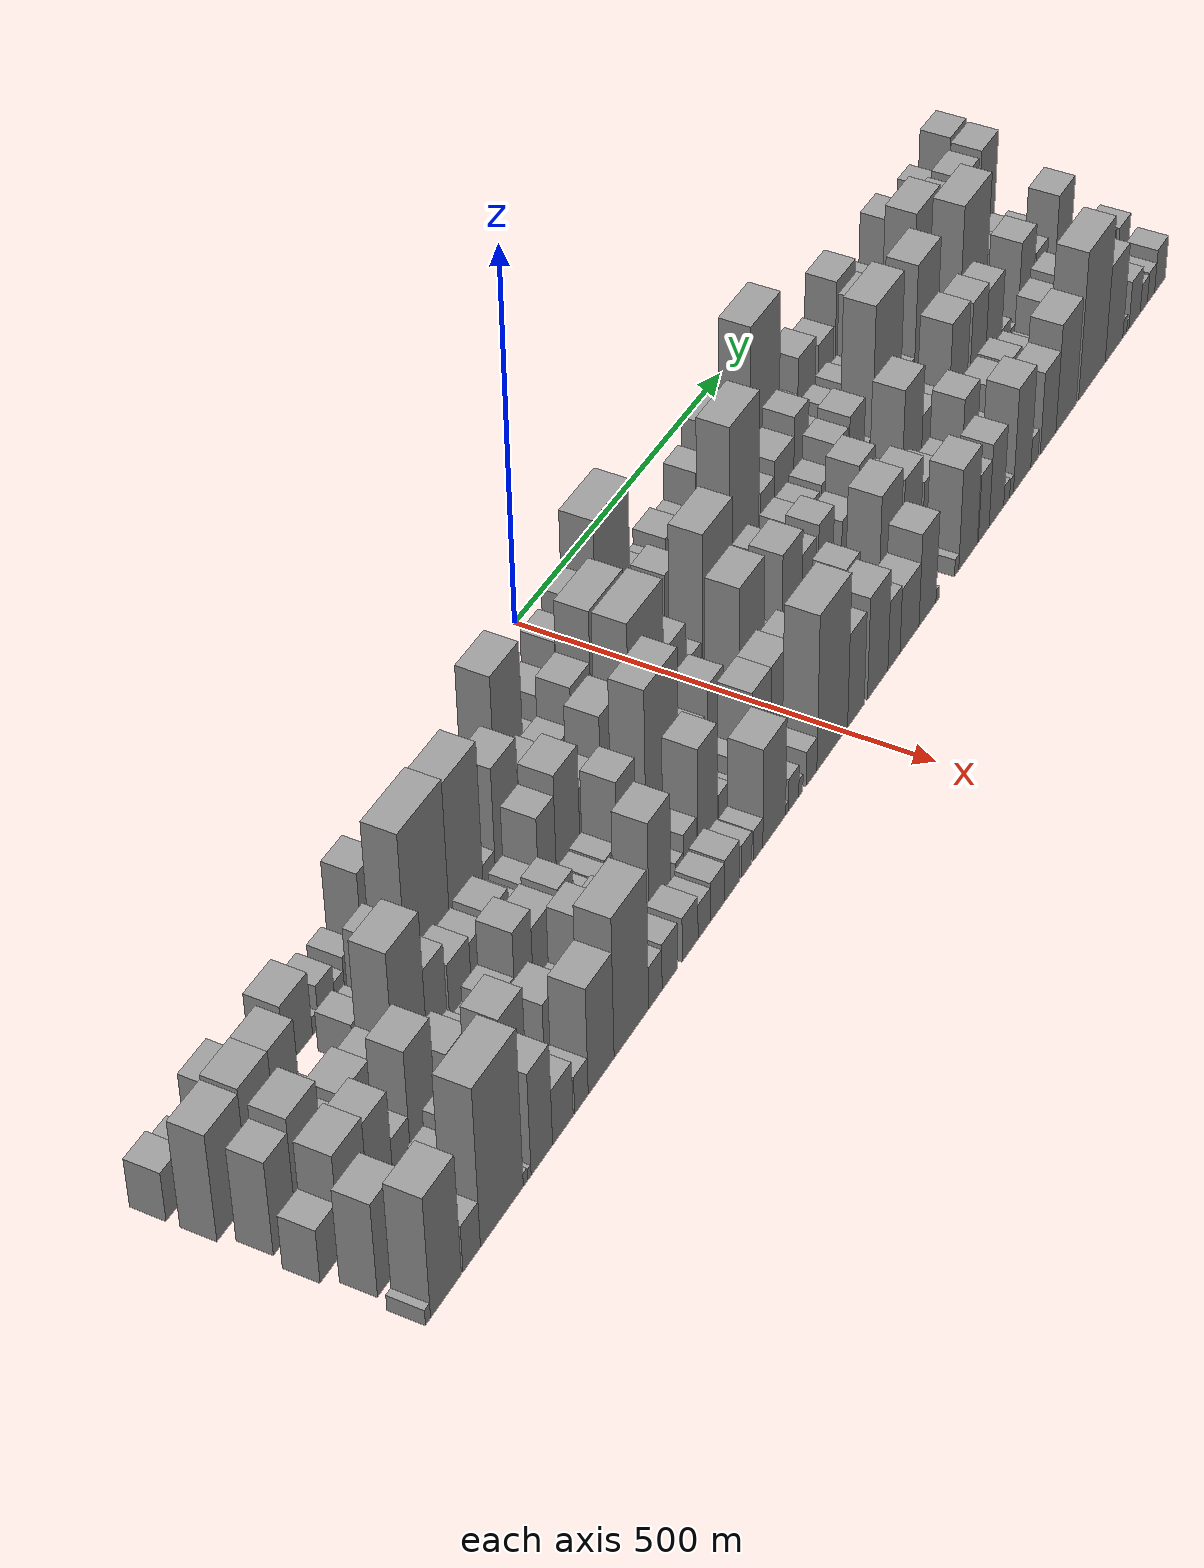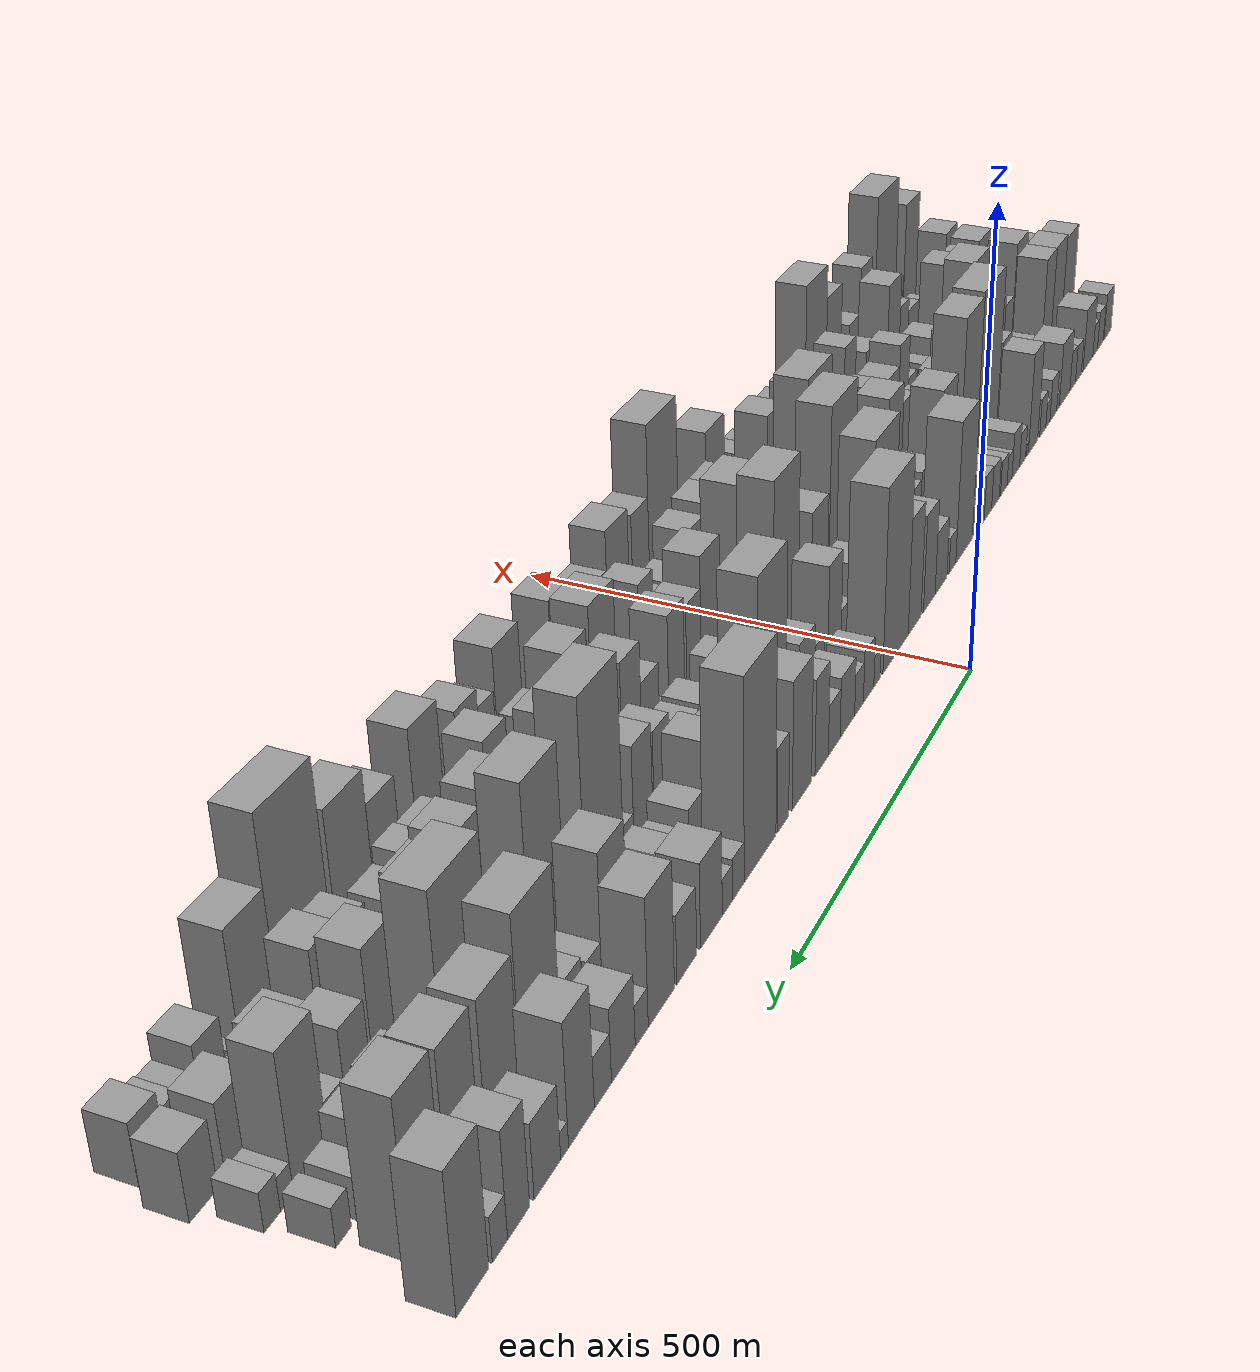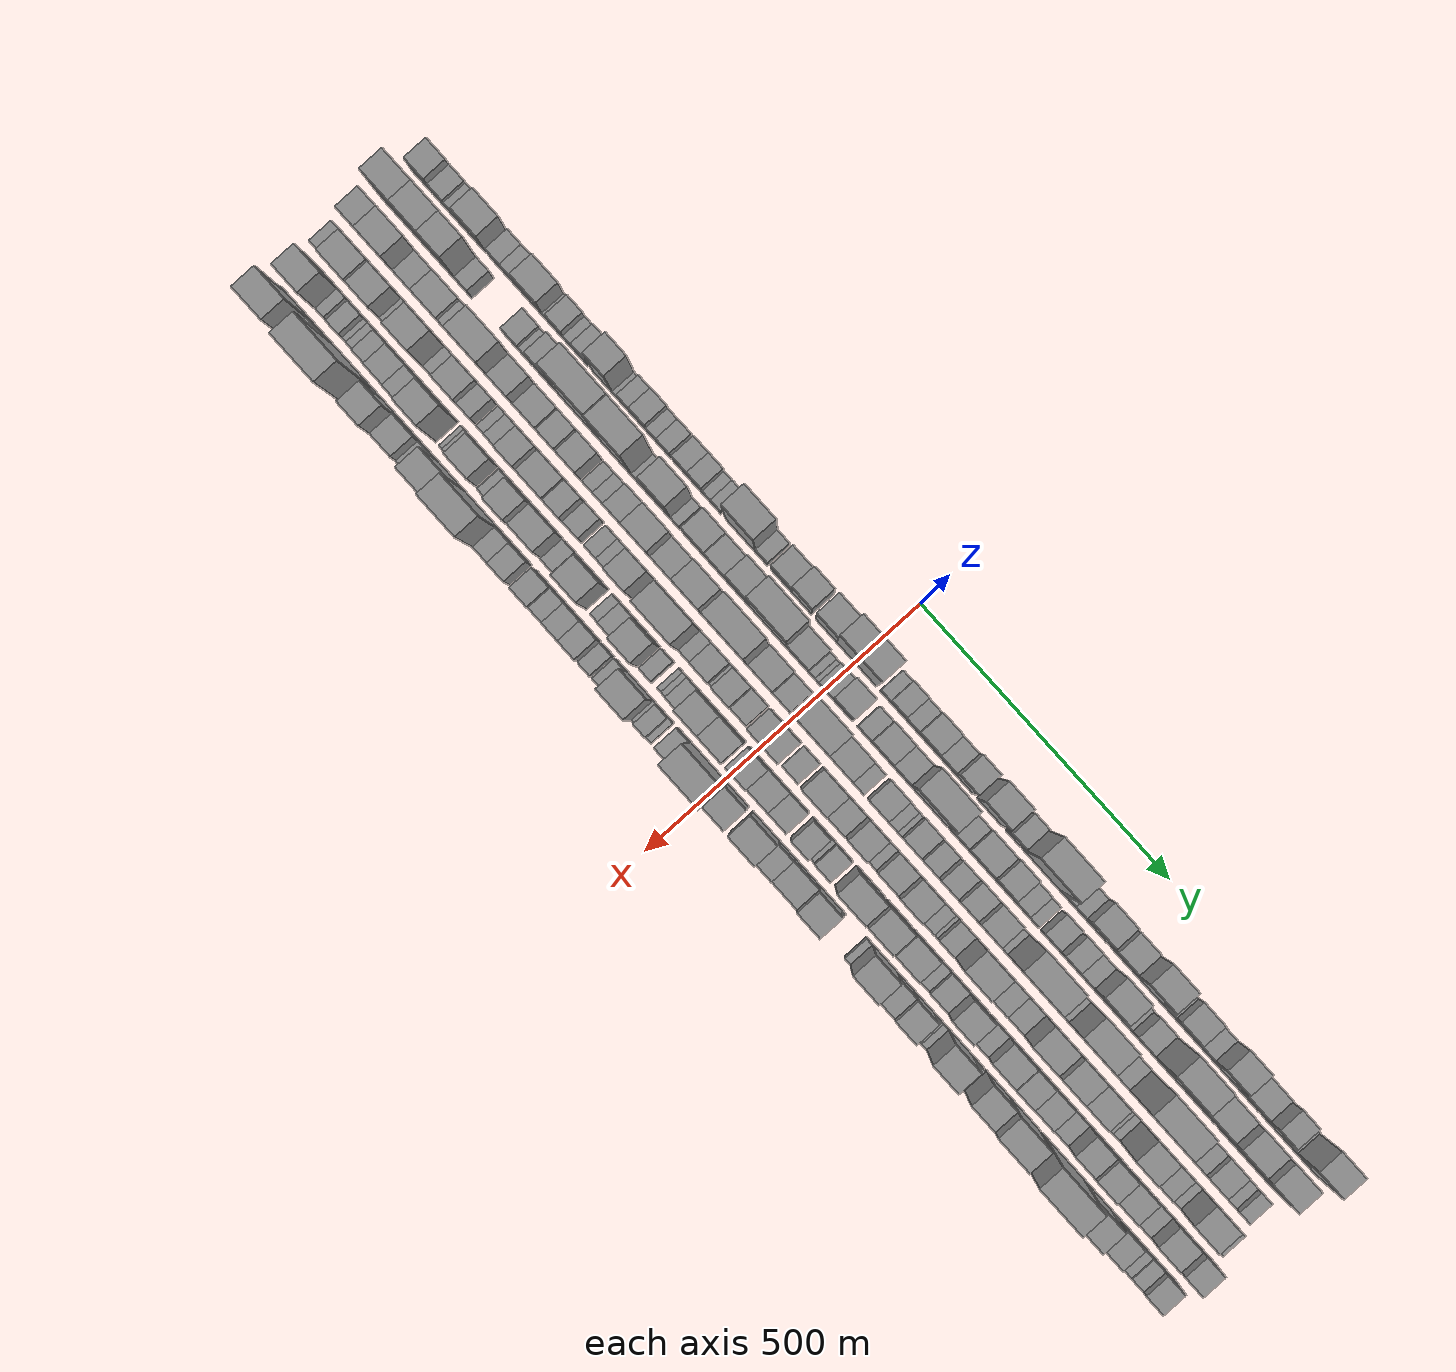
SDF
<sdf version="1.6">
 <world name="default">
  <scene>
   <sky><clouds><speed>12</speed></clouds></sky>
   <ambient>0.4 0.4 0.4 1</ambient>
   <background>0.7 0.7 0.7 1</background>
   <shadows>1</shadows>
  </scene>
  <gravity>0 0 -9.8066</gravity>
  <magnetic_field>6e-06 2.3e-05 -4.2e-05</magnetic_field>
  <physics default="0" name="default_physics" type="ode">
   <ode>
    <solver>
     <type>quick</type>
     <iters>10</iters>
     <sor>1.0</sor>
     <use_dynamic_moi_rescaling>0</use_dynamic_moi_rescaling>
    </solver>
    <constraints>
     <cfm>0</cfm>
     <erp>0.2</erp>
     <contact_max_correcting_vel>100</contact_max_correcting_vel>
     <contact_surface_layer>0.001</contact_surface_layer>
    </constraints>
   </ode>
   <max_step_size>0.004</max_step_size>
   <real_time_factor>1</real_time_factor>
   <real_time_update_rate>250</real_time_update_rate>
  </physics>
  <light name="sun" type="directional">
   <pose>0 0 10 0 0 0</pose>
   <diffuse>0.8 0.8 0.8 1</diffuse>
   <specular>0.2 0.2 0.2 1</specular>
   <attenuation>
    <range>1000</range>
    <constant>0.9</constant>
    <linear>0.01</linear>
    <quadratic>0.001</quadratic>
   </attenuation>
   <direction>-0.5 0.1 -0.9</direction>
  </light>
  <model name="building_1">
   <static>1</static>
   <pose>100.0000 -870.7207 0 0.000000 0.000000 0.000000</pose>
   <link name="link">
    <pose>0 0 33.00 0 0 0</pose>
    <collision name="collision"><geometry><box><size>40.0000 38.5586 66.0000</size></box></geometry></collision>
    <visual name="visual">
     <cast_shadows>0</cast_shadows>
     <geometry><box><size>40.0000 38.5586 66.0000</size></box></geometry>
     <material>
      <script>
       <uri>model://grey_wall/materials/scripts</uri>
       <uri>model://grey_wall/materials/textures</uri>
       <name>vrc/grey_wall</name>
      </script>
     </material>
    </visual>
   </link>
  </model>
  <model name="building_2">
   <static>1</static>
   <pose>100.0000 -832.6022 0 0.000000 0.000000 0.000000</pose>
   <link name="link">
    <pose>0 0 27.00 0 0 0</pose>
    <collision name="collision"><geometry><box><size>40.0000 29.6783 54.0000</size></box></geometry></collision>
    <visual name="visual">
     <cast_shadows>0</cast_shadows>
     <geometry><box><size>40.0000 29.6783 54.0000</size></box></geometry>
     <material>
      <script>
       <uri>model://grey_wall/materials/scripts</uri>
       <uri>model://grey_wall/materials/textures</uri>
       <name>vrc/grey_wall</name>
      </script>
     </material>
    </visual>
   </link>
  </model>
  <model name="building_3">
   <static>1</static>
   <pose>100.0000 -805.7250 0 0.000000 0.000000 0.000000</pose>
   <link name="link">
    <pose>0 0 22.50 0 0 0</pose>
    <collision name="collision"><geometry><box><size>40.0000 24.0761 45.0000</size></box></geometry></collision>
    <visual name="visual">
     <cast_shadows>0</cast_shadows>
     <geometry><box><size>40.0000 24.0761 45.0000</size></box></geometry>
     <material>
      <script>
       <uri>model://grey_wall/materials/scripts</uri>
       <uri>model://grey_wall/materials/textures</uri>
       <name>vrc/grey_wall</name>
      </script>
     </material>
    </visual>
   </link>
  </model>
  <model name="building_4">
   <static>1</static>
   <pose>100.0000 -768.3808 0 0.000000 0.000000 0.000000</pose>
   <link name="link">
    <pose>0 0 43.50 0 0 0</pose>
    <collision name="collision"><geometry><box><size>40.0000 50.6123 87.0000</size></box></geometry></collision>
    <visual name="visual">
     <cast_shadows>0</cast_shadows>
     <geometry><box><size>40.0000 50.6123 87.0000</size></box></geometry>
     <material>
      <script>
       <uri>model://grey_wall/materials/scripts</uri>
       <uri>model://grey_wall/materials/textures</uri>
       <name>vrc/grey_wall</name>
      </script>
     </material>
    </visual>
   </link>
  </model>
  <model name="building_5">
   <static>1</static>
   <pose>100.0000 -719.6450 0 0.000000 0.000000 0.000000</pose>
   <link name="link">
    <pose>0 0 25.50 0 0 0</pose>
    <collision name="collision"><geometry><box><size>40.0000 28.8593 51.0000</size></box></geometry></collision>
    <visual name="visual">
     <cast_shadows>0</cast_shadows>
     <geometry><box><size>40.0000 28.8593 51.0000</size></box></geometry>
     <material>
      <script>
       <uri>model://grey_wall/materials/scripts</uri>
       <uri>model://grey_wall/materials/textures</uri>
       <name>vrc/grey_wall</name>
      </script>
     </material>
    </visual>
   </link>
  </model>
  <model name="building_6">
   <static>1</static>
   <pose>100.0000 -691.6827 0 0.000000 0.000000 0.000000</pose>
   <link name="link">
    <pose>0 0 27.00 0 0 0</pose>
    <collision name="collision"><geometry><box><size>40.0000 27.0654 54.0000</size></box></geometry></collision>
    <visual name="visual">
     <cast_shadows>0</cast_shadows>
     <geometry><box><size>40.0000 27.0654 54.0000</size></box></geometry>
     <material>
      <script>
       <uri>model://grey_wall/materials/scripts</uri>
       <uri>model://grey_wall/materials/textures</uri>
       <name>vrc/grey_wall</name>
      </script>
     </material>
    </visual>
   </link>
  </model>
  <model name="building_7">
   <static>1</static>
   <pose>100.0000 -652.5568 0 0.000000 0.000000 0.000000</pose>
   <link name="link">
    <pose>0 0 43.50 0 0 0</pose>
    <collision name="collision"><geometry><box><size>40.0000 51.1863 87.0000</size></box></geometry></collision>
    <visual name="visual">
     <cast_shadows>0</cast_shadows>
     <geometry><box><size>40.0000 51.1863 87.0000</size></box></geometry>
     <material>
      <script>
       <uri>model://grey_wall/materials/scripts</uri>
       <uri>model://grey_wall/materials/textures</uri>
       <name>vrc/grey_wall</name>
      </script>
     </material>
    </visual>
   </link>
  </model>
  <model name="building_8">
   <static>1</static>
   <pose>100.0000 -621.0756 0 0.000000 0.000000 0.000000</pose>
   <link name="link">
    <pose>0 0 12.00 0 0 0</pose>
    <collision name="collision"><geometry><box><size>40.0000 11.7761 24.0000</size></box></geometry></collision>
    <visual name="visual">
     <cast_shadows>0</cast_shadows>
     <geometry><box><size>40.0000 11.7761 24.0000</size></box></geometry>
     <material>
      <script>
       <uri>model://grey_wall/materials/scripts</uri>
       <uri>model://grey_wall/materials/textures</uri>
       <name>vrc/grey_wall</name>
      </script>
     </material>
    </visual>
   </link>
  </model>
  <model name="building_9">
   <static>1</static>
   <pose>100.0000 -599.5443 0 0.000000 0.000000 0.000000</pose>
   <link name="link">
    <pose>0 0 28.50 0 0 0</pose>
    <collision name="collision"><geometry><box><size>40.0000 31.2865 57.0000</size></box></geometry></collision>
    <visual name="visual">
     <cast_shadows>0</cast_shadows>
     <geometry><box><size>40.0000 31.2865 57.0000</size></box></geometry>
     <material>
      <script>
       <uri>model://grey_wall/materials/scripts</uri>
       <uri>model://grey_wall/materials/textures</uri>
       <name>vrc/grey_wall</name>
      </script>
     </material>
    </visual>
   </link>
  </model>
  <model name="building_10">
   <static>1</static>
   <pose>100.0000 -574.7126 0 0.000000 0.000000 0.000000</pose>
   <link name="link">
    <pose>0 0 16.50 0 0 0</pose>
    <collision name="collision"><geometry><box><size>40.0000 18.3769 33.0000</size></box></geometry></collision>
    <visual name="visual">
     <cast_shadows>0</cast_shadows>
     <geometry><box><size>40.0000 18.3769 33.0000</size></box></geometry>
     <material>
      <script>
       <uri>model://grey_wall/materials/scripts</uri>
       <uri>model://grey_wall/materials/textures</uri>
       <name>vrc/grey_wall</name>
      </script>
     </material>
    </visual>
   </link>
  </model>
  <model name="building_11">
   <static>1</static>
   <pose>100.0000 -551.5898 0 0.000000 0.000000 0.000000</pose>
   <link name="link">
    <pose>0 0 25.50 0 0 0</pose>
    <collision name="collision"><geometry><box><size>40.0000 27.8686 51.0000</size></box></geometry></collision>
    <visual name="visual">
     <cast_shadows>0</cast_shadows>
     <geometry><box><size>40.0000 27.8686 51.0000</size></box></geometry>
     <material>
      <script>
       <uri>model://grey_wall/materials/scripts</uri>
       <uri>model://grey_wall/materials/textures</uri>
       <name>vrc/grey_wall</name>
      </script>
     </material>
    </visual>
   </link>
  </model>
  <model name="building_12">
   <static>1</static>
   <pose>100.0000 -508.1606 0 0.000000 0.000000 0.000000</pose>
   <link name="link">
    <pose>0 0 66.00 0 0 0</pose>
    <collision name="collision"><geometry><box><size>40.0000 40.9898 132.0000</size></box></geometry></collision>
    <visual name="visual">
     <cast_shadows>0</cast_shadows>
     <geometry><box><size>40.0000 40.9898 132.0000</size></box></geometry>
     <material>
      <script>
       <uri>model://grey_wall/materials/scripts</uri>
       <uri>model://grey_wall/materials/textures</uri>
       <name>vrc/grey_wall</name>
      </script>
     </material>
    </visual>
   </link>
  </model>
  <model name="building_13">
   <static>1</static>
   <pose>100.0000 -483.3093 0 0.000000 0.000000 0.000000</pose>
   <link name="link">
    <pose>0 0 9.00 0 0 0</pose>
    <collision name="collision"><geometry><box><size>40.0000 8.7128 18.0000</size></box></geometry></collision>
    <visual name="visual">
     <cast_shadows>0</cast_shadows>
     <geometry><box><size>40.0000 8.7128 18.0000</size></box></geometry>
     <material>
      <script>
       <uri>model://grey_wall/materials/scripts</uri>
       <uri>model://grey_wall/materials/textures</uri>
       <name>vrc/grey_wall</name>
      </script>
     </material>
    </visual>
   </link>
  </model>
  <model name="building_14">
   <static>1</static>
   <pose>100.0000 -462.9301 0 0.000000 0.000000 0.000000</pose>
   <link name="link">
    <pose>0 0 22.50 0 0 0</pose>
    <collision name="collision"><geometry><box><size>40.0000 26.0456 45.0000</size></box></geometry></collision>
    <visual name="visual">
     <cast_shadows>0</cast_shadows>
     <geometry><box><size>40.0000 26.0456 45.0000</size></box></geometry>
     <material>
      <script>
       <uri>model://grey_wall/materials/scripts</uri>
       <uri>model://grey_wall/materials/textures</uri>
       <name>vrc/grey_wall</name>
      </script>
     </material>
    </visual>
   </link>
  </model>
  <model name="building_15">
   <static>1</static>
   <pose>100.0000 -434.0075 0 0.000000 0.000000 0.000000</pose>
   <link name="link">
    <pose>0 0 30.00 0 0 0</pose>
    <collision name="collision"><geometry><box><size>40.0000 31.7995 60.0000</size></box></geometry></collision>
    <visual name="visual">
     <cast_shadows>0</cast_shadows>
     <geometry><box><size>40.0000 31.7995 60.0000</size></box></geometry>
     <material>
      <script>
       <uri>model://grey_wall/materials/scripts</uri>
       <uri>model://grey_wall/materials/textures</uri>
       <name>vrc/grey_wall</name>
      </script>
     </material>
    </visual>
   </link>
  </model>
  <model name="building_16">
   <static>1</static>
   <pose>100.0000 -407.9392 0 0.000000 0.000000 0.000000</pose>
   <link name="link">
    <pose>0 0 19.50 0 0 0</pose>
    <collision name="collision"><geometry><box><size>40.0000 20.3372 39.0000</size></box></geometry></collision>
    <visual name="visual">
     <cast_shadows>0</cast_shadows>
     <geometry><box><size>40.0000 20.3372 39.0000</size></box></geometry>
     <material>
      <script>
       <uri>model://grey_wall/materials/scripts</uri>
       <uri>model://grey_wall/materials/textures</uri>
       <name>vrc/grey_wall</name>
      </script>
     </material>
    </visual>
   </link>
  </model>
  <model name="building_17">
   <static>1</static>
   <pose>100.0000 -384.3671 0 0.000000 0.000000 0.000000</pose>
   <link name="link">
    <pose>0 0 22.50 0 0 0</pose>
    <collision name="collision"><geometry><box><size>40.0000 26.8070 45.0000</size></box></geometry></collision>
    <visual name="visual">
     <cast_shadows>0</cast_shadows>
     <geometry><box><size>40.0000 26.8070 45.0000</size></box></geometry>
     <material>
      <script>
       <uri>model://grey_wall/materials/scripts</uri>
       <uri>model://grey_wall/materials/textures</uri>
       <name>vrc/grey_wall</name>
      </script>
     </material>
    </visual>
   </link>
  </model>
  <model name="building_18">
   <static>1</static>
   <pose>100.0000 -350.8128 0 0.000000 0.000000 0.000000</pose>
   <link name="link">
    <pose>0 0 27.00 0 0 0</pose>
    <collision name="collision"><geometry><box><size>40.0000 30.3017 54.0000</size></box></geometry></collision>
    <visual name="visual">
     <cast_shadows>0</cast_shadows>
     <geometry><box><size>40.0000 30.3017 54.0000</size></box></geometry>
     <material>
      <script>
       <uri>model://grey_wall/materials/scripts</uri>
       <uri>model://grey_wall/materials/textures</uri>
       <name>vrc/grey_wall</name>
      </script>
     </material>
    </visual>
   </link>
  </model>
  <model name="building_19">
   <static>1</static>
   <pose>100.0000 -321.2850 0 0.000000 0.000000 0.000000</pose>
   <link name="link">
    <pose>0 0 28.50 0 0 0</pose>
    <collision name="collision"><geometry><box><size>40.0000 28.7539 57.0000</size></box></geometry></collision>
    <visual name="visual">
     <cast_shadows>0</cast_shadows>
     <geometry><box><size>40.0000 28.7539 57.0000</size></box></geometry>
     <material>
      <script>
       <uri>model://grey_wall/materials/scripts</uri>
       <uri>model://grey_wall/materials/textures</uri>
       <name>vrc/grey_wall</name>
      </script>
     </material>
    </visual>
   </link>
  </model>
  <model name="building_20">
   <static>1</static>
   <pose>100.0000 -298.5573 0 0.000000 0.000000 0.000000</pose>
   <link name="link">
    <pose>0 0 15.00 0 0 0</pose>
    <collision name="collision"><geometry><box><size>40.0000 16.7016 30.0000</size></box></geometry></collision>
    <visual name="visual">
     <cast_shadows>0</cast_shadows>
     <geometry><box><size>40.0000 16.7016 30.0000</size></box></geometry>
     <material>
      <script>
       <uri>model://grey_wall/materials/scripts</uri>
       <uri>model://grey_wall/materials/textures</uri>
       <name>vrc/grey_wall</name>
      </script>
     </material>
    </visual>
   </link>
  </model>
  <model name="building_21">
   <static>1</static>
   <pose>100.0000 -280.0952 0 0.000000 0.000000 0.000000</pose>
   <link name="link">
    <pose>0 0 18.00 0 0 0</pose>
    <collision name="collision"><geometry><box><size>40.0000 20.2226 36.0000</size></box></geometry></collision>
    <visual name="visual">
     <cast_shadows>0</cast_shadows>
     <geometry><box><size>40.0000 20.2226 36.0000</size></box></geometry>
     <material>
      <script>
       <uri>model://grey_wall/materials/scripts</uri>
       <uri>model://grey_wall/materials/textures</uri>
       <name>vrc/grey_wall</name>
      </script>
     </material>
    </visual>
   </link>
  </model>
  <model name="building_22">
   <static>1</static>
   <pose>100.0000 -230.6435 0 0.000000 0.000000 0.000000</pose>
   <link name="link">
    <pose>0 0 87.00 0 0 0</pose>
    <collision name="collision"><geometry><box><size>40.0000 60.6807 174.0000</size></box></geometry></collision>
    <visual name="visual">
     <cast_shadows>0</cast_shadows>
     <geometry><box><size>40.0000 60.6807 174.0000</size></box></geometry>
     <material>
      <script>
       <uri>model://grey_wall/materials/scripts</uri>
       <uri>model://grey_wall/materials/textures</uri>
       <name>vrc/grey_wall</name>
      </script>
     </material>
    </visual>
   </link>
  </model>
  <model name="building_23">
   <static>1</static>
   <pose>100.0000 -188.2242 0 0.000000 0.000000 0.000000</pose>
   <link name="link">
    <pose>0 0 22.50 0 0 0</pose>
    <collision name="collision"><geometry><box><size>40.0000 24.1580 45.0000</size></box></geometry></collision>
    <visual name="visual">
     <cast_shadows>0</cast_shadows>
     <geometry><box><size>40.0000 24.1580 45.0000</size></box></geometry>
     <material>
      <script>
       <uri>model://grey_wall/materials/scripts</uri>
       <uri>model://grey_wall/materials/textures</uri>
       <name>vrc/grey_wall</name>
      </script>
     </material>
    </visual>
   </link>
  </model>
  <model name="building_24">
   <static>1</static>
   <pose>100.0000 -148.4430 0 0.000000 0.000000 0.000000</pose>
   <link name="link">
    <pose>0 0 37.50 0 0 0</pose>
    <collision name="collision"><geometry><box><size>40.0000 41.4044 75.0000</size></box></geometry></collision>
    <visual name="visual">
     <cast_shadows>0</cast_shadows>
     <geometry><box><size>40.0000 41.4044 75.0000</size></box></geometry>
     <material>
      <script>
       <uri>model://grey_wall/materials/scripts</uri>
       <uri>model://grey_wall/materials/textures</uri>
       <name>vrc/grey_wall</name>
      </script>
     </material>
    </visual>
   </link>
  </model>
  <model name="building_25">
   <static>1</static>
   <pose>100.0000 -107.9037 0 0.000000 0.000000 0.000000</pose>
   <link name="link">
    <pose>0 0 58.50 0 0 0</pose>
    <collision name="collision"><geometry><box><size>40.0000 39.6741 117.0000</size></box></geometry></collision>
    <visual name="visual">
     <cast_shadows>0</cast_shadows>
     <geometry><box><size>40.0000 39.6741 117.0000</size></box></geometry>
     <material>
      <script>
       <uri>model://grey_wall/materials/scripts</uri>
       <uri>model://grey_wall/materials/textures</uri>
       <name>vrc/grey_wall</name>
      </script>
     </material>
    </visual>
   </link>
  </model>
  <model name="building_26">
   <static>1</static>
   <pose>100.0000 -58.9600 0 0.000000 0.000000 0.000000</pose>
   <link name="link">
    <pose>0 0 69.00 0 0 0</pose>
    <collision name="collision"><geometry><box><size>40.0000 42.2133 138.0000</size></box></geometry></collision>
    <visual name="visual">
     <cast_shadows>0</cast_shadows>
     <geometry><box><size>40.0000 42.2133 138.0000</size></box></geometry>
     <material>
      <script>
       <uri>model://grey_wall/materials/scripts</uri>
       <uri>model://grey_wall/materials/textures</uri>
       <name>vrc/grey_wall</name>
      </script>
     </material>
    </visual>
   </link>
  </model>
  <model name="building_27">
   <static>1</static>
   <pose>100.0000 1.7411 0 0.000000 0.000000 0.000000</pose>
   <link name="link">
    <pose>0 0 106.50 0 0 0</pose>
    <collision name="collision"><geometry><box><size>40.0000 79.1890 213.0000</size></box></geometry></collision>
    <visual name="visual">
     <cast_shadows>0</cast_shadows>
     <geometry><box><size>40.0000 79.1890 213.0000</size></box></geometry>
     <material>
      <script>
       <uri>model://grey_wall/materials/scripts</uri>
       <uri>model://grey_wall/materials/textures</uri>
       <name>vrc/grey_wall</name>
      </script>
     </material>
    </visual>
   </link>
  </model>
  <model name="building_28">
   <static>1</static>
   <pose>100.0000 59.1877 0 0.000000 0.000000 0.000000</pose>
   <link name="link">
    <pose>0 0 18.00 0 0 0</pose>
    <collision name="collision"><geometry><box><size>40.0000 19.7042 36.0000</size></box></geometry></collision>
    <visual name="visual">
     <cast_shadows>0</cast_shadows>
     <geometry><box><size>40.0000 19.7042 36.0000</size></box></geometry>
     <material>
      <script>
       <uri>model://grey_wall/materials/scripts</uri>
       <uri>model://grey_wall/materials/textures</uri>
       <name>vrc/grey_wall</name>
      </script>
     </material>
    </visual>
   </link>
  </model>
  <model name="building_29">
   <static>1</static>
   <pose>100.0000 84.3180 0 0.000000 0.000000 0.000000</pose>
   <link name="link">
    <pose>0 0 30.00 0 0 0</pose>
    <collision name="collision"><geometry><box><size>40.0000 30.5564 60.0000</size></box></geometry></collision>
    <visual name="visual">
     <cast_shadows>0</cast_shadows>
     <geometry><box><size>40.0000 30.5564 60.0000</size></box></geometry>
     <material>
      <script>
       <uri>model://grey_wall/materials/scripts</uri>
       <uri>model://grey_wall/materials/textures</uri>
       <name>vrc/grey_wall</name>
      </script>
     </material>
    </visual>
   </link>
  </model>
  <model name="building_30">
   <static>1</static>
   <pose>100.0000 112.3530 0 0.000000 0.000000 0.000000</pose>
   <link name="link">
    <pose>0 0 24.00 0 0 0</pose>
    <collision name="collision"><geometry><box><size>40.0000 25.5136 48.0000</size></box></geometry></collision>
    <visual name="visual">
     <cast_shadows>0</cast_shadows>
     <geometry><box><size>40.0000 25.5136 48.0000</size></box></geometry>
     <material>
      <script>
       <uri>model://grey_wall/materials/scripts</uri>
       <uri>model://grey_wall/materials/textures</uri>
       <name>vrc/grey_wall</name>
      </script>
     </material>
    </visual>
   </link>
  </model>
  <model name="building_31">
   <static>1</static>
   <pose>100.0000 145.6820 0 0.000000 0.000000 0.000000</pose>
   <link name="link">
    <pose>0 0 34.50 0 0 0</pose>
    <collision name="collision"><geometry><box><size>40.0000 41.1445 69.0000</size></box></geometry></collision>
    <visual name="visual">
     <cast_shadows>0</cast_shadows>
     <geometry><box><size>40.0000 41.1445 69.0000</size></box></geometry>
     <material>
      <script>
       <uri>model://grey_wall/materials/scripts</uri>
       <uri>model://grey_wall/materials/textures</uri>
       <name>vrc/grey_wall</name>
      </script>
     </material>
    </visual>
   </link>
  </model>
  <model name="building_32">
   <static>1</static>
   <pose>100.0000 182.3514 0 0.000000 0.000000 0.000000</pose>
   <link name="link">
    <pose>0 0 28.50 0 0 0</pose>
    <collision name="collision"><geometry><box><size>40.0000 32.1942 57.0000</size></box></geometry></collision>
    <visual name="visual">
     <cast_shadows>0</cast_shadows>
     <geometry><box><size>40.0000 32.1942 57.0000</size></box></geometry>
     <material>
      <script>
       <uri>model://grey_wall/materials/scripts</uri>
       <uri>model://grey_wall/materials/textures</uri>
       <name>vrc/grey_wall</name>
      </script>
     </material>
    </visual>
   </link>
  </model>
  <model name="building_33">
   <static>1</static>
   <pose>100.0000 216.3945 0 0.000000 0.000000 0.000000</pose>
   <link name="link">
    <pose>0 0 54.00 0 0 0</pose>
    <collision name="collision"><geometry><box><size>40.0000 35.8920 108.0000</size></box></geometry></collision>
    <visual name="visual">
     <cast_shadows>0</cast_shadows>
     <geometry><box><size>40.0000 35.8920 108.0000</size></box></geometry>
     <material>
      <script>
       <uri>model://grey_wall/materials/scripts</uri>
       <uri>model://grey_wall/materials/textures</uri>
       <name>vrc/grey_wall</name>
      </script>
     </material>
    </visual>
   </link>
  </model>
  <model name="building_34">
   <static>1</static>
   <pose>100.0000 268.0884 0 0.000000 0.000000 0.000000</pose>
   <link name="link">
    <pose>0 0 70.50 0 0 0</pose>
    <collision name="collision"><geometry><box><size>40.0000 49.4960 141.0000</size></box></geometry></collision>
    <visual name="visual">
     <cast_shadows>0</cast_shadows>
     <geometry><box><size>40.0000 49.4960 141.0000</size></box></geometry>
     <material>
      <script>
       <uri>model://grey_wall/materials/scripts</uri>
       <uri>model://grey_wall/materials/textures</uri>
       <name>vrc/grey_wall</name>
      </script>
     </material>
    </visual>
   </link>
  </model>
  <model name="building_35">
   <static>1</static>
   <pose>100.0000 316.1049 0 0.000000 0.000000 0.000000</pose>
   <link name="link">
    <pose>0 0 46.50 0 0 0</pose>
    <collision name="collision"><geometry><box><size>40.0000 28.5371 93.0000</size></box></geometry></collision>
    <visual name="visual">
     <cast_shadows>0</cast_shadows>
     <geometry><box><size>40.0000 28.5371 93.0000</size></box></geometry>
     <material>
      <script>
       <uri>model://grey_wall/materials/scripts</uri>
       <uri>model://grey_wall/materials/textures</uri>
       <name>vrc/grey_wall</name>
      </script>
     </material>
    </visual>
   </link>
  </model>
  <model name="building_36">
   <static>1</static>
   <pose>100.0000 371.0116 0 0.000000 0.000000 0.000000</pose>
   <link name="link">
    <pose>0 0 108.00 0 0 0</pose>
    <collision name="collision"><geometry><box><size>40.0000 75.2764 216.0000</size></box></geometry></collision>
    <visual name="visual">
     <cast_shadows>0</cast_shadows>
     <geometry><box><size>40.0000 75.2764 216.0000</size></box></geometry>
     <material>
      <script>
       <uri>model://grey_wall/materials/scripts</uri>
       <uri>model://grey_wall/materials/textures</uri>
       <name>vrc/grey_wall</name>
      </script>
     </material>
    </visual>
   </link>
  </model>
  <model name="building_37">
   <static>1</static>
   <pose>100.0000 422.1085 0 0.000000 0.000000 0.000000</pose>
   <link name="link">
    <pose>0 0 22.50 0 0 0</pose>
    <collision name="collision"><geometry><box><size>40.0000 26.9173 45.0000</size></box></geometry></collision>
    <visual name="visual">
     <cast_shadows>0</cast_shadows>
     <geometry><box><size>40.0000 26.9173 45.0000</size></box></geometry>
     <material>
      <script>
       <uri>model://grey_wall/materials/scripts</uri>
       <uri>model://grey_wall/materials/textures</uri>
       <name>vrc/grey_wall</name>
      </script>
     </material>
    </visual>
   </link>
  </model>
  <model name="building_38">
   <static>1</static>
   <pose>100.0000 446.6524 0 0.000000 0.000000 0.000000</pose>
   <link name="link">
    <pose>0 0 19.50 0 0 0</pose>
    <collision name="collision"><geometry><box><size>40.0000 22.1706 39.0000</size></box></geometry></collision>
    <visual name="visual">
     <cast_shadows>0</cast_shadows>
     <geometry><box><size>40.0000 22.1706 39.0000</size></box></geometry>
     <material>
      <script>
       <uri>model://grey_wall/materials/scripts</uri>
       <uri>model://grey_wall/materials/textures</uri>
       <name>vrc/grey_wall</name>
      </script>
     </material>
    </visual>
   </link>
  </model>
  <model name="building_39">
   <static>1</static>
   <pose>100.0000 481.2017 0 0.000000 0.000000 0.000000</pose>
   <link name="link">
    <pose>0 0 45.00 0 0 0</pose>
    <collision name="collision"><geometry><box><size>40.0000 46.9281 90.0000</size></box></geometry></collision>
    <visual name="visual">
     <cast_shadows>0</cast_shadows>
     <geometry><box><size>40.0000 46.9281 90.0000</size></box></geometry>
     <material>
      <script>
       <uri>model://grey_wall/materials/scripts</uri>
       <uri>model://grey_wall/materials/textures</uri>
       <name>vrc/grey_wall</name>
      </script>
     </material>
    </visual>
   </link>
  </model>
  <model name="building_40">
   <static>1</static>
   <pose>100.0000 533.0369 0 0.000000 0.000000 0.000000</pose>
   <link name="link">
    <pose>0 0 36.00 0 0 0</pose>
    <collision name="collision"><geometry><box><size>40.0000 40.7424 72.0000</size></box></geometry></collision>
    <visual name="visual">
     <cast_shadows>0</cast_shadows>
     <geometry><box><size>40.0000 40.7424 72.0000</size></box></geometry>
     <material>
      <script>
       <uri>model://grey_wall/materials/scripts</uri>
       <uri>model://grey_wall/materials/textures</uri>
       <name>vrc/grey_wall</name>
      </script>
     </material>
    </visual>
   </link>
  </model>
  <model name="building_41">
   <static>1</static>
   <pose>100.0000 584.1585 0 0.000000 0.000000 0.000000</pose>
   <link name="link">
    <pose>0 0 66.00 0 0 0</pose>
    <collision name="collision"><geometry><box><size>40.0000 51.5008 132.0000</size></box></geometry></collision>
    <visual name="visual">
     <cast_shadows>0</cast_shadows>
     <geometry><box><size>40.0000 51.5008 132.0000</size></box></geometry>
     <material>
      <script>
       <uri>model://grey_wall/materials/scripts</uri>
       <uri>model://grey_wall/materials/textures</uri>
       <name>vrc/grey_wall</name>
      </script>
     </material>
    </visual>
   </link>
  </model>
  <model name="building_42">
   <static>1</static>
   <pose>100.0000 622.2967 0 0.000000 0.000000 0.000000</pose>
   <link name="link">
    <pose>0 0 21.00 0 0 0</pose>
    <collision name="collision"><geometry><box><size>40.0000 24.7755 42.0000</size></box></geometry></collision>
    <visual name="visual">
     <cast_shadows>0</cast_shadows>
     <geometry><box><size>40.0000 24.7755 42.0000</size></box></geometry>
     <material>
      <script>
       <uri>model://grey_wall/materials/scripts</uri>
       <uri>model://grey_wall/materials/textures</uri>
       <name>vrc/grey_wall</name>
      </script>
     </material>
    </visual>
   </link>
  </model>
  <model name="building_43">
   <static>1</static>
   <pose>100.0000 656.5009 0 0.000000 0.000000 0.000000</pose>
   <link name="link">
    <pose>0 0 37.50 0 0 0</pose>
    <collision name="collision"><geometry><box><size>40.0000 43.6329 75.0000</size></box></geometry></collision>
    <visual name="visual">
     <cast_shadows>0</cast_shadows>
     <geometry><box><size>40.0000 43.6329 75.0000</size></box></geometry>
     <material>
      <script>
       <uri>model://grey_wall/materials/scripts</uri>
       <uri>model://grey_wall/materials/textures</uri>
       <name>vrc/grey_wall</name>
      </script>
     </material>
    </visual>
   </link>
  </model>
  <model name="building_44">
   <static>1</static>
   <pose>100.0000 693.5392 0 0.000000 0.000000 0.000000</pose>
   <link name="link">
    <pose>0 0 25.50 0 0 0</pose>
    <collision name="collision"><geometry><box><size>40.0000 30.4438 51.0000</size></box></geometry></collision>
    <visual name="visual">
     <cast_shadows>0</cast_shadows>
     <geometry><box><size>40.0000 30.4438 51.0000</size></box></geometry>
     <material>
      <script>
       <uri>model://grey_wall/materials/scripts</uri>
       <uri>model://grey_wall/materials/textures</uri>
       <name>vrc/grey_wall</name>
      </script>
     </material>
    </visual>
   </link>
  </model>
  <model name="building_45">
   <static>1</static>
   <pose>100.0000 730.9482 0 0.000000 0.000000 0.000000</pose>
   <link name="link">
    <pose>0 0 61.50 0 0 0</pose>
    <collision name="collision"><geometry><box><size>40.0000 44.3742 123.0000</size></box></geometry></collision>
    <visual name="visual">
     <cast_shadows>0</cast_shadows>
     <geometry><box><size>40.0000 44.3742 123.0000</size></box></geometry>
     <material>
      <script>
       <uri>model://grey_wall/materials/scripts</uri>
       <uri>model://grey_wall/materials/textures</uri>
       <name>vrc/grey_wall</name>
      </script>
     </material>
    </visual>
   </link>
  </model>
  <model name="building_46">
   <static>1</static>
   <pose>100.0000 759.7542 0 0.000000 0.000000 0.000000</pose>
   <link name="link">
    <pose>0 0 13.50 0 0 0</pose>
    <collision name="collision"><geometry><box><size>40.0000 13.2378 27.0000</size></box></geometry></collision>
    <visual name="visual">
     <cast_shadows>0</cast_shadows>
     <geometry><box><size>40.0000 13.2378 27.0000</size></box></geometry>
     <material>
      <script>
       <uri>model://grey_wall/materials/scripts</uri>
       <uri>model://grey_wall/materials/textures</uri>
       <name>vrc/grey_wall</name>
      </script>
     </material>
    </visual>
   </link>
  </model>
  <model name="building_47">
   <static>1</static>
   <pose>100.0000 787.9437 0 0.000000 0.000000 0.000000</pose>
   <link name="link">
    <pose>0 0 37.50 0 0 0</pose>
    <collision name="collision"><geometry><box><size>40.0000 43.1413 75.0000</size></box></geometry></collision>
    <visual name="visual">
     <cast_shadows>0</cast_shadows>
     <geometry><box><size>40.0000 43.1413 75.0000</size></box></geometry>
     <material>
      <script>
       <uri>model://grey_wall/materials/scripts</uri>
       <uri>model://grey_wall/materials/textures</uri>
       <name>vrc/grey_wall</name>
      </script>
     </material>
    </visual>
   </link>
  </model>
  <model name="building_48">
   <static>1</static>
   <pose>100.0000 833.5726 0 0.000000 0.000000 0.000000</pose>
   <link name="link">
    <pose>0 0 52.50 0 0 0</pose>
    <collision name="collision"><geometry><box><size>40.0000 34.1164 105.0000</size></box></geometry></collision>
    <visual name="visual">
     <cast_shadows>0</cast_shadows>
     <geometry><box><size>40.0000 34.1164 105.0000</size></box></geometry>
     <material>
      <script>
       <uri>model://grey_wall/materials/scripts</uri>
       <uri>model://grey_wall/materials/textures</uri>
       <name>vrc/grey_wall</name>
      </script>
     </material>
    </visual>
   </link>
  </model>
  <model name="building_49">
   <static>1</static>
   <pose>100.0000 862.2332 0 0.000000 0.000000 0.000000</pose>
   <link name="link">
    <pose>0 0 22.50 0 0 0</pose>
    <collision name="collision"><geometry><box><size>40.0000 23.2050 45.0000</size></box></geometry></collision>
    <visual name="visual">
     <cast_shadows>0</cast_shadows>
     <geometry><box><size>40.0000 23.2050 45.0000</size></box></geometry>
     <material>
      <script>
       <uri>model://grey_wall/materials/scripts</uri>
       <uri>model://grey_wall/materials/textures</uri>
       <name>vrc/grey_wall</name>
      </script>
     </material>
    </visual>
   </link>
  </model>
  <model name="building_50">
   <static>1</static>
   <pose>100.0000 902.5514 0 0.000000 0.000000 0.000000</pose>
   <link name="link">
    <pose>0 0 69.00 0 0 0</pose>
    <collision name="collision"><geometry><box><size>40.0000 47.4314 138.0000</size></box></geometry></collision>
    <visual name="visual">
     <cast_shadows>0</cast_shadows>
     <geometry><box><size>40.0000 47.4314 138.0000</size></box></geometry>
     <material>
      <script>
       <uri>model://grey_wall/materials/scripts</uri>
       <uri>model://grey_wall/materials/textures</uri>
       <name>vrc/grey_wall</name>
      </script>
     </material>
    </visual>
   </link>
  </model>
  <model name="building_51">
   <static>1</static>
   <pose>155.0000 -861.5962 0 0.000000 0.000000 0.000000</pose>
   <link name="link">
    <pose>0 0 72.00 0 0 0</pose>
    <collision name="collision"><geometry><box><size>40.0000 56.8075 144.0000</size></box></geometry></collision>
    <visual name="visual">
     <cast_shadows>0</cast_shadows>
     <geometry><box><size>40.0000 56.8075 144.0000</size></box></geometry>
     <material>
      <script>
       <uri>model://grey_wall/materials/scripts</uri>
       <uri>model://grey_wall/materials/textures</uri>
       <name>vrc/grey_wall</name>
      </script>
     </material>
    </visual>
   </link>
  </model>
  <model name="building_52">
   <static>1</static>
   <pose>155.0000 -806.9790 0 0.000000 0.000000 0.000000</pose>
   <link name="link">
    <pose>0 0 75.00 0 0 0</pose>
    <collision name="collision"><geometry><box><size>40.0000 52.4269 150.0000</size></box></geometry></collision>
    <visual name="visual">
     <cast_shadows>0</cast_shadows>
     <geometry><box><size>40.0000 52.4269 150.0000</size></box></geometry>
     <material>
      <script>
       <uri>model://grey_wall/materials/scripts</uri>
       <uri>model://grey_wall/materials/textures</uri>
       <name>vrc/grey_wall</name>
      </script>
     </material>
    </visual>
   </link>
  </model>
  <model name="building_53">
   <static>1</static>
   <pose>155.0000 -758.2334 0 0.000000 0.000000 0.000000</pose>
   <link name="link">
    <pose>0 0 75.00 0 0 0</pose>
    <collision name="collision"><geometry><box><size>40.0000 45.0644 150.0000</size></box></geometry></collision>
    <visual name="visual">
     <cast_shadows>0</cast_shadows>
     <geometry><box><size>40.0000 45.0644 150.0000</size></box></geometry>
     <material>
      <script>
       <uri>model://grey_wall/materials/scripts</uri>
       <uri>model://grey_wall/materials/textures</uri>
       <name>vrc/grey_wall</name>
      </script>
     </material>
    </visual>
   </link>
  </model>
  <model name="building_54">
   <static>1</static>
   <pose>155.0000 -722.8340 0 0.000000 0.000000 0.000000</pose>
   <link name="link">
    <pose>0 0 22.50 0 0 0</pose>
    <collision name="collision"><geometry><box><size>40.0000 25.7344 45.0000</size></box></geometry></collision>
    <visual name="visual">
     <cast_shadows>0</cast_shadows>
     <geometry><box><size>40.0000 25.7344 45.0000</size></box></geometry>
     <material>
      <script>
       <uri>model://grey_wall/materials/scripts</uri>
       <uri>model://grey_wall/materials/textures</uri>
       <name>vrc/grey_wall</name>
      </script>
     </material>
    </visual>
   </link>
  </model>
  <model name="building_55">
   <static>1</static>
   <pose>155.0000 -625.8600 0 0.000000 0.000000 0.000000</pose>
   <link name="link">
    <pose>0 0 27.00 0 0 0</pose>
    <collision name="collision"><geometry><box><size>40.0000 32.0712 54.0000</size></box></geometry></collision>
    <visual name="visual">
     <cast_shadows>0</cast_shadows>
     <geometry><box><size>40.0000 32.0712 54.0000</size></box></geometry>
     <material>
      <script>
       <uri>model://grey_wall/materials/scripts</uri>
       <uri>model://grey_wall/materials/textures</uri>
       <name>vrc/grey_wall</name>
      </script>
     </material>
    </visual>
   </link>
  </model>
  <model name="building_56">
   <static>1</static>
   <pose>155.0000 -599.0404 0 0.000000 0.000000 0.000000</pose>
   <link name="link">
    <pose>0 0 21.00 0 0 0</pose>
    <collision name="collision"><geometry><box><size>40.0000 21.5678 42.0000</size></box></geometry></collision>
    <visual name="visual">
     <cast_shadows>0</cast_shadows>
     <geometry><box><size>40.0000 21.5678 42.0000</size></box></geometry>
     <material>
      <script>
       <uri>model://grey_wall/materials/scripts</uri>
       <uri>model://grey_wall/materials/textures</uri>
       <name>vrc/grey_wall</name>
      </script>
     </material>
    </visual>
   </link>
  </model>
  <model name="building_57">
   <static>1</static>
   <pose>155.0000 -564.1133 0 0.000000 0.000000 0.000000</pose>
   <link name="link">
    <pose>0 0 57.00 0 0 0</pose>
    <collision name="collision"><geometry><box><size>40.0000 38.2865 114.0000</size></box></geometry></collision>
    <visual name="visual">
     <cast_shadows>0</cast_shadows>
     <geometry><box><size>40.0000 38.2865 114.0000</size></box></geometry>
     <material>
      <script>
       <uri>model://grey_wall/materials/scripts</uri>
       <uri>model://grey_wall/materials/textures</uri>
       <name>vrc/grey_wall</name>
      </script>
     </material>
    </visual>
   </link>
  </model>
  <model name="building_58">
   <static>1</static>
   <pose>155.0000 -495.3267 0 0.000000 0.000000 0.000000</pose>
   <link name="link">
    <pose>0 0 108.00 0 0 0</pose>
    <collision name="collision"><geometry><box><size>40.0000 85.2867 216.0000</size></box></geometry></collision>
    <visual name="visual">
     <cast_shadows>0</cast_shadows>
     <geometry><box><size>40.0000 85.2867 216.0000</size></box></geometry>
     <material>
      <script>
       <uri>model://grey_wall/materials/scripts</uri>
       <uri>model://grey_wall/materials/textures</uri>
       <name>vrc/grey_wall</name>
      </script>
     </material>
    </visual>
   </link>
  </model>
  <model name="building_59">
   <static>1</static>
   <pose>155.0000 -418.9712 0 0.000000 0.000000 0.000000</pose>
   <link name="link">
    <pose>0 0 105.00 0 0 0</pose>
    <collision name="collision"><geometry><box><size>40.0000 67.4243 210.0000</size></box></geometry></collision>
    <visual name="visual">
     <cast_shadows>0</cast_shadows>
     <geometry><box><size>40.0000 67.4243 210.0000</size></box></geometry>
     <material>
      <script>
       <uri>model://grey_wall/materials/scripts</uri>
       <uri>model://grey_wall/materials/textures</uri>
       <name>vrc/grey_wall</name>
      </script>
     </material>
    </visual>
   </link>
  </model>
  <model name="building_60">
   <static>1</static>
   <pose>155.0000 -372.6941 0 0.000000 0.000000 0.000000</pose>
   <link name="link">
    <pose>0 0 21.00 0 0 0</pose>
    <collision name="collision"><geometry><box><size>40.0000 25.1300 42.0000</size></box></geometry></collision>
    <visual name="visual">
     <cast_shadows>0</cast_shadows>
     <geometry><box><size>40.0000 25.1300 42.0000</size></box></geometry>
     <material>
      <script>
       <uri>model://grey_wall/materials/scripts</uri>
       <uri>model://grey_wall/materials/textures</uri>
       <name>vrc/grey_wall</name>
      </script>
     </material>
    </visual>
   </link>
  </model>
  <model name="building_61">
   <static>1</static>
   <pose>155.0000 -334.4267 0 0.000000 0.000000 0.000000</pose>
   <link name="link">
    <pose>0 0 76.50 0 0 0</pose>
    <collision name="collision"><geometry><box><size>40.0000 51.4048 153.0000</size></box></geometry></collision>
    <visual name="visual">
     <cast_shadows>0</cast_shadows>
     <geometry><box><size>40.0000 51.4048 153.0000</size></box></geometry>
     <material>
      <script>
       <uri>model://grey_wall/materials/scripts</uri>
       <uri>model://grey_wall/materials/textures</uri>
       <name>vrc/grey_wall</name>
      </script>
     </material>
    </visual>
   </link>
  </model>
  <model name="building_62">
   <static>1</static>
   <pose>155.0000 -300.2617 0 0.000000 0.000000 0.000000</pose>
   <link name="link">
    <pose>0 0 16.50 0 0 0</pose>
    <collision name="collision"><geometry><box><size>40.0000 16.9251 33.0000</size></box></geometry></collision>
    <visual name="visual">
     <cast_shadows>0</cast_shadows>
     <geometry><box><size>40.0000 16.9251 33.0000</size></box></geometry>
     <material>
      <script>
       <uri>model://grey_wall/materials/scripts</uri>
       <uri>model://grey_wall/materials/textures</uri>
       <name>vrc/grey_wall</name>
      </script>
     </material>
    </visual>
   </link>
  </model>
  <model name="building_63">
   <static>1</static>
   <pose>155.0000 -261.4662 0 0.000000 0.000000 0.000000</pose>
   <link name="link">
    <pose>0 0 42.00 0 0 0</pose>
    <collision name="collision"><geometry><box><size>40.0000 44.6659 84.0000</size></box></geometry></collision>
    <visual name="visual">
     <cast_shadows>0</cast_shadows>
     <geometry><box><size>40.0000 44.6659 84.0000</size></box></geometry>
     <material>
      <script>
       <uri>model://grey_wall/materials/scripts</uri>
       <uri>model://grey_wall/materials/textures</uri>
       <name>vrc/grey_wall</name>
      </script>
     </material>
    </visual>
   </link>
  </model>
  <model name="building_64">
   <static>1</static>
   <pose>155.0000 -217.3308 0 0.000000 0.000000 0.000000</pose>
   <link name="link">
    <pose>0 0 37.50 0 0 0</pose>
    <collision name="collision"><geometry><box><size>40.0000 43.6050 75.0000</size></box></geometry></collision>
    <visual name="visual">
     <cast_shadows>0</cast_shadows>
     <geometry><box><size>40.0000 43.6050 75.0000</size></box></geometry>
     <material>
      <script>
       <uri>model://grey_wall/materials/scripts</uri>
       <uri>model://grey_wall/materials/textures</uri>
       <name>vrc/grey_wall</name>
      </script>
     </material>
    </visual>
   </link>
  </model>
  <model name="building_65">
   <static>1</static>
   <pose>155.0000 -173.9012 0 0.000000 0.000000 0.000000</pose>
   <link name="link">
    <pose>0 0 64.50 0 0 0</pose>
    <collision name="collision"><geometry><box><size>40.0000 43.2541 129.0000</size></box></geometry></collision>
    <visual name="visual">
     <cast_shadows>0</cast_shadows>
     <geometry><box><size>40.0000 43.2541 129.0000</size></box></geometry>
     <material>
      <script>
       <uri>model://grey_wall/materials/scripts</uri>
       <uri>model://grey_wall/materials/textures</uri>
       <name>vrc/grey_wall</name>
      </script>
     </material>
    </visual>
   </link>
  </model>
  <model name="building_66">
   <static>1</static>
   <pose>155.0000 -114.4377 0 0.000000 0.000000 0.000000</pose>
   <link name="link">
    <pose>0 0 99.00 0 0 0</pose>
    <collision name="collision"><geometry><box><size>40.0000 75.6730 198.0000</size></box></geometry></collision>
    <visual name="visual">
     <cast_shadows>0</cast_shadows>
     <geometry><box><size>40.0000 75.6730 198.0000</size></box></geometry>
     <material>
      <script>
       <uri>model://grey_wall/materials/scripts</uri>
       <uri>model://grey_wall/materials/textures</uri>
       <name>vrc/grey_wall</name>
      </script>
     </material>
    </visual>
   </link>
  </model>
  <model name="building_67">
   <static>1</static>
   <pose>155.0000 -54.9762 0 0.000000 0.000000 0.000000</pose>
   <link name="link">
    <pose>0 0 37.50 0 0 0</pose>
    <collision name="collision"><geometry><box><size>40.0000 43.2499 75.0000</size></box></geometry></collision>
    <visual name="visual">
     <cast_shadows>0</cast_shadows>
     <geometry><box><size>40.0000 43.2499 75.0000</size></box></geometry>
     <material>
      <script>
       <uri>model://grey_wall/materials/scripts</uri>
       <uri>model://grey_wall/materials/textures</uri>
       <name>vrc/grey_wall</name>
      </script>
     </material>
    </visual>
   </link>
  </model>
  <model name="building_68">
   <static>1</static>
   <pose>155.0000 -27.1181 0 0.000000 0.000000 0.000000</pose>
   <link name="link">
    <pose>0 0 13.50 0 0 0</pose>
    <collision name="collision"><geometry><box><size>40.0000 12.4663 27.0000</size></box></geometry></collision>
    <visual name="visual">
     <cast_shadows>0</cast_shadows>
     <geometry><box><size>40.0000 12.4663 27.0000</size></box></geometry>
     <material>
      <script>
       <uri>model://grey_wall/materials/scripts</uri>
       <uri>model://grey_wall/materials/textures</uri>
       <name>vrc/grey_wall</name>
      </script>
     </material>
    </visual>
   </link>
  </model>
  <model name="building_69">
   <static>1</static>
   <pose>155.0000 -17.1437 0 0.000000 0.000000 0.000000</pose>
   <link name="link">
    <pose>0 0 9.00 0 0 0</pose>
    <collision name="collision"><geometry><box><size>40.0000 7.4824 18.0000</size></box></geometry></collision>
    <visual name="visual">
     <cast_shadows>0</cast_shadows>
     <geometry><box><size>40.0000 7.4824 18.0000</size></box></geometry>
     <material>
      <script>
       <uri>model://grey_wall/materials/scripts</uri>
       <uri>model://grey_wall/materials/textures</uri>
       <name>vrc/grey_wall</name>
      </script>
     </material>
    </visual>
   </link>
  </model>
  <model name="building_70">
   <static>1</static>
   <pose>155.0000 0.9232 0 0.000000 0.000000 0.000000</pose>
   <link name="link">
    <pose>0 0 24.00 0 0 0</pose>
    <collision name="collision"><geometry><box><size>40.0000 28.6515 48.0000</size></box></geometry></collision>
    <visual name="visual">
     <cast_shadows>0</cast_shadows>
     <geometry><box><size>40.0000 28.6515 48.0000</size></box></geometry>
     <material>
      <script>
       <uri>model://grey_wall/materials/scripts</uri>
       <uri>model://grey_wall/materials/textures</uri>
       <name>vrc/grey_wall</name>
      </script>
     </material>
    </visual>
   </link>
  </model>
  <model name="building_71">
   <static>1</static>
   <pose>155.0000 34.6887 0 0.000000 0.000000 0.000000</pose>
   <link name="link">
    <pose>0 0 60.00 0 0 0</pose>
    <collision name="collision"><geometry><box><size>40.0000 38.8795 120.0000</size></box></geometry></collision>
    <visual name="visual">
     <cast_shadows>0</cast_shadows>
     <geometry><box><size>40.0000 38.8795 120.0000</size></box></geometry>
     <material>
      <script>
       <uri>model://grey_wall/materials/scripts</uri>
       <uri>model://grey_wall/materials/textures</uri>
       <name>vrc/grey_wall</name>
      </script>
     </material>
    </visual>
   </link>
  </model>
  <model name="building_72">
   <static>1</static>
   <pose>155.0000 77.8346 0 0.000000 0.000000 0.000000</pose>
   <link name="link">
    <pose>0 0 24.00 0 0 0</pose>
    <collision name="collision"><geometry><box><size>40.0000 27.4123 48.0000</size></box></geometry></collision>
    <visual name="visual">
     <cast_shadows>0</cast_shadows>
     <geometry><box><size>40.0000 27.4123 48.0000</size></box></geometry>
     <material>
      <script>
       <uri>model://grey_wall/materials/scripts</uri>
       <uri>model://grey_wall/materials/textures</uri>
       <name>vrc/grey_wall</name>
      </script>
     </material>
    </visual>
   </link>
  </model>
  <model name="building_73">
   <static>1</static>
   <pose>155.0000 112.9033 0 0.000000 0.000000 0.000000</pose>
   <link name="link">
    <pose>0 0 37.50 0 0 0</pose>
    <collision name="collision"><geometry><box><size>40.0000 42.7249 75.0000</size></box></geometry></collision>
    <visual name="visual">
     <cast_shadows>0</cast_shadows>
     <geometry><box><size>40.0000 42.7249 75.0000</size></box></geometry>
     <material>
      <script>
       <uri>model://grey_wall/materials/scripts</uri>
       <uri>model://grey_wall/materials/textures</uri>
       <name>vrc/grey_wall</name>
      </script>
     </material>
    </visual>
   </link>
  </model>
  <model name="building_74">
   <static>1</static>
   <pose>155.0000 151.8235 0 0.000000 0.000000 0.000000</pose>
   <link name="link">
    <pose>0 0 33.00 0 0 0</pose>
    <collision name="collision"><geometry><box><size>40.0000 35.1155 66.0000</size></box></geometry></collision>
    <visual name="visual">
     <cast_shadows>0</cast_shadows>
     <geometry><box><size>40.0000 35.1155 66.0000</size></box></geometry>
     <material>
      <script>
       <uri>model://grey_wall/materials/scripts</uri>
       <uri>model://grey_wall/materials/textures</uri>
       <name>vrc/grey_wall</name>
      </script>
     </material>
    </visual>
   </link>
  </model>
  <model name="building_75">
   <static>1</static>
   <pose>155.0000 206.3049 0 0.000000 0.000000 0.000000</pose>
   <link name="link">
    <pose>0 0 105.00 0 0 0</pose>
    <collision name="collision"><geometry><box><size>40.0000 73.8473 210.0000</size></box></geometry></collision>
    <visual name="visual">
     <cast_shadows>0</cast_shadows>
     <geometry><box><size>40.0000 73.8473 210.0000</size></box></geometry>
     <material>
      <script>
       <uri>model://grey_wall/materials/scripts</uri>
       <uri>model://grey_wall/materials/textures</uri>
       <name>vrc/grey_wall</name>
      </script>
     </material>
    </visual>
   </link>
  </model>
  <model name="building_76">
   <static>1</static>
   <pose>155.0000 265.4302 0 0.000000 0.000000 0.000000</pose>
   <link name="link">
    <pose>0 0 31.50 0 0 0</pose>
    <collision name="collision"><geometry><box><size>40.0000 34.4033 63.0000</size></box></geometry></collision>
    <visual name="visual">
     <cast_shadows>0</cast_shadows>
     <geometry><box><size>40.0000 34.4033 63.0000</size></box></geometry>
     <material>
      <script>
       <uri>model://grey_wall/materials/scripts</uri>
       <uri>model://grey_wall/materials/textures</uri>
       <name>vrc/grey_wall</name>
      </script>
     </material>
    </visual>
   </link>
  </model>
  <model name="building_77">
   <static>1</static>
   <pose>155.0000 307.5414 0 0.000000 0.000000 0.000000</pose>
   <link name="link">
    <pose>0 0 42.00 0 0 0</pose>
    <collision name="collision"><geometry><box><size>40.0000 49.8191 84.0000</size></box></geometry></collision>
    <visual name="visual">
     <cast_shadows>0</cast_shadows>
     <geometry><box><size>40.0000 49.8191 84.0000</size></box></geometry>
     <material>
      <script>
       <uri>model://grey_wall/materials/scripts</uri>
       <uri>model://grey_wall/materials/textures</uri>
       <name>vrc/grey_wall</name>
      </script>
     </material>
    </visual>
   </link>
  </model>
  <model name="building_78">
   <static>1</static>
   <pose>155.0000 351.1205 0 0.000000 0.000000 0.000000</pose>
   <link name="link">
    <pose>0 0 55.50 0 0 0</pose>
    <collision name="collision"><geometry><box><size>40.0000 37.3392 111.0000</size></box></geometry></collision>
    <visual name="visual">
     <cast_shadows>0</cast_shadows>
     <geometry><box><size>40.0000 37.3392 111.0000</size></box></geometry>
     <material>
      <script>
       <uri>model://grey_wall/materials/scripts</uri>
       <uri>model://grey_wall/materials/textures</uri>
       <name>vrc/grey_wall</name>
      </script>
     </material>
    </visual>
   </link>
  </model>
  <model name="building_79">
   <static>1</static>
   <pose>155.0000 386.5733 0 0.000000 0.000000 0.000000</pose>
   <link name="link">
    <pose>0 0 30.00 0 0 0</pose>
    <collision name="collision"><geometry><box><size>40.0000 33.5663 60.0000</size></box></geometry></collision>
    <visual name="visual">
     <cast_shadows>0</cast_shadows>
     <geometry><box><size>40.0000 33.5663 60.0000</size></box></geometry>
     <material>
      <script>
       <uri>model://grey_wall/materials/scripts</uri>
       <uri>model://grey_wall/materials/textures</uri>
       <name>vrc/grey_wall</name>
      </script>
     </material>
    </visual>
   </link>
  </model>
  <model name="building_80">
   <static>1</static>
   <pose>155.0000 413.7066 0 0.000000 0.000000 0.000000</pose>
   <link name="link">
    <pose>0 0 19.50 0 0 0</pose>
    <collision name="collision"><geometry><box><size>40.0000 20.7002 39.0000</size></box></geometry></collision>
    <visual name="visual">
     <cast_shadows>0</cast_shadows>
     <geometry><box><size>40.0000 20.7002 39.0000</size></box></geometry>
     <material>
      <script>
       <uri>model://grey_wall/materials/scripts</uri>
       <uri>model://grey_wall/materials/textures</uri>
       <name>vrc/grey_wall</name>
      </script>
     </material>
    </visual>
   </link>
  </model>
  <model name="building_81">
   <static>1</static>
   <pose>155.0000 449.2128 0 0.000000 0.000000 0.000000</pose>
   <link name="link">
    <pose>0 0 27.00 0 0 0</pose>
    <collision name="collision"><geometry><box><size>40.0000 32.3121 54.0000</size></box></geometry></collision>
    <visual name="visual">
     <cast_shadows>0</cast_shadows>
     <geometry><box><size>40.0000 32.3121 54.0000</size></box></geometry>
     <material>
      <script>
       <uri>model://grey_wall/materials/scripts</uri>
       <uri>model://grey_wall/materials/textures</uri>
       <name>vrc/grey_wall</name>
      </script>
     </material>
    </visual>
   </link>
  </model>
  <model name="building_82">
   <static>1</static>
   <pose>155.0000 488.0357 0 0.000000 0.000000 0.000000</pose>
   <link name="link">
    <pose>0 0 30.00 0 0 0</pose>
    <collision name="collision"><geometry><box><size>40.0000 31.3338 60.0000</size></box></geometry></collision>
    <visual name="visual">
     <cast_shadows>0</cast_shadows>
     <geometry><box><size>40.0000 31.3338 60.0000</size></box></geometry>
     <material>
      <script>
       <uri>model://grey_wall/materials/scripts</uri>
       <uri>model://grey_wall/materials/textures</uri>
       <name>vrc/grey_wall</name>
      </script>
     </material>
    </visual>
   </link>
  </model>
  <model name="building_83">
   <static>1</static>
   <pose>155.0000 517.4291 0 0.000000 0.000000 0.000000</pose>
   <link name="link">
    <pose>0 0 25.50 0 0 0</pose>
    <collision name="collision"><geometry><box><size>40.0000 27.4531 51.0000</size></box></geometry></collision>
    <visual name="visual">
     <cast_shadows>0</cast_shadows>
     <geometry><box><size>40.0000 27.4531 51.0000</size></box></geometry>
     <material>
      <script>
       <uri>model://grey_wall/materials/scripts</uri>
       <uri>model://grey_wall/materials/textures</uri>
       <name>vrc/grey_wall</name>
      </script>
     </material>
    </visual>
   </link>
  </model>
  <model name="building_84">
   <static>1</static>
   <pose>155.0000 555.5764 0 0.000000 0.000000 0.000000</pose>
   <link name="link">
    <pose>0 0 69.00 0 0 0</pose>
    <collision name="collision"><geometry><box><size>40.0000 48.8416 138.0000</size></box></geometry></collision>
    <visual name="visual">
     <cast_shadows>0</cast_shadows>
     <geometry><box><size>40.0000 48.8416 138.0000</size></box></geometry>
     <material>
      <script>
       <uri>model://grey_wall/materials/scripts</uri>
       <uri>model://grey_wall/materials/textures</uri>
       <name>vrc/grey_wall</name>
      </script>
     </material>
    </visual>
   </link>
  </model>
  <model name="building_85">
   <static>1</static>
   <pose>155.0000 593.3761 0 0.000000 0.000000 0.000000</pose>
   <link name="link">
    <pose>0 0 24.00 0 0 0</pose>
    <collision name="collision"><geometry><box><size>40.0000 26.7578 48.0000</size></box></geometry></collision>
    <visual name="visual">
     <cast_shadows>0</cast_shadows>
     <geometry><box><size>40.0000 26.7578 48.0000</size></box></geometry>
     <material>
      <script>
       <uri>model://grey_wall/materials/scripts</uri>
       <uri>model://grey_wall/materials/textures</uri>
       <name>vrc/grey_wall</name>
      </script>
     </material>
    </visual>
   </link>
  </model>
  <model name="building_86">
   <static>1</static>
   <pose>155.0000 632.6565 0 0.000000 0.000000 0.000000</pose>
   <link name="link">
    <pose>0 0 30.00 0 0 0</pose>
    <collision name="collision"><geometry><box><size>40.0000 33.8031 60.0000</size></box></geometry></collision>
    <visual name="visual">
     <cast_shadows>0</cast_shadows>
     <geometry><box><size>40.0000 33.8031 60.0000</size></box></geometry>
     <material>
      <script>
       <uri>model://grey_wall/materials/scripts</uri>
       <uri>model://grey_wall/materials/textures</uri>
       <name>vrc/grey_wall</name>
      </script>
     </material>
    </visual>
   </link>
  </model>
  <model name="building_87">
   <static>1</static>
   <pose>155.0000 688.7468 0 0.000000 0.000000 0.000000</pose>
   <link name="link">
    <pose>0 0 91.50 0 0 0</pose>
    <collision name="collision"><geometry><box><size>40.0000 66.3775 183.0000</size></box></geometry></collision>
    <visual name="visual">
     <cast_shadows>0</cast_shadows>
     <geometry><box><size>40.0000 66.3775 183.0000</size></box></geometry>
     <material>
      <script>
       <uri>model://grey_wall/materials/scripts</uri>
       <uri>model://grey_wall/materials/textures</uri>
       <name>vrc/grey_wall</name>
      </script>
     </material>
    </visual>
   </link>
  </model>
  <model name="building_88">
   <static>1</static>
   <pose>155.0000 752.0118 0 0.000000 0.000000 0.000000</pose>
   <link name="link">
    <pose>0 0 73.50 0 0 0</pose>
    <collision name="collision"><geometry><box><size>40.0000 54.1525 147.0000</size></box></geometry></collision>
    <visual name="visual">
     <cast_shadows>0</cast_shadows>
     <geometry><box><size>40.0000 54.1525 147.0000</size></box></geometry>
     <material>
      <script>
       <uri>model://grey_wall/materials/scripts</uri>
       <uri>model://grey_wall/materials/textures</uri>
       <name>vrc/grey_wall</name>
      </script>
     </material>
    </visual>
   </link>
  </model>
  <model name="building_89">
   <static>1</static>
   <pose>155.0000 813.5581 0 0.000000 0.000000 0.000000</pose>
   <link name="link">
    <pose>0 0 75.00 0 0 0</pose>
    <collision name="collision"><geometry><box><size>40.0000 48.9401 150.0000</size></box></geometry></collision>
    <visual name="visual">
     <cast_shadows>0</cast_shadows>
     <geometry><box><size>40.0000 48.9401 150.0000</size></box></geometry>
     <material>
      <script>
       <uri>model://grey_wall/materials/scripts</uri>
       <uri>model://grey_wall/materials/textures</uri>
       <name>vrc/grey_wall</name>
      </script>
     </material>
    </visual>
   </link>
  </model>
  <model name="building_90">
   <static>1</static>
   <pose>155.0000 870.2745 0 0.000000 0.000000 0.000000</pose>
   <link name="link">
    <pose>0 0 78.00 0 0 0</pose>
    <collision name="collision"><geometry><box><size>40.0000 50.4927 156.0000</size></box></geometry></collision>
    <visual name="visual">
     <cast_shadows>0</cast_shadows>
     <geometry><box><size>40.0000 50.4927 156.0000</size></box></geometry>
     <material>
      <script>
       <uri>model://grey_wall/materials/scripts</uri>
       <uri>model://grey_wall/materials/textures</uri>
       <name>vrc/grey_wall</name>
      </script>
     </material>
    </visual>
   </link>
  </model>
  <model name="building_91">
   <static>1</static>
   <pose>210.0000 -860.6637 0 0.000000 0.000000 0.000000</pose>
   <link name="link">
    <pose>0 0 63.00 0 0 0</pose>
    <collision name="collision"><geometry><box><size>40.0000 40.6727 126.0000</size></box></geometry></collision>
    <visual name="visual">
     <cast_shadows>0</cast_shadows>
     <geometry><box><size>40.0000 40.6727 126.0000</size></box></geometry>
     <material>
      <script>
       <uri>model://grey_wall/materials/scripts</uri>
       <uri>model://grey_wall/materials/textures</uri>
       <name>vrc/grey_wall</name>
      </script>
     </material>
    </visual>
   </link>
  </model>
  <model name="building_92">
   <static>1</static>
   <pose>210.0000 -814.2765 0 0.000000 0.000000 0.000000</pose>
   <link name="link">
    <pose>0 0 72.00 0 0 0</pose>
    <collision name="collision"><geometry><box><size>40.0000 52.1016 144.0000</size></box></geometry></collision>
    <visual name="visual">
     <cast_shadows>0</cast_shadows>
     <geometry><box><size>40.0000 52.1016 144.0000</size></box></geometry>
     <material>
      <script>
       <uri>model://grey_wall/materials/scripts</uri>
       <uri>model://grey_wall/materials/textures</uri>
       <name>vrc/grey_wall</name>
      </script>
     </material>
    </visual>
   </link>
  </model>
  <model name="building_93">
   <static>1</static>
   <pose>210.0000 -768.9714 0 0.000000 0.000000 0.000000</pose>
   <link name="link">
    <pose>0 0 36.00 0 0 0</pose>
    <collision name="collision"><geometry><box><size>40.0000 38.5085 72.0000</size></box></geometry></collision>
    <visual name="visual">
     <cast_shadows>0</cast_shadows>
     <geometry><box><size>40.0000 38.5085 72.0000</size></box></geometry>
     <material>
      <script>
       <uri>model://grey_wall/materials/scripts</uri>
       <uri>model://grey_wall/materials/textures</uri>
       <name>vrc/grey_wall</name>
      </script>
     </material>
    </visual>
   </link>
  </model>
  <model name="building_94">
   <static>1</static>
   <pose>210.0000 -724.4365 0 0.000000 0.000000 0.000000</pose>
   <link name="link">
    <pose>0 0 43.50 0 0 0</pose>
    <collision name="collision"><geometry><box><size>40.0000 50.5613 87.0000</size></box></geometry></collision>
    <visual name="visual">
     <cast_shadows>0</cast_shadows>
     <geometry><box><size>40.0000 50.5613 87.0000</size></box></geometry>
     <material>
      <script>
       <uri>model://grey_wall/materials/scripts</uri>
       <uri>model://grey_wall/materials/textures</uri>
       <name>vrc/grey_wall</name>
      </script>
     </material>
    </visual>
   </link>
  </model>
  <model name="building_95">
   <static>1</static>
   <pose>210.0000 -678.1524 0 0.000000 0.000000 0.000000</pose>
   <link name="link">
    <pose>0 0 37.50 0 0 0</pose>
    <collision name="collision"><geometry><box><size>40.0000 42.0069 75.0000</size></box></geometry></collision>
    <visual name="visual">
     <cast_shadows>0</cast_shadows>
     <geometry><box><size>40.0000 42.0069 75.0000</size></box></geometry>
     <material>
      <script>
       <uri>model://grey_wall/materials/scripts</uri>
       <uri>model://grey_wall/materials/textures</uri>
       <name>vrc/grey_wall</name>
      </script>
     </material>
    </visual>
   </link>
  </model>
  <model name="building_96">
   <static>1</static>
   <pose>210.0000 -626.4359 0 0.000000 0.000000 0.000000</pose>
   <link name="link">
    <pose>0 0 94.50 0 0 0</pose>
    <collision name="collision"><geometry><box><size>40.0000 61.4261 189.0000</size></box></geometry></collision>
    <visual name="visual">
     <cast_shadows>0</cast_shadows>
     <geometry><box><size>40.0000 61.4261 189.0000</size></box></geometry>
     <material>
      <script>
       <uri>model://grey_wall/materials/scripts</uri>
       <uri>model://grey_wall/materials/textures</uri>
       <name>vrc/grey_wall</name>
      </script>
     </material>
    </visual>
   </link>
  </model>
  <model name="building_97">
   <static>1</static>
   <pose>210.0000 -576.0106 0 0.000000 0.000000 0.000000</pose>
   <link name="link">
    <pose>0 0 55.50 0 0 0</pose>
    <collision name="collision"><geometry><box><size>40.0000 39.4246 111.0000</size></box></geometry></collision>
    <visual name="visual">
     <cast_shadows>0</cast_shadows>
     <geometry><box><size>40.0000 39.4246 111.0000</size></box></geometry>
     <material>
      <script>
       <uri>model://grey_wall/materials/scripts</uri>
       <uri>model://grey_wall/materials/textures</uri>
       <name>vrc/grey_wall</name>
      </script>
     </material>
    </visual>
   </link>
  </model>
  <model name="building_98">
   <static>1</static>
   <pose>210.0000 -530.5555 0 0.000000 0.000000 0.000000</pose>
   <link name="link">
    <pose>0 0 39.00 0 0 0</pose>
    <collision name="collision"><geometry><box><size>40.0000 43.4855 78.0000</size></box></geometry></collision>
    <visual name="visual">
     <cast_shadows>0</cast_shadows>
     <geometry><box><size>40.0000 43.4855 78.0000</size></box></geometry>
     <material>
      <script>
       <uri>model://grey_wall/materials/scripts</uri>
       <uri>model://grey_wall/materials/textures</uri>
       <name>vrc/grey_wall</name>
      </script>
     </material>
    </visual>
   </link>
  </model>
  <model name="building_99">
   <static>1</static>
   <pose>210.0000 -491.1985 0 0.000000 0.000000 0.000000</pose>
   <link name="link">
    <pose>0 0 34.50 0 0 0</pose>
    <collision name="collision"><geometry><box><size>40.0000 35.2285 69.0000</size></box></geometry></collision>
    <visual name="visual">
     <cast_shadows>0</cast_shadows>
     <geometry><box><size>40.0000 35.2285 69.0000</size></box></geometry>
     <material>
      <script>
       <uri>model://grey_wall/materials/scripts</uri>
       <uri>model://grey_wall/materials/textures</uri>
       <name>vrc/grey_wall</name>
      </script>
     </material>
    </visual>
   </link>
  </model>
  <model name="building_100">
   <static>1</static>
   <pose>210.0000 -449.9048 0 0.000000 0.000000 0.000000</pose>
   <link name="link">
    <pose>0 0 37.50 0 0 0</pose>
    <collision name="collision"><geometry><box><size>40.0000 39.3588 75.0000</size></box></geometry></collision>
    <visual name="visual">
     <cast_shadows>0</cast_shadows>
     <geometry><box><size>40.0000 39.3588 75.0000</size></box></geometry>
     <material>
      <script>
       <uri>model://grey_wall/materials/scripts</uri>
       <uri>model://grey_wall/materials/textures</uri>
       <name>vrc/grey_wall</name>
      </script>
     </material>
    </visual>
   </link>
  </model>
  <model name="building_101">
   <static>1</static>
   <pose>210.0000 -410.9570 0 0.000000 0.000000 0.000000</pose>
   <link name="link">
    <pose>0 0 21.00 0 0 0</pose>
    <collision name="collision"><geometry><box><size>40.0000 22.5368 42.0000</size></box></geometry></collision>
    <visual name="visual">
     <cast_shadows>0</cast_shadows>
     <geometry><box><size>40.0000 22.5368 42.0000</size></box></geometry>
     <material>
      <script>
       <uri>model://grey_wall/materials/scripts</uri>
       <uri>model://grey_wall/materials/textures</uri>
       <name>vrc/grey_wall</name>
      </script>
     </material>
    </visual>
   </link>
  </model>
  <model name="building_102">
   <static>1</static>
   <pose>210.0000 -384.8382 0 0.000000 0.000000 0.000000</pose>
   <link name="link">
    <pose>0 0 25.50 0 0 0</pose>
    <collision name="collision"><geometry><box><size>40.0000 29.7009 51.0000</size></box></geometry></collision>
    <visual name="visual">
     <cast_shadows>0</cast_shadows>
     <geometry><box><size>40.0000 29.7009 51.0000</size></box></geometry>
     <material>
      <script>
       <uri>model://grey_wall/materials/scripts</uri>
       <uri>model://grey_wall/materials/textures</uri>
       <name>vrc/grey_wall</name>
      </script>
     </material>
    </visual>
   </link>
  </model>
  <model name="building_103">
   <static>1</static>
   <pose>210.0000 -351.5279 0 0.000000 0.000000 0.000000</pose>
   <link name="link">
    <pose>0 0 58.50 0 0 0</pose>
    <collision name="collision"><geometry><box><size>40.0000 36.9197 117.0000</size></box></geometry></collision>
    <visual name="visual">
     <cast_shadows>0</cast_shadows>
     <geometry><box><size>40.0000 36.9197 117.0000</size></box></geometry>
     <material>
      <script>
       <uri>model://grey_wall/materials/scripts</uri>
       <uri>model://grey_wall/materials/textures</uri>
       <name>vrc/grey_wall</name>
      </script>
     </material>
    </visual>
   </link>
  </model>
  <model name="building_104">
   <static>1</static>
   <pose>210.0000 -307.8760 0 0.000000 0.000000 0.000000</pose>
   <link name="link">
    <pose>0 0 72.00 0 0 0</pose>
    <collision name="collision"><geometry><box><size>40.0000 50.3840 144.0000</size></box></geometry></collision>
    <visual name="visual">
     <cast_shadows>0</cast_shadows>
     <geometry><box><size>40.0000 50.3840 144.0000</size></box></geometry>
     <material>
      <script>
       <uri>model://grey_wall/materials/scripts</uri>
       <uri>model://grey_wall/materials/textures</uri>
       <name>vrc/grey_wall</name>
      </script>
     </material>
    </visual>
   </link>
  </model>
  <model name="building_105">
   <static>1</static>
   <pose>210.0000 -259.4797 0 0.000000 0.000000 0.000000</pose>
   <link name="link">
    <pose>0 0 42.00 0 0 0</pose>
    <collision name="collision"><geometry><box><size>40.0000 46.4086 84.0000</size></box></geometry></collision>
    <visual name="visual">
     <cast_shadows>0</cast_shadows>
     <geometry><box><size>40.0000 46.4086 84.0000</size></box></geometry>
     <material>
      <script>
       <uri>model://grey_wall/materials/scripts</uri>
       <uri>model://grey_wall/materials/textures</uri>
       <name>vrc/grey_wall</name>
      </script>
     </material>
    </visual>
   </link>
  </model>
  <model name="building_106">
   <static>1</static>
   <pose>210.0000 -210.1676 0 0.000000 0.000000 0.000000</pose>
   <link name="link">
    <pose>0 0 72.00 0 0 0</pose>
    <collision name="collision"><geometry><box><size>40.0000 52.2157 144.0000</size></box></geometry></collision>
    <visual name="visual">
     <cast_shadows>0</cast_shadows>
     <geometry><box><size>40.0000 52.2157 144.0000</size></box></geometry>
     <material>
      <script>
       <uri>model://grey_wall/materials/scripts</uri>
       <uri>model://grey_wall/materials/textures</uri>
       <name>vrc/grey_wall</name>
      </script>
     </material>
    </visual>
   </link>
  </model>
  <model name="building_107">
   <static>1</static>
   <pose>210.0000 -178.8407 0 0.000000 0.000000 0.000000</pose>
   <link name="link">
    <pose>0 0 10.50 0 0 0</pose>
    <collision name="collision"><geometry><box><size>40.0000 10.4381 21.0000</size></box></geometry></collision>
    <visual name="visual">
     <cast_shadows>0</cast_shadows>
     <geometry><box><size>40.0000 10.4381 21.0000</size></box></geometry>
     <material>
      <script>
       <uri>model://grey_wall/materials/scripts</uri>
       <uri>model://grey_wall/materials/textures</uri>
       <name>vrc/grey_wall</name>
      </script>
     </material>
    </visual>
   </link>
  </model>
  <model name="building_108">
   <static>1</static>
   <pose>210.0000 -134.2193 0 0.000000 0.000000 0.000000</pose>
   <link name="link">
    <pose>0 0 109.50 0 0 0</pose>
    <collision name="collision"><geometry><box><size>40.0000 78.8046 219.0000</size></box></geometry></collision>
    <visual name="visual">
     <cast_shadows>0</cast_shadows>
     <geometry><box><size>40.0000 78.8046 219.0000</size></box></geometry>
     <material>
      <script>
       <uri>model://grey_wall/materials/scripts</uri>
       <uri>model://grey_wall/materials/textures</uri>
       <name>vrc/grey_wall</name>
      </script>
     </material>
    </visual>
   </link>
  </model>
  <model name="building_109">
   <static>1</static>
   <pose>210.0000 -66.9977 0 0.000000 0.000000 0.000000</pose>
   <link name="link">
    <pose>0 0 60.00 0 0 0</pose>
    <collision name="collision"><geometry><box><size>40.0000 47.6388 120.0000</size></box></geometry></collision>
    <visual name="visual">
     <cast_shadows>0</cast_shadows>
     <geometry><box><size>40.0000 47.6388 120.0000</size></box></geometry>
     <material>
      <script>
       <uri>model://grey_wall/materials/scripts</uri>
       <uri>model://grey_wall/materials/textures</uri>
       <name>vrc/grey_wall</name>
      </script>
     </material>
    </visual>
   </link>
  </model>
  <model name="building_110">
   <static>1</static>
   <pose>210.0000 -25.8172 0 0.000000 0.000000 0.000000</pose>
   <link name="link">
    <pose>0 0 33.00 0 0 0</pose>
    <collision name="collision"><geometry><box><size>40.0000 34.7222 66.0000</size></box></geometry></collision>
    <visual name="visual">
     <cast_shadows>0</cast_shadows>
     <geometry><box><size>40.0000 34.7222 66.0000</size></box></geometry>
     <material>
      <script>
       <uri>model://grey_wall/materials/scripts</uri>
       <uri>model://grey_wall/materials/textures</uri>
       <name>vrc/grey_wall</name>
      </script>
     </material>
    </visual>
   </link>
  </model>
  <model name="building_111">
   <static>1</static>
   <pose>210.0000 30.6626 0 0.000000 0.000000 0.000000</pose>
   <link name="link">
    <pose>0 0 105.00 0 0 0</pose>
    <collision name="collision"><geometry><box><size>40.0000 70.2374 210.0000</size></box></geometry></collision>
    <visual name="visual">
     <cast_shadows>0</cast_shadows>
     <geometry><box><size>40.0000 70.2374 210.0000</size></box></geometry>
     <material>
      <script>
       <uri>model://grey_wall/materials/scripts</uri>
       <uri>model://grey_wall/materials/textures</uri>
       <name>vrc/grey_wall</name>
      </script>
     </material>
    </visual>
   </link>
  </model>
  <model name="building_112">
   <static>1</static>
   <pose>210.0000 90.0751 0 0.000000 0.000000 0.000000</pose>
   <link name="link">
    <pose>0 0 43.50 0 0 0</pose>
    <collision name="collision"><geometry><box><size>40.0000 48.5874 87.0000</size></box></geometry></collision>
    <visual name="visual">
     <cast_shadows>0</cast_shadows>
     <geometry><box><size>40.0000 48.5874 87.0000</size></box></geometry>
     <material>
      <script>
       <uri>model://grey_wall/materials/scripts</uri>
       <uri>model://grey_wall/materials/textures</uri>
       <name>vrc/grey_wall</name>
      </script>
     </material>
    </visual>
   </link>
  </model>
  <model name="building_113">
   <static>1</static>
   <pose>210.0000 125.8978 0 0.000000 0.000000 0.000000</pose>
   <link name="link">
    <pose>0 0 22.50 0 0 0</pose>
    <collision name="collision"><geometry><box><size>40.0000 23.0580 45.0000</size></box></geometry></collision>
    <visual name="visual">
     <cast_shadows>0</cast_shadows>
     <geometry><box><size>40.0000 23.0580 45.0000</size></box></geometry>
     <material>
      <script>
       <uri>model://grey_wall/materials/scripts</uri>
       <uri>model://grey_wall/materials/textures</uri>
       <name>vrc/grey_wall</name>
      </script>
     </material>
    </visual>
   </link>
  </model>
  <model name="building_114">
   <static>1</static>
   <pose>210.0000 165.1121 0 0.000000 0.000000 0.000000</pose>
   <link name="link">
    <pose>0 0 36.00 0 0 0</pose>
    <collision name="collision"><geometry><box><size>40.0000 39.3707 72.0000</size></box></geometry></collision>
    <visual name="visual">
     <cast_shadows>0</cast_shadows>
     <geometry><box><size>40.0000 39.3707 72.0000</size></box></geometry>
     <material>
      <script>
       <uri>model://grey_wall/materials/scripts</uri>
       <uri>model://grey_wall/materials/textures</uri>
       <name>vrc/grey_wall</name>
      </script>
     </material>
    </visual>
   </link>
  </model>
  <model name="building_115">
   <static>1</static>
   <pose>210.0000 194.7922 0 0.000000 0.000000 0.000000</pose>
   <link name="link">
    <pose>0 0 18.00 0 0 0</pose>
    <collision name="collision"><geometry><box><size>40.0000 19.9895 36.0000</size></box></geometry></collision>
    <visual name="visual">
     <cast_shadows>0</cast_shadows>
     <geometry><box><size>40.0000 19.9895 36.0000</size></box></geometry>
     <material>
      <script>
       <uri>model://grey_wall/materials/scripts</uri>
       <uri>model://grey_wall/materials/textures</uri>
       <name>vrc/grey_wall</name>
      </script>
     </material>
    </visual>
   </link>
  </model>
  <model name="building_116">
   <static>1</static>
   <pose>210.0000 209.4446 0 0.000000 0.000000 0.000000</pose>
   <link name="link">
    <pose>0 0 10.50 0 0 0</pose>
    <collision name="collision"><geometry><box><size>40.0000 9.3152 21.0000</size></box></geometry></collision>
    <visual name="visual">
     <cast_shadows>0</cast_shadows>
     <geometry><box><size>40.0000 9.3152 21.0000</size></box></geometry>
     <material>
      <script>
       <uri>model://grey_wall/materials/scripts</uri>
       <uri>model://grey_wall/materials/textures</uri>
       <name>vrc/grey_wall</name>
      </script>
     </material>
    </visual>
   </link>
  </model>
  <model name="building_117">
   <static>1</static>
   <pose>210.0000 232.1409 0 0.000000 0.000000 0.000000</pose>
   <link name="link">
    <pose>0 0 31.50 0 0 0</pose>
    <collision name="collision"><geometry><box><size>40.0000 36.0774 63.0000</size></box></geometry></collision>
    <visual name="visual">
     <cast_shadows>0</cast_shadows>
     <geometry><box><size>40.0000 36.0774 63.0000</size></box></geometry>
     <material>
      <script>
       <uri>model://grey_wall/materials/scripts</uri>
       <uri>model://grey_wall/materials/textures</uri>
       <name>vrc/grey_wall</name>
      </script>
     </material>
    </visual>
   </link>
  </model>
  <model name="building_118">
   <static>1</static>
   <pose>210.0000 268.5732 0 0.000000 0.000000 0.000000</pose>
   <link name="link">
    <pose>0 0 30.00 0 0 0</pose>
    <collision name="collision"><geometry><box><size>40.0000 30.7871 60.0000</size></box></geometry></collision>
    <visual name="visual">
     <cast_shadows>0</cast_shadows>
     <geometry><box><size>40.0000 30.7871 60.0000</size></box></geometry>
     <material>
      <script>
       <uri>model://grey_wall/materials/scripts</uri>
       <uri>model://grey_wall/materials/textures</uri>
       <name>vrc/grey_wall</name>
      </script>
     </material>
    </visual>
   </link>
  </model>
  <model name="building_119">
   <static>1</static>
   <pose>210.0000 305.0433 0 0.000000 0.000000 0.000000</pose>
   <link name="link">
    <pose>0 0 33.00 0 0 0</pose>
    <collision name="collision"><geometry><box><size>40.0000 34.1532 66.0000</size></box></geometry></collision>
    <visual name="visual">
     <cast_shadows>0</cast_shadows>
     <geometry><box><size>40.0000 34.1532 66.0000</size></box></geometry>
     <material>
      <script>
       <uri>model://grey_wall/materials/scripts</uri>
       <uri>model://grey_wall/materials/textures</uri>
       <name>vrc/grey_wall</name>
      </script>
     </material>
    </visual>
   </link>
  </model>
  <model name="building_120">
   <static>1</static>
   <pose>210.0000 339.5758 0 0.000000 0.000000 0.000000</pose>
   <link name="link">
    <pose>0 0 49.50 0 0 0</pose>
    <collision name="collision"><geometry><box><size>40.0000 34.9117 99.0000</size></box></geometry></collision>
    <visual name="visual">
     <cast_shadows>0</cast_shadows>
     <geometry><box><size>40.0000 34.9117 99.0000</size></box></geometry>
     <material>
      <script>
       <uri>model://grey_wall/materials/scripts</uri>
       <uri>model://grey_wall/materials/textures</uri>
       <name>vrc/grey_wall</name>
      </script>
     </material>
    </visual>
   </link>
  </model>
  <model name="building_121">
   <static>1</static>
   <pose>210.0000 380.2811 0 0.000000 0.000000 0.000000</pose>
   <link name="link">
    <pose>0 0 55.50 0 0 0</pose>
    <collision name="collision"><geometry><box><size>40.0000 40.4990 111.0000</size></box></geometry></collision>
    <visual name="visual">
     <cast_shadows>0</cast_shadows>
     <geometry><box><size>40.0000 40.4990 111.0000</size></box></geometry>
     <material>
      <script>
       <uri>model://grey_wall/materials/scripts</uri>
       <uri>model://grey_wall/materials/textures</uri>
       <name>vrc/grey_wall</name>
      </script>
     </material>
    </visual>
   </link>
  </model>
  <model name="building_122">
   <static>1</static>
   <pose>210.0000 411.4203 0 0.000000 0.000000 0.000000</pose>
   <link name="link">
    <pose>0 0 19.50 0 0 0</pose>
    <collision name="collision"><geometry><box><size>40.0000 21.7795 39.0000</size></box></geometry></collision>
    <visual name="visual">
     <cast_shadows>0</cast_shadows>
     <geometry><box><size>40.0000 21.7795 39.0000</size></box></geometry>
     <material>
      <script>
       <uri>model://grey_wall/materials/scripts</uri>
       <uri>model://grey_wall/materials/textures</uri>
       <name>vrc/grey_wall</name>
      </script>
     </material>
    </visual>
   </link>
  </model>
  <model name="building_123">
   <static>1</static>
   <pose>210.0000 460.2543 0 0.000000 0.000000 0.000000</pose>
   <link name="link">
    <pose>0 0 111.00 0 0 0</pose>
    <collision name="collision"><geometry><box><size>40.0000 75.8884 222.0000</size></box></geometry></collision>
    <visual name="visual">
     <cast_shadows>0</cast_shadows>
     <geometry><box><size>40.0000 75.8884 222.0000</size></box></geometry>
     <material>
      <script>
       <uri>model://grey_wall/materials/scripts</uri>
       <uri>model://grey_wall/materials/textures</uri>
       <name>vrc/grey_wall</name>
      </script>
     </material>
    </visual>
   </link>
  </model>
  <model name="building_124">
   <static>1</static>
   <pose>210.0000 517.3204 0 0.000000 0.000000 0.000000</pose>
   <link name="link">
    <pose>0 0 37.50 0 0 0</pose>
    <collision name="collision"><geometry><box><size>40.0000 38.2439 75.0000</size></box></geometry></collision>
    <visual name="visual">
     <cast_shadows>0</cast_shadows>
     <geometry><box><size>40.0000 38.2439 75.0000</size></box></geometry>
     <material>
      <script>
       <uri>model://grey_wall/materials/scripts</uri>
       <uri>model://grey_wall/materials/textures</uri>
       <name>vrc/grey_wall</name>
      </script>
     </material>
    </visual>
   </link>
  </model>
  <model name="building_125">
   <static>1</static>
   <pose>210.0000 568.0147 0 0.000000 0.000000 0.000000</pose>
   <link name="link">
    <pose>0 0 102.00 0 0 0</pose>
    <collision name="collision"><geometry><box><size>40.0000 63.1448 204.0000</size></box></geometry></collision>
    <visual name="visual">
     <cast_shadows>0</cast_shadows>
     <geometry><box><size>40.0000 63.1448 204.0000</size></box></geometry>
     <material>
      <script>
       <uri>model://grey_wall/materials/scripts</uri>
       <uri>model://grey_wall/materials/textures</uri>
       <name>vrc/grey_wall</name>
      </script>
     </material>
    </visual>
   </link>
  </model>
  <model name="building_126">
   <static>1</static>
   <pose>210.0000 615.4286 0 0.000000 0.000000 0.000000</pose>
   <link name="link">
    <pose>0 0 30.00 0 0 0</pose>
    <collision name="collision"><geometry><box><size>40.0000 31.6830 60.0000</size></box></geometry></collision>
    <visual name="visual">
     <cast_shadows>0</cast_shadows>
     <geometry><box><size>40.0000 31.6830 60.0000</size></box></geometry>
     <material>
      <script>
       <uri>model://grey_wall/materials/scripts</uri>
       <uri>model://grey_wall/materials/textures</uri>
       <name>vrc/grey_wall</name>
      </script>
     </material>
    </visual>
   </link>
  </model>
  <model name="building_127">
   <static>1</static>
   <pose>210.0000 646.1215 0 0.000000 0.000000 0.000000</pose>
   <link name="link">
    <pose>0 0 27.00 0 0 0</pose>
    <collision name="collision"><geometry><box><size>40.0000 29.7028 54.0000</size></box></geometry></collision>
    <visual name="visual">
     <cast_shadows>0</cast_shadows>
     <geometry><box><size>40.0000 29.7028 54.0000</size></box></geometry>
     <material>
      <script>
       <uri>model://grey_wall/materials/scripts</uri>
       <uri>model://grey_wall/materials/textures</uri>
       <name>vrc/grey_wall</name>
      </script>
     </material>
    </visual>
   </link>
  </model>
  <model name="building_128">
   <static>1</static>
   <pose>210.0000 705.0673 0 0.000000 0.000000 0.000000</pose>
   <link name="link">
    <pose>0 0 102.00 0 0 0</pose>
    <collision name="collision"><geometry><box><size>40.0000 78.1889 204.0000</size></box></geometry></collision>
    <visual name="visual">
     <cast_shadows>0</cast_shadows>
     <geometry><box><size>40.0000 78.1889 204.0000</size></box></geometry>
     <material>
      <script>
       <uri>model://grey_wall/materials/scripts</uri>
       <uri>model://grey_wall/materials/textures</uri>
       <name>vrc/grey_wall</name>
      </script>
     </material>
    </visual>
   </link>
  </model>
  <model name="building_129">
   <static>1</static>
   <pose>210.0000 749.6592 0 0.000000 0.000000 0.000000</pose>
   <link name="link">
    <pose>0 0 13.50 0 0 0</pose>
    <collision name="collision"><geometry><box><size>40.0000 10.9947 27.0000</size></box></geometry></collision>
    <visual name="visual">
     <cast_shadows>0</cast_shadows>
     <geometry><box><size>40.0000 10.9947 27.0000</size></box></geometry>
     <material>
      <script>
       <uri>model://grey_wall/materials/scripts</uri>
       <uri>model://grey_wall/materials/textures</uri>
       <name>vrc/grey_wall</name>
      </script>
     </material>
    </visual>
   </link>
  </model>
  <model name="building_130">
   <static>1</static>
   <pose>210.0000 783.9630 0 0.000000 0.000000 0.000000</pose>
   <link name="link">
    <pose>0 0 37.50 0 0 0</pose>
    <collision name="collision"><geometry><box><size>40.0000 43.6129 75.0000</size></box></geometry></collision>
    <visual name="visual">
     <cast_shadows>0</cast_shadows>
     <geometry><box><size>40.0000 43.6129 75.0000</size></box></geometry>
     <material>
      <script>
       <uri>model://grey_wall/materials/scripts</uri>
       <uri>model://grey_wall/materials/textures</uri>
       <name>vrc/grey_wall</name>
      </script>
     </material>
    </visual>
   </link>
  </model>
  <model name="building_131">
   <static>1</static>
   <pose>210.0000 809.3373 0 0.000000 0.000000 0.000000</pose>
   <link name="link">
    <pose>0 0 7.50 0 0 0</pose>
    <collision name="collision"><geometry><box><size>40.0000 7.1356 15.0000</size></box></geometry></collision>
    <visual name="visual">
     <cast_shadows>0</cast_shadows>
     <geometry><box><size>40.0000 7.1356 15.0000</size></box></geometry>
     <material>
      <script>
       <uri>model://grey_wall/materials/scripts</uri>
       <uri>model://grey_wall/materials/textures</uri>
       <name>vrc/grey_wall</name>
      </script>
     </material>
    </visual>
   </link>
  </model>
  <model name="building_132">
   <static>1</static>
   <pose>210.0000 831.6056 0 0.000000 0.000000 0.000000</pose>
   <link name="link">
    <pose>0 0 34.50 0 0 0</pose>
    <collision name="collision"><geometry><box><size>40.0000 37.4012 69.0000</size></box></geometry></collision>
    <visual name="visual">
     <cast_shadows>0</cast_shadows>
     <geometry><box><size>40.0000 37.4012 69.0000</size></box></geometry>
     <material>
      <script>
       <uri>model://grey_wall/materials/scripts</uri>
       <uri>model://grey_wall/materials/textures</uri>
       <name>vrc/grey_wall</name>
      </script>
     </material>
    </visual>
   </link>
  </model>
  <model name="building_133">
   <static>1</static>
   <pose>210.0000 862.8445 0 0.000000 0.000000 0.000000</pose>
   <link name="link">
    <pose>0 0 21.00 0 0 0</pose>
    <collision name="collision"><geometry><box><size>40.0000 25.0766 42.0000</size></box></geometry></collision>
    <visual name="visual">
     <cast_shadows>0</cast_shadows>
     <geometry><box><size>40.0000 25.0766 42.0000</size></box></geometry>
     <material>
      <script>
       <uri>model://grey_wall/materials/scripts</uri>
       <uri>model://grey_wall/materials/textures</uri>
       <name>vrc/grey_wall</name>
      </script>
     </material>
    </visual>
   </link>
  </model>
  <model name="building_134">
   <static>1</static>
   <pose>210.0000 893.0632 0 0.000000 0.000000 0.000000</pose>
   <link name="link">
    <pose>0 0 19.50 0 0 0</pose>
    <collision name="collision"><geometry><box><size>40.0000 21.3609 39.0000</size></box></geometry></collision>
    <visual name="visual">
     <cast_shadows>0</cast_shadows>
     <geometry><box><size>40.0000 21.3609 39.0000</size></box></geometry>
     <material>
      <script>
       <uri>model://grey_wall/materials/scripts</uri>
       <uri>model://grey_wall/materials/textures</uri>
       <name>vrc/grey_wall</name>
      </script>
     </material>
    </visual>
   </link>
  </model>
  <model name="building_135">
   <static>1</static>
   <pose>265.0000 -871.8737 0 0.000000 0.000000 0.000000</pose>
   <link name="link">
    <pose>0 0 36.00 0 0 0</pose>
    <collision name="collision"><geometry><box><size>40.0000 36.2526 72.0000</size></box></geometry></collision>
    <visual name="visual">
     <cast_shadows>0</cast_shadows>
     <geometry><box><size>40.0000 36.2526 72.0000</size></box></geometry>
     <material>
      <script>
       <uri>model://grey_wall/materials/scripts</uri>
       <uri>model://grey_wall/materials/textures</uri>
       <name>vrc/grey_wall</name>
      </script>
     </material>
    </visual>
   </link>
  </model>
  <model name="building_136">
   <static>1</static>
   <pose>265.0000 -827.4728 0 0.000000 0.000000 0.000000</pose>
   <link name="link">
    <pose>0 0 67.50 0 0 0</pose>
    <collision name="collision"><geometry><box><size>40.0000 52.5491 135.0000</size></box></geometry></collision>
    <visual name="visual">
     <cast_shadows>0</cast_shadows>
     <geometry><box><size>40.0000 52.5491 135.0000</size></box></geometry>
     <material>
      <script>
       <uri>model://grey_wall/materials/scripts</uri>
       <uri>model://grey_wall/materials/textures</uri>
       <name>vrc/grey_wall</name>
      </script>
     </material>
    </visual>
   </link>
  </model>
  <model name="building_137">
   <static>1</static>
   <pose>265.0000 -778.9539 0 0.000000 0.000000 0.000000</pose>
   <link name="link">
    <pose>0 0 63.00 0 0 0</pose>
    <collision name="collision"><geometry><box><size>40.0000 44.4888 126.0000</size></box></geometry></collision>
    <visual name="visual">
     <cast_shadows>0</cast_shadows>
     <geometry><box><size>40.0000 44.4888 126.0000</size></box></geometry>
     <material>
      <script>
       <uri>model://grey_wall/materials/scripts</uri>
       <uri>model://grey_wall/materials/textures</uri>
       <name>vrc/grey_wall</name>
      </script>
     </material>
    </visual>
   </link>
  </model>
  <model name="building_138">
   <static>1</static>
   <pose>265.0000 -740.4256 0 0.000000 0.000000 0.000000</pose>
   <link name="link">
    <pose>0 0 30.00 0 0 0</pose>
    <collision name="collision"><geometry><box><size>40.0000 32.5677 60.0000</size></box></geometry></collision>
    <visual name="visual">
     <cast_shadows>0</cast_shadows>
     <geometry><box><size>40.0000 32.5677 60.0000</size></box></geometry>
     <material>
      <script>
       <uri>model://grey_wall/materials/scripts</uri>
       <uri>model://grey_wall/materials/textures</uri>
       <name>vrc/grey_wall</name>
      </script>
     </material>
    </visual>
   </link>
  </model>
  <model name="building_139">
   <static>1</static>
   <pose>265.0000 -699.8447 0 0.000000 0.000000 0.000000</pose>
   <link name="link">
    <pose>0 0 73.50 0 0 0</pose>
    <collision name="collision"><geometry><box><size>40.0000 48.5942 147.0000</size></box></geometry></collision>
    <visual name="visual">
     <cast_shadows>0</cast_shadows>
     <geometry><box><size>40.0000 48.5942 147.0000</size></box></geometry>
     <material>
      <script>
       <uri>model://grey_wall/materials/scripts</uri>
       <uri>model://grey_wall/materials/textures</uri>
       <name>vrc/grey_wall</name>
      </script>
     </material>
    </visual>
   </link>
  </model>
  <model name="building_140">
   <static>1</static>
   <pose>265.0000 -663.7538 0 0.000000 0.000000 0.000000</pose>
   <link name="link">
    <pose>0 0 22.50 0 0 0</pose>
    <collision name="collision"><geometry><box><size>40.0000 23.5876 45.0000</size></box></geometry></collision>
    <visual name="visual">
     <cast_shadows>0</cast_shadows>
     <geometry><box><size>40.0000 23.5876 45.0000</size></box></geometry>
     <material>
      <script>
       <uri>model://grey_wall/materials/scripts</uri>
       <uri>model://grey_wall/materials/textures</uri>
       <name>vrc/grey_wall</name>
      </script>
     </material>
    </visual>
   </link>
  </model>
  <model name="building_141">
   <static>1</static>
   <pose>265.0000 -630.0580 0 0.000000 0.000000 0.000000</pose>
   <link name="link">
    <pose>0 0 37.50 0 0 0</pose>
    <collision name="collision"><geometry><box><size>40.0000 43.8041 75.0000</size></box></geometry></collision>
    <visual name="visual">
     <cast_shadows>0</cast_shadows>
     <geometry><box><size>40.0000 43.8041 75.0000</size></box></geometry>
     <material>
      <script>
       <uri>model://grey_wall/materials/scripts</uri>
       <uri>model://grey_wall/materials/textures</uri>
       <name>vrc/grey_wall</name>
      </script>
     </material>
    </visual>
   </link>
  </model>
  <model name="building_142">
   <static>1</static>
   <pose>265.0000 -594.2960 0 0.000000 0.000000 0.000000</pose>
   <link name="link">
    <pose>0 0 25.50 0 0 0</pose>
    <collision name="collision"><geometry><box><size>40.0000 27.7198 51.0000</size></box></geometry></collision>
    <visual name="visual">
     <cast_shadows>0</cast_shadows>
     <geometry><box><size>40.0000 27.7198 51.0000</size></box></geometry>
     <material>
      <script>
       <uri>model://grey_wall/materials/scripts</uri>
       <uri>model://grey_wall/materials/textures</uri>
       <name>vrc/grey_wall</name>
      </script>
     </material>
    </visual>
   </link>
  </model>
  <model name="building_143">
   <static>1</static>
   <pose>265.0000 -561.9780 0 0.000000 0.000000 0.000000</pose>
   <link name="link">
    <pose>0 0 18.00 0 0 0</pose>
    <collision name="collision"><geometry><box><size>40.0000 18.9161 36.0000</size></box></geometry></collision>
    <visual name="visual">
     <cast_shadows>0</cast_shadows>
     <geometry><box><size>40.0000 18.9161 36.0000</size></box></geometry>
     <material>
      <script>
       <uri>model://grey_wall/materials/scripts</uri>
       <uri>model://grey_wall/materials/textures</uri>
       <name>vrc/grey_wall</name>
      </script>
     </material>
    </visual>
   </link>
  </model>
  <model name="building_144">
   <static>1</static>
   <pose>265.0000 -535.9691 0 0.000000 0.000000 0.000000</pose>
   <link name="link">
    <pose>0 0 28.50 0 0 0</pose>
    <collision name="collision"><geometry><box><size>40.0000 33.1018 57.0000</size></box></geometry></collision>
    <visual name="visual">
     <cast_shadows>0</cast_shadows>
     <geometry><box><size>40.0000 33.1018 57.0000</size></box></geometry>
     <material>
      <script>
       <uri>model://grey_wall/materials/scripts</uri>
       <uri>model://grey_wall/materials/textures</uri>
       <name>vrc/grey_wall</name>
      </script>
     </material>
    </visual>
   </link>
  </model>
  <model name="building_145">
   <static>1</static>
   <pose>265.0000 -501.2893 0 0.000000 0.000000 0.000000</pose>
   <link name="link">
    <pose>0 0 58.50 0 0 0</pose>
    <collision name="collision"><geometry><box><size>40.0000 36.2578 117.0000</size></box></geometry></collision>
    <visual name="visual">
     <cast_shadows>0</cast_shadows>
     <geometry><box><size>40.0000 36.2578 117.0000</size></box></geometry>
     <material>
      <script>
       <uri>model://grey_wall/materials/scripts</uri>
       <uri>model://grey_wall/materials/textures</uri>
       <name>vrc/grey_wall</name>
      </script>
     </material>
    </visual>
   </link>
  </model>
  <model name="building_146">
   <static>1</static>
   <pose>265.0000 -457.9065 0 0.000000 0.000000 0.000000</pose>
   <link name="link">
    <pose>0 0 45.00 0 0 0</pose>
    <collision name="collision"><geometry><box><size>40.0000 50.5078 90.0000</size></box></geometry></collision>
    <visual name="visual">
     <cast_shadows>0</cast_shadows>
     <geometry><box><size>40.0000 50.5078 90.0000</size></box></geometry>
     <material>
      <script>
       <uri>model://grey_wall/materials/scripts</uri>
       <uri>model://grey_wall/materials/textures</uri>
       <name>vrc/grey_wall</name>
      </script>
     </material>
    </visual>
   </link>
  </model>
  <model name="building_147">
   <static>1</static>
   <pose>265.0000 -413.5375 0 0.000000 0.000000 0.000000</pose>
   <link name="link">
    <pose>0 0 48.00 0 0 0</pose>
    <collision name="collision"><geometry><box><size>40.0000 32.2302 96.0000</size></box></geometry></collision>
    <visual name="visual">
     <cast_shadows>0</cast_shadows>
     <geometry><box><size>40.0000 32.2302 96.0000</size></box></geometry>
     <material>
      <script>
       <uri>model://grey_wall/materials/scripts</uri>
       <uri>model://grey_wall/materials/textures</uri>
       <name>vrc/grey_wall</name>
      </script>
     </material>
    </visual>
   </link>
  </model>
  <model name="building_148">
   <static>1</static>
   <pose>265.0000 -381.9879 0 0.000000 0.000000 0.000000</pose>
   <link name="link">
    <pose>0 0 28.50 0 0 0</pose>
    <collision name="collision"><geometry><box><size>40.0000 30.8690 57.0000</size></box></geometry></collision>
    <visual name="visual">
     <cast_shadows>0</cast_shadows>
     <geometry><box><size>40.0000 30.8690 57.0000</size></box></geometry>
     <material>
      <script>
       <uri>model://grey_wall/materials/scripts</uri>
       <uri>model://grey_wall/materials/textures</uri>
       <name>vrc/grey_wall</name>
      </script>
     </material>
    </visual>
   </link>
  </model>
  <model name="building_149">
   <static>1</static>
   <pose>265.0000 -344.4118 0 0.000000 0.000000 0.000000</pose>
   <link name="link">
    <pose>0 0 24.00 0 0 0</pose>
    <collision name="collision"><geometry><box><size>40.0000 24.2832 48.0000</size></box></geometry></collision>
    <visual name="visual">
     <cast_shadows>0</cast_shadows>
     <geometry><box><size>40.0000 24.2832 48.0000</size></box></geometry>
     <material>
      <script>
       <uri>model://grey_wall/materials/scripts</uri>
       <uri>model://grey_wall/materials/textures</uri>
       <name>vrc/grey_wall</name>
      </script>
     </material>
    </visual>
   </link>
  </model>
  <model name="building_150">
   <static>1</static>
   <pose>265.0000 -318.9359 0 0.000000 0.000000 0.000000</pose>
   <link name="link">
    <pose>0 0 25.50 0 0 0</pose>
    <collision name="collision"><geometry><box><size>40.0000 26.6687 51.0000</size></box></geometry></collision>
    <visual name="visual">
     <cast_shadows>0</cast_shadows>
     <geometry><box><size>40.0000 26.6687 51.0000</size></box></geometry>
     <material>
      <script>
       <uri>model://grey_wall/materials/scripts</uri>
       <uri>model://grey_wall/materials/textures</uri>
       <name>vrc/grey_wall</name>
      </script>
     </material>
    </visual>
   </link>
  </model>
  <model name="building_151">
   <static>1</static>
   <pose>265.0000 -285.3058 0 0.000000 0.000000 0.000000</pose>
   <link name="link">
    <pose>0 0 67.50 0 0 0</pose>
    <collision name="collision"><geometry><box><size>40.0000 40.5915 135.0000</size></box></geometry></collision>
    <visual name="visual">
     <cast_shadows>0</cast_shadows>
     <geometry><box><size>40.0000 40.5915 135.0000</size></box></geometry>
     <material>
      <script>
       <uri>model://grey_wall/materials/scripts</uri>
       <uri>model://grey_wall/materials/textures</uri>
       <name>vrc/grey_wall</name>
      </script>
     </material>
    </visual>
   </link>
  </model>
  <model name="building_152">
   <static>1</static>
   <pose>265.0000 -254.5947 0 0.000000 0.000000 0.000000</pose>
   <link name="link">
    <pose>0 0 13.50 0 0 0</pose>
    <collision name="collision"><geometry><box><size>40.0000 10.8306 27.0000</size></box></geometry></collision>
    <visual name="visual">
     <cast_shadows>0</cast_shadows>
     <geometry><box><size>40.0000 10.8306 27.0000</size></box></geometry>
     <material>
      <script>
       <uri>model://grey_wall/materials/scripts</uri>
       <uri>model://grey_wall/materials/textures</uri>
       <name>vrc/grey_wall</name>
      </script>
     </material>
    </visual>
   </link>
  </model>
  <model name="building_153">
   <static>1</static>
   <pose>265.0000 -206.5148 0 0.000000 0.000000 0.000000</pose>
   <link name="link">
    <pose>0 0 103.50 0 0 0</pose>
    <collision name="collision"><geometry><box><size>40.0000 73.3292 207.0000</size></box></geometry></collision>
    <visual name="visual">
     <cast_shadows>0</cast_shadows>
     <geometry><box><size>40.0000 73.3292 207.0000</size></box></geometry>
     <material>
      <script>
       <uri>model://grey_wall/materials/scripts</uri>
       <uri>model://grey_wall/materials/textures</uri>
       <name>vrc/grey_wall</name>
      </script>
     </material>
    </visual>
   </link>
  </model>
  <model name="building_154">
   <static>1</static>
   <pose>265.0000 -158.3676 0 0.000000 0.000000 0.000000</pose>
   <link name="link">
    <pose>0 0 21.00 0 0 0</pose>
    <collision name="collision"><geometry><box><size>40.0000 22.9653 42.0000</size></box></geometry></collision>
    <visual name="visual">
     <cast_shadows>0</cast_shadows>
     <geometry><box><size>40.0000 22.9653 42.0000</size></box></geometry>
     <material>
      <script>
       <uri>model://grey_wall/materials/scripts</uri>
       <uri>model://grey_wall/materials/textures</uri>
       <name>vrc/grey_wall</name>
      </script>
     </material>
    </visual>
   </link>
  </model>
  <model name="building_155">
   <static>1</static>
   <pose>265.0000 -128.6838 0 0.000000 0.000000 0.000000</pose>
   <link name="link">
    <pose>0 0 33.00 0 0 0</pose>
    <collision name="collision"><geometry><box><size>40.0000 36.4021 66.0000</size></box></geometry></collision>
    <visual name="visual">
     <cast_shadows>0</cast_shadows>
     <geometry><box><size>40.0000 36.4021 66.0000</size></box></geometry>
     <material>
      <script>
       <uri>model://grey_wall/materials/scripts</uri>
       <uri>model://grey_wall/materials/textures</uri>
       <name>vrc/grey_wall</name>
      </script>
     </material>
    </visual>
   </link>
  </model>
  <model name="building_156">
   <static>1</static>
   <pose>265.0000 -106.2675 0 0.000000 0.000000 0.000000</pose>
   <link name="link">
    <pose>0 0 10.50 0 0 0</pose>
    <collision name="collision"><geometry><box><size>40.0000 8.4305 21.0000</size></box></geometry></collision>
    <visual name="visual">
     <cast_shadows>0</cast_shadows>
     <geometry><box><size>40.0000 8.4305 21.0000</size></box></geometry>
     <material>
      <script>
       <uri>model://grey_wall/materials/scripts</uri>
       <uri>model://grey_wall/materials/textures</uri>
       <name>vrc/grey_wall</name>
      </script>
     </material>
    </visual>
   </link>
  </model>
  <model name="building_157">
   <static>1</static>
   <pose>265.0000 -84.3492 0 0.000000 0.000000 0.000000</pose>
   <link name="link">
    <pose>0 0 51.00 0 0 0</pose>
    <collision name="collision"><geometry><box><size>40.0000 35.4060 102.0000</size></box></geometry></collision>
    <visual name="visual">
     <cast_shadows>0</cast_shadows>
     <geometry><box><size>40.0000 35.4060 102.0000</size></box></geometry>
     <material>
      <script>
       <uri>model://grey_wall/materials/scripts</uri>
       <uri>model://grey_wall/materials/textures</uri>
       <name>vrc/grey_wall</name>
      </script>
     </material>
    </visual>
   </link>
  </model>
  <model name="building_158">
   <static>1</static>
   <pose>265.0000 -50.4318 0 0.000000 0.000000 0.000000</pose>
   <link name="link">
    <pose>0 0 30.00 0 0 0</pose>
    <collision name="collision"><geometry><box><size>40.0000 32.4289 60.0000</size></box></geometry></collision>
    <visual name="visual">
     <cast_shadows>0</cast_shadows>
     <geometry><box><size>40.0000 32.4289 60.0000</size></box></geometry>
     <material>
      <script>
       <uri>model://grey_wall/materials/scripts</uri>
       <uri>model://grey_wall/materials/textures</uri>
       <name>vrc/grey_wall</name>
      </script>
     </material>
    </visual>
   </link>
  </model>
  <model name="building_159">
   <static>1</static>
   <pose>265.0000 0.3186 0 0.000000 0.000000 0.000000</pose>
   <link name="link">
    <pose>0 0 88.50 0 0 0</pose>
    <collision name="collision"><geometry><box><size>40.0000 59.0719 177.0000</size></box></geometry></collision>
    <visual name="visual">
     <cast_shadows>0</cast_shadows>
     <geometry><box><size>40.0000 59.0719 177.0000</size></box></geometry>
     <material>
      <script>
       <uri>model://grey_wall/materials/scripts</uri>
       <uri>model://grey_wall/materials/textures</uri>
       <name>vrc/grey_wall</name>
      </script>
     </material>
    </visual>
   </link>
  </model>
  <model name="building_160">
   <static>1</static>
   <pose>265.0000 52.0331 0 0.000000 0.000000 0.000000</pose>
   <link name="link">
    <pose>0 0 27.00 0 0 0</pose>
    <collision name="collision"><geometry><box><size>40.0000 32.3572 54.0000</size></box></geometry></collision>
    <visual name="visual">
     <cast_shadows>0</cast_shadows>
     <geometry><box><size>40.0000 32.3572 54.0000</size></box></geometry>
     <material>
      <script>
       <uri>model://grey_wall/materials/scripts</uri>
       <uri>model://grey_wall/materials/textures</uri>
       <name>vrc/grey_wall</name>
      </script>
     </material>
    </visual>
   </link>
  </model>
  <model name="building_161">
   <static>1</static>
   <pose>265.0000 98.6570 0 0.000000 0.000000 0.000000</pose>
   <link name="link">
    <pose>0 0 72.00 0 0 0</pose>
    <collision name="collision"><geometry><box><size>40.0000 48.8905 144.0000</size></box></geometry></collision>
    <visual name="visual">
     <cast_shadows>0</cast_shadows>
     <geometry><box><size>40.0000 48.8905 144.0000</size></box></geometry>
     <material>
      <script>
       <uri>model://grey_wall/materials/scripts</uri>
       <uri>model://grey_wall/materials/textures</uri>
       <name>vrc/grey_wall</name>
      </script>
     </material>
    </visual>
   </link>
  </model>
  <model name="building_162">
   <static>1</static>
   <pose>265.0000 140.8439 0 0.000000 0.000000 0.000000</pose>
   <link name="link">
    <pose>0 0 54.00 0 0 0</pose>
    <collision name="collision"><geometry><box><size>40.0000 35.4834 108.0000</size></box></geometry></collision>
    <visual name="visual">
     <cast_shadows>0</cast_shadows>
     <geometry><box><size>40.0000 35.4834 108.0000</size></box></geometry>
     <material>
      <script>
       <uri>model://grey_wall/materials/scripts</uri>
       <uri>model://grey_wall/materials/textures</uri>
       <name>vrc/grey_wall</name>
      </script>
     </material>
    </visual>
   </link>
  </model>
  <model name="building_163">
   <static>1</static>
   <pose>265.0000 182.7472 0 0.000000 0.000000 0.000000</pose>
   <link name="link">
    <pose>0 0 60.00 0 0 0</pose>
    <collision name="collision"><geometry><box><size>40.0000 38.3232 120.0000</size></box></geometry></collision>
    <visual name="visual">
     <cast_shadows>0</cast_shadows>
     <geometry><box><size>40.0000 38.3232 120.0000</size></box></geometry>
     <material>
      <script>
       <uri>model://grey_wall/materials/scripts</uri>
       <uri>model://grey_wall/materials/textures</uri>
       <name>vrc/grey_wall</name>
      </script>
     </material>
    </visual>
   </link>
  </model>
  <model name="building_164">
   <static>1</static>
   <pose>265.0000 214.8915 0 0.000000 0.000000 0.000000</pose>
   <link name="link">
    <pose>0 0 15.00 0 0 0</pose>
    <collision name="collision"><geometry><box><size>40.0000 17.9654 30.0000</size></box></geometry></collision>
    <visual name="visual">
     <cast_shadows>0</cast_shadows>
     <geometry><box><size>40.0000 17.9654 30.0000</size></box></geometry>
     <material>
      <script>
       <uri>model://grey_wall/materials/scripts</uri>
       <uri>model://grey_wall/materials/textures</uri>
       <name>vrc/grey_wall</name>
      </script>
     </material>
    </visual>
   </link>
  </model>
  <model name="building_165">
   <static>1</static>
   <pose>265.0000 244.1749 0 0.000000 0.000000 0.000000</pose>
   <link name="link">
    <pose>0 0 40.50 0 0 0</pose>
    <collision name="collision"><geometry><box><size>40.0000 40.6014 81.0000</size></box></geometry></collision>
    <visual name="visual">
     <cast_shadows>0</cast_shadows>
     <geometry><box><size>40.0000 40.6014 81.0000</size></box></geometry>
     <material>
      <script>
       <uri>model://grey_wall/materials/scripts</uri>
       <uri>model://grey_wall/materials/textures</uri>
       <name>vrc/grey_wall</name>
      </script>
     </material>
    </visual>
   </link>
  </model>
  <model name="building_166">
   <static>1</static>
   <pose>265.0000 285.8399 0 0.000000 0.000000 0.000000</pose>
   <link name="link">
    <pose>0 0 64.50 0 0 0</pose>
    <collision name="collision"><geometry><box><size>40.0000 42.7286 129.0000</size></box></geometry></collision>
    <visual name="visual">
     <cast_shadows>0</cast_shadows>
     <geometry><box><size>40.0000 42.7286 129.0000</size></box></geometry>
     <material>
      <script>
       <uri>model://grey_wall/materials/scripts</uri>
       <uri>model://grey_wall/materials/textures</uri>
       <name>vrc/grey_wall</name>
      </script>
     </material>
    </visual>
   </link>
  </model>
  <model name="building_167">
   <static>1</static>
   <pose>265.0000 325.0403 0 0.000000 0.000000 0.000000</pose>
   <link name="link">
    <pose>0 0 22.50 0 0 0</pose>
    <collision name="collision"><geometry><box><size>40.0000 25.6722 45.0000</size></box></geometry></collision>
    <visual name="visual">
     <cast_shadows>0</cast_shadows>
     <geometry><box><size>40.0000 25.6722 45.0000</size></box></geometry>
     <material>
      <script>
       <uri>model://grey_wall/materials/scripts</uri>
       <uri>model://grey_wall/materials/textures</uri>
       <name>vrc/grey_wall</name>
      </script>
     </material>
    </visual>
   </link>
  </model>
  <model name="building_168">
   <static>1</static>
   <pose>265.0000 342.3450 0 0.000000 0.000000 0.000000</pose>
   <link name="link">
    <pose>0 0 10.50 0 0 0</pose>
    <collision name="collision"><geometry><box><size>40.0000 8.9372 21.0000</size></box></geometry></collision>
    <visual name="visual">
     <cast_shadows>0</cast_shadows>
     <geometry><box><size>40.0000 8.9372 21.0000</size></box></geometry>
     <material>
      <script>
       <uri>model://grey_wall/materials/scripts</uri>
       <uri>model://grey_wall/materials/textures</uri>
       <name>vrc/grey_wall</name>
      </script>
     </material>
    </visual>
   </link>
  </model>
  <model name="building_169">
   <static>1</static>
   <pose>265.0000 362.0525 0 0.000000 0.000000 0.000000</pose>
   <link name="link">
    <pose>0 0 25.50 0 0 0</pose>
    <collision name="collision"><geometry><box><size>40.0000 30.4777 51.0000</size></box></geometry></collision>
    <visual name="visual">
     <cast_shadows>0</cast_shadows>
     <geometry><box><size>40.0000 30.4777 51.0000</size></box></geometry>
     <material>
      <script>
       <uri>model://grey_wall/materials/scripts</uri>
       <uri>model://grey_wall/materials/textures</uri>
       <name>vrc/grey_wall</name>
      </script>
     </material>
    </visual>
   </link>
  </model>
  <model name="building_170">
   <static>1</static>
   <pose>265.0000 410.5787 0 0.000000 0.000000 0.000000</pose>
   <link name="link">
    <pose>0 0 75.00 0 0 0</pose>
    <collision name="collision"><geometry><box><size>40.0000 52.5747 150.0000</size></box></geometry></collision>
    <visual name="visual">
     <cast_shadows>0</cast_shadows>
     <geometry><box><size>40.0000 52.5747 150.0000</size></box></geometry>
     <material>
      <script>
       <uri>model://grey_wall/materials/scripts</uri>
       <uri>model://grey_wall/materials/textures</uri>
       <name>vrc/grey_wall</name>
      </script>
     </material>
    </visual>
   </link>
  </model>
  <model name="building_171">
   <static>1</static>
   <pose>265.0000 457.3463 0 0.000000 0.000000 0.000000</pose>
   <link name="link">
    <pose>0 0 39.00 0 0 0</pose>
    <collision name="collision"><geometry><box><size>40.0000 40.9606 78.0000</size></box></geometry></collision>
    <visual name="visual">
     <cast_shadows>0</cast_shadows>
     <geometry><box><size>40.0000 40.9606 78.0000</size></box></geometry>
     <material>
      <script>
       <uri>model://grey_wall/materials/scripts</uri>
       <uri>model://grey_wall/materials/textures</uri>
       <name>vrc/grey_wall</name>
      </script>
     </material>
    </visual>
   </link>
  </model>
  <model name="building_172">
   <static>1</static>
   <pose>265.0000 495.0874 0 0.000000 0.000000 0.000000</pose>
   <link name="link">
    <pose>0 0 31.50 0 0 0</pose>
    <collision name="collision"><geometry><box><size>40.0000 34.5215 63.0000</size></box></geometry></collision>
    <visual name="visual">
     <cast_shadows>0</cast_shadows>
     <geometry><box><size>40.0000 34.5215 63.0000</size></box></geometry>
     <material>
      <script>
       <uri>model://grey_wall/materials/scripts</uri>
       <uri>model://grey_wall/materials/textures</uri>
       <name>vrc/grey_wall</name>
      </script>
     </material>
    </visual>
   </link>
  </model>
  <model name="building_173">
   <static>1</static>
   <pose>265.0000 537.6382 0 0.000000 0.000000 0.000000</pose>
   <link name="link">
    <pose>0 0 78.00 0 0 0</pose>
    <collision name="collision"><geometry><box><size>40.0000 50.5802 156.0000</size></box></geometry></collision>
    <visual name="visual">
     <cast_shadows>0</cast_shadows>
     <geometry><box><size>40.0000 50.5802 156.0000</size></box></geometry>
     <material>
      <script>
       <uri>model://grey_wall/materials/scripts</uri>
       <uri>model://grey_wall/materials/textures</uri>
       <name>vrc/grey_wall</name>
      </script>
     </material>
    </visual>
   </link>
  </model>
  <model name="building_174">
   <static>1</static>
   <pose>265.0000 593.4409 0 0.000000 0.000000 0.000000</pose>
   <link name="link">
    <pose>0 0 73.50 0 0 0</pose>
    <collision name="collision"><geometry><box><size>40.0000 45.0252 147.0000</size></box></geometry></collision>
    <visual name="visual">
     <cast_shadows>0</cast_shadows>
     <geometry><box><size>40.0000 45.0252 147.0000</size></box></geometry>
     <material>
      <script>
       <uri>model://grey_wall/materials/scripts</uri>
       <uri>model://grey_wall/materials/textures</uri>
       <name>vrc/grey_wall</name>
      </script>
     </material>
    </visual>
   </link>
  </model>
  <model name="building_175">
   <static>1</static>
   <pose>265.0000 639.3680 0 0.000000 0.000000 0.000000</pose>
   <link name="link">
    <pose>0 0 67.50 0 0 0</pose>
    <collision name="collision"><geometry><box><size>40.0000 46.8291 135.0000</size></box></geometry></collision>
    <visual name="visual">
     <cast_shadows>0</cast_shadows>
     <geometry><box><size>40.0000 46.8291 135.0000</size></box></geometry>
     <material>
      <script>
       <uri>model://grey_wall/materials/scripts</uri>
       <uri>model://grey_wall/materials/textures</uri>
       <name>vrc/grey_wall</name>
      </script>
     </material>
    </visual>
   </link>
  </model>
  <model name="building_176">
   <static>1</static>
   <pose>265.0000 676.6417 0 0.000000 0.000000 0.000000</pose>
   <link name="link">
    <pose>0 0 24.00 0 0 0</pose>
    <collision name="collision"><geometry><box><size>40.0000 27.7183 48.0000</size></box></geometry></collision>
    <visual name="visual">
     <cast_shadows>0</cast_shadows>
     <geometry><box><size>40.0000 27.7183 48.0000</size></box></geometry>
     <material>
      <script>
       <uri>model://grey_wall/materials/scripts</uri>
       <uri>model://grey_wall/materials/textures</uri>
       <name>vrc/grey_wall</name>
      </script>
     </material>
    </visual>
   </link>
  </model>
  <model name="building_177">
   <static>1</static>
   <pose>265.0000 699.2302 0 0.000000 0.000000 0.000000</pose>
   <link name="link">
    <pose>0 0 15.00 0 0 0</pose>
    <collision name="collision"><geometry><box><size>40.0000 17.4587 30.0000</size></box></geometry></collision>
    <visual name="visual">
     <cast_shadows>0</cast_shadows>
     <geometry><box><size>40.0000 17.4587 30.0000</size></box></geometry>
     <material>
      <script>
       <uri>model://grey_wall/materials/scripts</uri>
       <uri>model://grey_wall/materials/textures</uri>
       <name>vrc/grey_wall</name>
      </script>
     </material>
    </visual>
   </link>
  </model>
  <model name="building_178">
   <static>1</static>
   <pose>265.0000 733.7900 0 0.000000 0.000000 0.000000</pose>
   <link name="link">
    <pose>0 0 70.50 0 0 0</pose>
    <collision name="collision"><geometry><box><size>40.0000 43.6609 141.0000</size></box></geometry></collision>
    <visual name="visual">
     <cast_shadows>0</cast_shadows>
     <geometry><box><size>40.0000 43.6609 141.0000</size></box></geometry>
     <material>
      <script>
       <uri>model://grey_wall/materials/scripts</uri>
       <uri>model://grey_wall/materials/textures</uri>
       <name>vrc/grey_wall</name>
      </script>
     </material>
    </visual>
   </link>
  </model>
  <model name="building_179">
   <static>1</static>
   <pose>265.0000 777.8697 0 0.000000 0.000000 0.000000</pose>
   <link name="link">
    <pose>0 0 48.00 0 0 0</pose>
    <collision name="collision"><geometry><box><size>40.0000 36.4986 96.0000</size></box></geometry></collision>
    <visual name="visual">
     <cast_shadows>0</cast_shadows>
     <geometry><box><size>40.0000 36.4986 96.0000</size></box></geometry>
     <material>
      <script>
       <uri>model://grey_wall/materials/scripts</uri>
       <uri>model://grey_wall/materials/textures</uri>
       <name>vrc/grey_wall</name>
      </script>
     </material>
    </visual>
   </link>
  </model>
  <model name="building_180">
   <static>1</static>
   <pose>265.0000 810.0973 0 0.000000 0.000000 0.000000</pose>
   <link name="link">
    <pose>0 0 24.00 0 0 0</pose>
    <collision name="collision"><geometry><box><size>40.0000 27.9566 48.0000</size></box></geometry></collision>
    <visual name="visual">
     <cast_shadows>0</cast_shadows>
     <geometry><box><size>40.0000 27.9566 48.0000</size></box></geometry>
     <material>
      <script>
       <uri>model://grey_wall/materials/scripts</uri>
       <uri>model://grey_wall/materials/textures</uri>
       <name>vrc/grey_wall</name>
      </script>
     </material>
    </visual>
   </link>
  </model>
  <model name="building_181">
   <static>1</static>
   <pose>265.0000 848.2168 0 0.000000 0.000000 0.000000</pose>
   <link name="link">
    <pose>0 0 69.00 0 0 0</pose>
    <collision name="collision"><geometry><box><size>40.0000 48.2824 138.0000</size></box></geometry></collision>
    <visual name="visual">
     <cast_shadows>0</cast_shadows>
     <geometry><box><size>40.0000 48.2824 138.0000</size></box></geometry>
     <material>
      <script>
       <uri>model://grey_wall/materials/scripts</uri>
       <uri>model://grey_wall/materials/textures</uri>
       <name>vrc/grey_wall</name>
      </script>
     </material>
    </visual>
   </link>
  </model>
  <model name="building_182">
   <static>1</static>
   <pose>265.0000 881.0537 0 0.000000 0.000000 0.000000</pose>
   <link name="link">
    <pose>0 0 16.50 0 0 0</pose>
    <collision name="collision"><geometry><box><size>40.0000 17.3914 33.0000</size></box></geometry></collision>
    <visual name="visual">
     <cast_shadows>0</cast_shadows>
     <geometry><box><size>40.0000 17.3914 33.0000</size></box></geometry>
     <material>
      <script>
       <uri>model://grey_wall/materials/scripts</uri>
       <uri>model://grey_wall/materials/textures</uri>
       <name>vrc/grey_wall</name>
      </script>
     </material>
    </visual>
   </link>
  </model>
  <model name="building_183">
   <static>1</static>
   <pose>265.0000 900.5357 0 0.000000 0.000000 0.000000</pose>
   <link name="link">
    <pose>0 0 19.50 0 0 0</pose>
    <collision name="collision"><geometry><box><size>40.0000 21.5725 39.0000</size></box></geometry></collision>
    <visual name="visual">
     <cast_shadows>0</cast_shadows>
     <geometry><box><size>40.0000 21.5725 39.0000</size></box></geometry>
     <material>
      <script>
       <uri>model://grey_wall/materials/scripts</uri>
       <uri>model://grey_wall/materials/textures</uri>
       <name>vrc/grey_wall</name>
      </script>
     </material>
    </visual>
   </link>
  </model>
  <model name="building_184">
   <static>1</static>
   <pose>320.0000 -856.1617 0 0.000000 0.000000 0.000000</pose>
   <link name="link">
    <pose>0 0 63.00 0 0 0</pose>
    <collision name="collision"><geometry><box><size>40.0000 49.6766 126.0000</size></box></geometry></collision>
    <visual name="visual">
     <cast_shadows>0</cast_shadows>
     <geometry><box><size>40.0000 49.6766 126.0000</size></box></geometry>
     <material>
      <script>
       <uri>model://grey_wall/materials/scripts</uri>
       <uri>model://grey_wall/materials/textures</uri>
       <name>vrc/grey_wall</name>
      </script>
     </material>
    </visual>
   </link>
  </model>
  <model name="building_185">
   <static>1</static>
   <pose>320.0000 -822.9869 0 0.000000 0.000000 0.000000</pose>
   <link name="link">
    <pose>0 0 16.50 0 0 0</pose>
    <collision name="collision"><geometry><box><size>40.0000 16.6729 33.0000</size></box></geometry></collision>
    <visual name="visual">
     <cast_shadows>0</cast_shadows>
     <geometry><box><size>40.0000 16.6729 33.0000</size></box></geometry>
     <material>
      <script>
       <uri>model://grey_wall/materials/scripts</uri>
       <uri>model://grey_wall/materials/textures</uri>
       <name>vrc/grey_wall</name>
      </script>
     </material>
    </visual>
   </link>
  </model>
  <model name="building_186">
   <static>1</static>
   <pose>320.0000 -793.8683 0 0.000000 0.000000 0.000000</pose>
   <link name="link">
    <pose>0 0 22.50 0 0 0</pose>
    <collision name="collision"><geometry><box><size>40.0000 25.5644 45.0000</size></box></geometry></collision>
    <visual name="visual">
     <cast_shadows>0</cast_shadows>
     <geometry><box><size>40.0000 25.5644 45.0000</size></box></geometry>
     <material>
      <script>
       <uri>model://grey_wall/materials/scripts</uri>
       <uri>model://grey_wall/materials/textures</uri>
       <name>vrc/grey_wall</name>
      </script>
     </material>
    </visual>
   </link>
  </model>
  <model name="building_187">
   <static>1</static>
   <pose>320.0000 -775.7563 0 0.000000 0.000000 0.000000</pose>
   <link name="link">
    <pose>0 0 12.00 0 0 0</pose>
    <collision name="collision"><geometry><box><size>40.0000 10.6596 24.0000</size></box></geometry></collision>
    <visual name="visual">
     <cast_shadows>0</cast_shadows>
     <geometry><box><size>40.0000 10.6596 24.0000</size></box></geometry>
     <material>
      <script>
       <uri>model://grey_wall/materials/scripts</uri>
       <uri>model://grey_wall/materials/textures</uri>
       <name>vrc/grey_wall</name>
      </script>
     </material>
    </visual>
   </link>
  </model>
  <model name="building_188">
   <static>1</static>
   <pose>320.0000 -761.4228 0 0.000000 0.000000 0.000000</pose>
   <link name="link">
    <pose>0 0 16.50 0 0 0</pose>
    <collision name="collision"><geometry><box><size>40.0000 18.0075 33.0000</size></box></geometry></collision>
    <visual name="visual">
     <cast_shadows>0</cast_shadows>
     <geometry><box><size>40.0000 18.0075 33.0000</size></box></geometry>
     <material>
      <script>
       <uri>model://grey_wall/materials/scripts</uri>
       <uri>model://grey_wall/materials/textures</uri>
       <name>vrc/grey_wall</name>
      </script>
     </material>
    </visual>
   </link>
  </model>
  <model name="building_189">
   <static>1</static>
   <pose>320.0000 -737.3445 0 0.000000 0.000000 0.000000</pose>
   <link name="link">
    <pose>0 0 27.00 0 0 0</pose>
    <collision name="collision"><geometry><box><size>40.0000 30.1490 54.0000</size></box></geometry></collision>
    <visual name="visual">
     <cast_shadows>0</cast_shadows>
     <geometry><box><size>40.0000 30.1490 54.0000</size></box></geometry>
     <material>
      <script>
       <uri>model://grey_wall/materials/scripts</uri>
       <uri>model://grey_wall/materials/textures</uri>
       <name>vrc/grey_wall</name>
      </script>
     </material>
    </visual>
   </link>
  </model>
  <model name="building_190">
   <static>1</static>
   <pose>320.0000 -701.0041 0 0.000000 0.000000 0.000000</pose>
   <link name="link">
    <pose>0 0 37.50 0 0 0</pose>
    <collision name="collision"><geometry><box><size>40.0000 42.5319 75.0000</size></box></geometry></collision>
    <visual name="visual">
     <cast_shadows>0</cast_shadows>
     <geometry><box><size>40.0000 42.5319 75.0000</size></box></geometry>
     <material>
      <script>
       <uri>model://grey_wall/materials/scripts</uri>
       <uri>model://grey_wall/materials/textures</uri>
       <name>vrc/grey_wall</name>
      </script>
     </material>
    </visual>
   </link>
  </model>
  <model name="building_191">
   <static>1</static>
   <pose>320.0000 -662.5491 0 0.000000 0.000000 0.000000</pose>
   <link name="link">
    <pose>0 0 46.50 0 0 0</pose>
    <collision name="collision"><geometry><box><size>40.0000 34.3782 93.0000</size></box></geometry></collision>
    <visual name="visual">
     <cast_shadows>0</cast_shadows>
     <geometry><box><size>40.0000 34.3782 93.0000</size></box></geometry>
     <material>
      <script>
       <uri>model://grey_wall/materials/scripts</uri>
       <uri>model://grey_wall/materials/textures</uri>
       <name>vrc/grey_wall</name>
      </script>
     </material>
    </visual>
   </link>
  </model>
  <model name="building_192">
   <static>1</static>
   <pose>320.0000 -621.9251 0 0.000000 0.000000 0.000000</pose>
   <link name="link">
    <pose>0 0 70.50 0 0 0</pose>
    <collision name="collision"><geometry><box><size>40.0000 46.8699 141.0000</size></box></geometry></collision>
    <visual name="visual">
     <cast_shadows>0</cast_shadows>
     <geometry><box><size>40.0000 46.8699 141.0000</size></box></geometry>
     <material>
      <script>
       <uri>model://grey_wall/materials/scripts</uri>
       <uri>model://grey_wall/materials/textures</uri>
       <name>vrc/grey_wall</name>
      </script>
     </material>
    </visual>
   </link>
  </model>
  <model name="building_193">
   <static>1</static>
   <pose>320.0000 -583.9608 0 0.000000 0.000000 0.000000</pose>
   <link name="link">
    <pose>0 0 10.50 0 0 0</pose>
    <collision name="collision"><geometry><box><size>40.0000 9.0586 21.0000</size></box></geometry></collision>
    <visual name="visual">
     <cast_shadows>0</cast_shadows>
     <geometry><box><size>40.0000 9.0586 21.0000</size></box></geometry>
     <material>
      <script>
       <uri>model://grey_wall/materials/scripts</uri>
       <uri>model://grey_wall/materials/textures</uri>
       <name>vrc/grey_wall</name>
      </script>
     </material>
    </visual>
   </link>
  </model>
  <model name="building_194">
   <static>1</static>
   <pose>320.0000 -571.0979 0 0.000000 0.000000 0.000000</pose>
   <link name="link">
    <pose>0 0 16.50 0 0 0</pose>
    <collision name="collision"><geometry><box><size>40.0000 16.6671 33.0000</size></box></geometry></collision>
    <visual name="visual">
     <cast_shadows>0</cast_shadows>
     <geometry><box><size>40.0000 16.6671 33.0000</size></box></geometry>
     <material>
      <script>
       <uri>model://grey_wall/materials/scripts</uri>
       <uri>model://grey_wall/materials/textures</uri>
       <name>vrc/grey_wall</name>
      </script>
     </material>
    </visual>
   </link>
  </model>
  <model name="building_195">
   <static>1</static>
   <pose>320.0000 -540.0018 0 0.000000 0.000000 0.000000</pose>
   <link name="link">
    <pose>0 0 42.00 0 0 0</pose>
    <collision name="collision"><geometry><box><size>40.0000 45.5252 84.0000</size></box></geometry></collision>
    <visual name="visual">
     <cast_shadows>0</cast_shadows>
     <geometry><box><size>40.0000 45.5252 84.0000</size></box></geometry>
     <material>
      <script>
       <uri>model://grey_wall/materials/scripts</uri>
       <uri>model://grey_wall/materials/textures</uri>
       <name>vrc/grey_wall</name>
      </script>
     </material>
    </visual>
   </link>
  </model>
  <model name="building_196">
   <static>1</static>
   <pose>320.0000 -509.5306 0 0.000000 0.000000 0.000000</pose>
   <link name="link">
    <pose>0 0 7.50 0 0 0</pose>
    <collision name="collision"><geometry><box><size>40.0000 7.4171 15.0000</size></box></geometry></collision>
    <visual name="visual">
     <cast_shadows>0</cast_shadows>
     <geometry><box><size>40.0000 7.4171 15.0000</size></box></geometry>
     <material>
      <script>
       <uri>model://grey_wall/materials/scripts</uri>
       <uri>model://grey_wall/materials/textures</uri>
       <name>vrc/grey_wall</name>
      </script>
     </material>
    </visual>
   </link>
  </model>
  <model name="building_197">
   <static>1</static>
   <pose>320.0000 -492.1243 0 0.000000 0.000000 0.000000</pose>
   <link name="link">
    <pose>0 0 24.00 0 0 0</pose>
    <collision name="collision"><geometry><box><size>40.0000 27.3955 48.0000</size></box></geometry></collision>
    <visual name="visual">
     <cast_shadows>0</cast_shadows>
     <geometry><box><size>40.0000 27.3955 48.0000</size></box></geometry>
     <material>
      <script>
       <uri>model://grey_wall/materials/scripts</uri>
       <uri>model://grey_wall/materials/textures</uri>
       <name>vrc/grey_wall</name>
      </script>
     </material>
    </visual>
   </link>
  </model>
  <model name="building_198">
   <static>1</static>
   <pose>320.0000 -458.5607 0 0.000000 0.000000 0.000000</pose>
   <link name="link">
    <pose>0 0 61.50 0 0 0</pose>
    <collision name="collision"><geometry><box><size>40.0000 39.7318 123.0000</size></box></geometry></collision>
    <visual name="visual">
     <cast_shadows>0</cast_shadows>
     <geometry><box><size>40.0000 39.7318 123.0000</size></box></geometry>
     <material>
      <script>
       <uri>model://grey_wall/materials/scripts</uri>
       <uri>model://grey_wall/materials/textures</uri>
       <name>vrc/grey_wall</name>
      </script>
     </material>
    </visual>
   </link>
  </model>
  <model name="building_199">
   <static>1</static>
   <pose>320.0000 -413.4956 0 0.000000 0.000000 0.000000</pose>
   <link name="link">
    <pose>0 0 43.50 0 0 0</pose>
    <collision name="collision"><geometry><box><size>40.0000 50.3985 87.0000</size></box></geometry></collision>
    <visual name="visual">
     <cast_shadows>0</cast_shadows>
     <geometry><box><size>40.0000 50.3985 87.0000</size></box></geometry>
     <material>
      <script>
       <uri>model://grey_wall/materials/scripts</uri>
       <uri>model://grey_wall/materials/textures</uri>
       <name>vrc/grey_wall</name>
      </script>
     </material>
    </visual>
   </link>
  </model>
  <model name="building_200">
   <static>1</static>
   <pose>320.0000 -370.1072 0 0.000000 0.000000 0.000000</pose>
   <link name="link">
    <pose>0 0 21.00 0 0 0</pose>
    <collision name="collision"><geometry><box><size>40.0000 24.3782 42.0000</size></box></geometry></collision>
    <visual name="visual">
     <cast_shadows>0</cast_shadows>
     <geometry><box><size>40.0000 24.3782 42.0000</size></box></geometry>
     <material>
      <script>
       <uri>model://grey_wall/materials/scripts</uri>
       <uri>model://grey_wall/materials/textures</uri>
       <name>vrc/grey_wall</name>
      </script>
     </material>
    </visual>
   </link>
  </model>
  <model name="building_201">
   <static>1</static>
   <pose>320.0000 -352.9234 0 0.000000 0.000000 0.000000</pose>
   <link name="link">
    <pose>0 0 12.00 0 0 0</pose>
    <collision name="collision"><geometry><box><size>40.0000 9.9896 24.0000</size></box></geometry></collision>
    <visual name="visual">
     <cast_shadows>0</cast_shadows>
     <geometry><box><size>40.0000 9.9896 24.0000</size></box></geometry>
     <material>
      <script>
       <uri>model://grey_wall/materials/scripts</uri>
       <uri>model://grey_wall/materials/textures</uri>
       <name>vrc/grey_wall</name>
      </script>
     </material>
    </visual>
   </link>
  </model>
  <model name="building_202">
   <static>1</static>
   <pose>320.0000 -319.7423 0 0.000000 0.000000 0.000000</pose>
   <link name="link">
    <pose>0 0 67.50 0 0 0</pose>
    <collision name="collision"><geometry><box><size>40.0000 48.3726 135.0000</size></box></geometry></collision>
    <visual name="visual">
     <cast_shadows>0</cast_shadows>
     <geometry><box><size>40.0000 48.3726 135.0000</size></box></geometry>
     <material>
      <script>
       <uri>model://grey_wall/materials/scripts</uri>
       <uri>model://grey_wall/materials/textures</uri>
       <name>vrc/grey_wall</name>
      </script>
     </material>
    </visual>
   </link>
  </model>
  <model name="building_203">
   <static>1</static>
   <pose>320.0000 -276.6124 0 0.000000 0.000000 0.000000</pose>
   <link name="link">
    <pose>0 0 15.00 0 0 0</pose>
    <collision name="collision"><geometry><box><size>40.0000 17.8872 30.0000</size></box></geometry></collision>
    <visual name="visual">
     <cast_shadows>0</cast_shadows>
     <geometry><box><size>40.0000 17.8872 30.0000</size></box></geometry>
     <material>
      <script>
       <uri>model://grey_wall/materials/scripts</uri>
       <uri>model://grey_wall/materials/textures</uri>
       <name>vrc/grey_wall</name>
      </script>
     </material>
    </visual>
   </link>
  </model>
  <model name="building_204">
   <static>1</static>
   <pose>320.0000 -252.8573 0 0.000000 0.000000 0.000000</pose>
   <link name="link">
    <pose>0 0 27.00 0 0 0</pose>
    <collision name="collision"><geometry><box><size>40.0000 29.6229 54.0000</size></box></geometry></collision>
    <visual name="visual">
     <cast_shadows>0</cast_shadows>
     <geometry><box><size>40.0000 29.6229 54.0000</size></box></geometry>
     <material>
      <script>
       <uri>model://grey_wall/materials/scripts</uri>
       <uri>model://grey_wall/materials/textures</uri>
       <name>vrc/grey_wall</name>
      </script>
     </material>
    </visual>
   </link>
  </model>
  <model name="building_205">
   <static>1</static>
   <pose>320.0000 -213.1245 0 0.000000 0.000000 0.000000</pose>
   <link name="link">
    <pose>0 0 72.00 0 0 0</pose>
    <collision name="collision"><geometry><box><size>40.0000 43.8428 144.0000</size></box></geometry></collision>
    <visual name="visual">
     <cast_shadows>0</cast_shadows>
     <geometry><box><size>40.0000 43.8428 144.0000</size></box></geometry>
     <material>
      <script>
       <uri>model://grey_wall/materials/scripts</uri>
       <uri>model://grey_wall/materials/textures</uri>
       <name>vrc/grey_wall</name>
      </script>
     </material>
    </visual>
   </link>
  </model>
  <model name="building_206">
   <static>1</static>
   <pose>320.0000 -175.2366 0 0.000000 0.000000 0.000000</pose>
   <link name="link">
    <pose>0 0 21.00 0 0 0</pose>
    <collision name="collision"><geometry><box><size>40.0000 23.9331 42.0000</size></box></geometry></collision>
    <visual name="visual">
     <cast_shadows>0</cast_shadows>
     <geometry><box><size>40.0000 23.9331 42.0000</size></box></geometry>
     <material>
      <script>
       <uri>model://grey_wall/materials/scripts</uri>
       <uri>model://grey_wall/materials/textures</uri>
       <name>vrc/grey_wall</name>
      </script>
     </material>
    </visual>
   </link>
  </model>
  <model name="building_207">
   <static>1</static>
   <pose>320.0000 -149.2493 0 0.000000 0.000000 0.000000</pose>
   <link name="link">
    <pose>0 0 9.00 0 0 0</pose>
    <collision name="collision"><geometry><box><size>40.0000 8.0414 18.0000</size></box></geometry></collision>
    <visual name="visual">
     <cast_shadows>0</cast_shadows>
     <geometry><box><size>40.0000 8.0414 18.0000</size></box></geometry>
     <material>
      <script>
       <uri>model://grey_wall/materials/scripts</uri>
       <uri>model://grey_wall/materials/textures</uri>
       <name>vrc/grey_wall</name>
      </script>
     </material>
    </visual>
   </link>
  </model>
  <model name="building_208">
   <static>1</static>
   <pose>320.0000 -140.2733 0 0.000000 0.000000 0.000000</pose>
   <link name="link">
    <pose>0 0 10.50 0 0 0</pose>
    <collision name="collision"><geometry><box><size>40.0000 9.9106 21.0000</size></box></geometry></collision>
    <visual name="visual">
     <cast_shadows>0</cast_shadows>
     <geometry><box><size>40.0000 9.9106 21.0000</size></box></geometry>
     <material>
      <script>
       <uri>model://grey_wall/materials/scripts</uri>
       <uri>model://grey_wall/materials/textures</uri>
       <name>vrc/grey_wall</name>
      </script>
     </material>
    </visual>
   </link>
  </model>
  <model name="building_209">
   <static>1</static>
   <pose>320.0000 -123.2847 0 0.000000 0.000000 0.000000</pose>
   <link name="link">
    <pose>0 0 22.50 0 0 0</pose>
    <collision name="collision"><geometry><box><size>40.0000 24.0664 45.0000</size></box></geometry></collision>
    <visual name="visual">
     <cast_shadows>0</cast_shadows>
     <geometry><box><size>40.0000 24.0664 45.0000</size></box></geometry>
     <material>
      <script>
       <uri>model://grey_wall/materials/scripts</uri>
       <uri>model://grey_wall/materials/textures</uri>
       <name>vrc/grey_wall</name>
      </script>
     </material>
    </visual>
   </link>
  </model>
  <model name="building_210">
   <static>1</static>
   <pose>320.0000 -88.6847 0 0.000000 0.000000 0.000000</pose>
   <link name="link">
    <pose>0 0 60.00 0 0 0</pose>
    <collision name="collision"><geometry><box><size>40.0000 45.1336 120.0000</size></box></geometry></collision>
    <visual name="visual">
     <cast_shadows>0</cast_shadows>
     <geometry><box><size>40.0000 45.1336 120.0000</size></box></geometry>
     <material>
      <script>
       <uri>model://grey_wall/materials/scripts</uri>
       <uri>model://grey_wall/materials/textures</uri>
       <name>vrc/grey_wall</name>
      </script>
     </material>
    </visual>
   </link>
  </model>
  <model name="building_211">
   <static>1</static>
   <pose>320.0000 -42.7455 0 0.000000 0.000000 0.000000</pose>
   <link name="link">
    <pose>0 0 60.00 0 0 0</pose>
    <collision name="collision"><geometry><box><size>40.0000 46.7450 120.0000</size></box></geometry></collision>
    <visual name="visual">
     <cast_shadows>0</cast_shadows>
     <geometry><box><size>40.0000 46.7450 120.0000</size></box></geometry>
     <material>
      <script>
       <uri>model://grey_wall/materials/scripts</uri>
       <uri>model://grey_wall/materials/textures</uri>
       <name>vrc/grey_wall</name>
      </script>
     </material>
    </visual>
   </link>
  </model>
  <model name="building_212">
   <static>1</static>
   <pose>320.0000 7.8387 0 0.000000 0.000000 0.000000</pose>
   <link name="link">
    <pose>0 0 55.50 0 0 0</pose>
    <collision name="collision"><geometry><box><size>40.0000 40.4233 111.0000</size></box></geometry></collision>
    <visual name="visual">
     <cast_shadows>0</cast_shadows>
     <geometry><box><size>40.0000 40.4233 111.0000</size></box></geometry>
     <material>
      <script>
       <uri>model://grey_wall/materials/scripts</uri>
       <uri>model://grey_wall/materials/textures</uri>
       <name>vrc/grey_wall</name>
      </script>
     </material>
    </visual>
   </link>
  </model>
  <model name="building_213">
   <static>1</static>
   <pose>320.0000 48.9447 0 0.000000 0.000000 0.000000</pose>
   <link name="link">
    <pose>0 0 36.00 0 0 0</pose>
    <collision name="collision"><geometry><box><size>40.0000 41.7887 72.0000</size></box></geometry></collision>
    <visual name="visual">
     <cast_shadows>0</cast_shadows>
     <geometry><box><size>40.0000 41.7887 72.0000</size></box></geometry>
     <material>
      <script>
       <uri>model://grey_wall/materials/scripts</uri>
       <uri>model://grey_wall/materials/textures</uri>
       <name>vrc/grey_wall</name>
      </script>
     </material>
    </visual>
   </link>
  </model>
  <model name="building_214">
   <static>1</static>
   <pose>320.0000 88.1463 0 0.000000 0.000000 0.000000</pose>
   <link name="link">
    <pose>0 0 34.50 0 0 0</pose>
    <collision name="collision"><geometry><box><size>40.0000 36.6144 69.0000</size></box></geometry></collision>
    <visual name="visual">
     <cast_shadows>0</cast_shadows>
     <geometry><box><size>40.0000 36.6144 69.0000</size></box></geometry>
     <material>
      <script>
       <uri>model://grey_wall/materials/scripts</uri>
       <uri>model://grey_wall/materials/textures</uri>
       <name>vrc/grey_wall</name>
      </script>
     </material>
    </visual>
   </link>
  </model>
  <model name="building_215">
   <static>1</static>
   <pose>320.0000 132.5795 0 0.000000 0.000000 0.000000</pose>
   <link name="link">
    <pose>0 0 57.00 0 0 0</pose>
    <collision name="collision"><geometry><box><size>40.0000 34.2521 114.0000</size></box></geometry></collision>
    <visual name="visual">
     <cast_shadows>0</cast_shadows>
     <geometry><box><size>40.0000 34.2521 114.0000</size></box></geometry>
     <material>
      <script>
       <uri>model://grey_wall/materials/scripts</uri>
       <uri>model://grey_wall/materials/textures</uri>
       <name>vrc/grey_wall</name>
      </script>
     </material>
    </visual>
   </link>
  </model>
  <model name="building_216">
   <static>1</static>
   <pose>320.0000 155.6517 0 0.000000 0.000000 0.000000</pose>
   <link name="link">
    <pose>0 0 12.00 0 0 0</pose>
    <collision name="collision"><geometry><box><size>40.0000 11.8923 24.0000</size></box></geometry></collision>
    <visual name="visual">
     <cast_shadows>0</cast_shadows>
     <geometry><box><size>40.0000 11.8923 24.0000</size></box></geometry>
     <material>
      <script>
       <uri>model://grey_wall/materials/scripts</uri>
       <uri>model://grey_wall/materials/textures</uri>
       <name>vrc/grey_wall</name>
      </script>
     </material>
    </visual>
   </link>
  </model>
  <model name="building_217">
   <static>1</static>
   <pose>320.0000 177.4455 0 0.000000 0.000000 0.000000</pose>
   <link name="link">
    <pose>0 0 28.50 0 0 0</pose>
    <collision name="collision"><geometry><box><size>40.0000 31.6954 57.0000</size></box></geometry></collision>
    <visual name="visual">
     <cast_shadows>0</cast_shadows>
     <geometry><box><size>40.0000 31.6954 57.0000</size></box></geometry>
     <material>
      <script>
       <uri>model://grey_wall/materials/scripts</uri>
       <uri>model://grey_wall/materials/textures</uri>
       <name>vrc/grey_wall</name>
      </script>
     </material>
    </visual>
   </link>
  </model>
  <model name="building_218">
   <static>1</static>
   <pose>320.0000 230.8989 0 0.000000 0.000000 0.000000</pose>
   <link name="link">
    <pose>0 0 75.00 0 0 0</pose>
    <collision name="collision"><geometry><box><size>40.0000 55.2113 150.0000</size></box></geometry></collision>
    <visual name="visual">
     <cast_shadows>0</cast_shadows>
     <geometry><box><size>40.0000 55.2113 150.0000</size></box></geometry>
     <material>
      <script>
       <uri>model://grey_wall/materials/scripts</uri>
       <uri>model://grey_wall/materials/textures</uri>
       <name>vrc/grey_wall</name>
      </script>
     </material>
    </visual>
   </link>
  </model>
  <model name="building_219">
   <static>1</static>
   <pose>320.0000 288.6685 0 0.000000 0.000000 0.000000</pose>
   <link name="link">
    <pose>0 0 64.50 0 0 0</pose>
    <collision name="collision"><geometry><box><size>40.0000 48.3278 129.0000</size></box></geometry></collision>
    <visual name="visual">
     <cast_shadows>0</cast_shadows>
     <geometry><box><size>40.0000 48.3278 129.0000</size></box></geometry>
     <material>
      <script>
       <uri>model://grey_wall/materials/scripts</uri>
       <uri>model://grey_wall/materials/textures</uri>
       <name>vrc/grey_wall</name>
      </script>
     </material>
    </visual>
   </link>
  </model>
  <model name="building_220">
   <static>1</static>
   <pose>320.0000 342.6260 0 0.000000 0.000000 0.000000</pose>
   <link name="link">
    <pose>0 0 43.50 0 0 0</pose>
    <collision name="collision"><geometry><box><size>40.0000 47.5872 87.0000</size></box></geometry></collision>
    <visual name="visual">
     <cast_shadows>0</cast_shadows>
     <geometry><box><size>40.0000 47.5872 87.0000</size></box></geometry>
     <material>
      <script>
       <uri>model://grey_wall/materials/scripts</uri>
       <uri>model://grey_wall/materials/textures</uri>
       <name>vrc/grey_wall</name>
      </script>
     </material>
    </visual>
   </link>
  </model>
  <model name="building_221">
   <static>1</static>
   <pose>320.0000 377.7311 0 0.000000 0.000000 0.000000</pose>
   <link name="link">
    <pose>0 0 22.50 0 0 0</pose>
    <collision name="collision"><geometry><box><size>40.0000 22.6231 45.0000</size></box></geometry></collision>
    <visual name="visual">
     <cast_shadows>0</cast_shadows>
     <geometry><box><size>40.0000 22.6231 45.0000</size></box></geometry>
     <material>
      <script>
       <uri>model://grey_wall/materials/scripts</uri>
       <uri>model://grey_wall/materials/textures</uri>
       <name>vrc/grey_wall</name>
      </script>
     </material>
    </visual>
   </link>
  </model>
  <model name="building_222">
   <static>1</static>
   <pose>320.0000 406.6513 0 0.000000 0.000000 0.000000</pose>
   <link name="link">
    <pose>0 0 31.50 0 0 0</pose>
    <collision name="collision"><geometry><box><size>40.0000 35.2171 63.0000</size></box></geometry></collision>
    <visual name="visual">
     <cast_shadows>0</cast_shadows>
     <geometry><box><size>40.0000 35.2171 63.0000</size></box></geometry>
     <material>
      <script>
       <uri>model://grey_wall/materials/scripts</uri>
       <uri>model://grey_wall/materials/textures</uri>
       <name>vrc/grey_wall</name>
      </script>
     </material>
    </visual>
   </link>
  </model>
  <model name="building_223">
   <static>1</static>
   <pose>320.0000 445.4462 0 0.000000 0.000000 0.000000</pose>
   <link name="link">
    <pose>0 0 64.50 0 0 0</pose>
    <collision name="collision"><geometry><box><size>40.0000 42.3727 129.0000</size></box></geometry></collision>
    <visual name="visual">
     <cast_shadows>0</cast_shadows>
     <geometry><box><size>40.0000 42.3727 129.0000</size></box></geometry>
     <material>
      <script>
       <uri>model://grey_wall/materials/scripts</uri>
       <uri>model://grey_wall/materials/textures</uri>
       <name>vrc/grey_wall</name>
      </script>
     </material>
    </visual>
   </link>
  </model>
  <model name="building_224">
   <static>1</static>
   <pose>320.0000 488.2374 0 0.000000 0.000000 0.000000</pose>
   <link name="link">
    <pose>0 0 27.00 0 0 0</pose>
    <collision name="collision"><geometry><box><size>40.0000 31.2098 54.0000</size></box></geometry></collision>
    <visual name="visual">
     <cast_shadows>0</cast_shadows>
     <geometry><box><size>40.0000 31.2098 54.0000</size></box></geometry>
     <material>
      <script>
       <uri>model://grey_wall/materials/scripts</uri>
       <uri>model://grey_wall/materials/textures</uri>
       <name>vrc/grey_wall</name>
      </script>
     </material>
    </visual>
   </link>
  </model>
  <model name="building_225">
   <static>1</static>
   <pose>320.0000 530.1379 0 0.000000 0.000000 0.000000</pose>
   <link name="link">
    <pose>0 0 45.00 0 0 0</pose>
    <collision name="collision"><geometry><box><size>40.0000 46.5912 90.0000</size></box></geometry></collision>
    <visual name="visual">
     <cast_shadows>0</cast_shadows>
     <geometry><box><size>40.0000 46.5912 90.0000</size></box></geometry>
     <material>
      <script>
       <uri>model://grey_wall/materials/scripts</uri>
       <uri>model://grey_wall/materials/textures</uri>
       <name>vrc/grey_wall</name>
      </script>
     </material>
    </visual>
   </link>
  </model>
  <model name="building_226">
   <static>1</static>
   <pose>320.0000 571.2493 0 0.000000 0.000000 0.000000</pose>
   <link name="link">
    <pose>0 0 46.50 0 0 0</pose>
    <collision name="collision"><geometry><box><size>40.0000 35.6316 93.0000</size></box></geometry></collision>
    <visual name="visual">
     <cast_shadows>0</cast_shadows>
     <geometry><box><size>40.0000 35.6316 93.0000</size></box></geometry>
     <material>
      <script>
       <uri>model://grey_wall/materials/scripts</uri>
       <uri>model://grey_wall/materials/textures</uri>
       <name>vrc/grey_wall</name>
      </script>
     </material>
    </visual>
   </link>
  </model>
  <model name="building_227">
   <static>1</static>
   <pose>320.0000 609.5765 0 0.000000 0.000000 0.000000</pose>
   <link name="link">
    <pose>0 0 37.50 0 0 0</pose>
    <collision name="collision"><geometry><box><size>40.0000 41.0227 75.0000</size></box></geometry></collision>
    <visual name="visual">
     <cast_shadows>0</cast_shadows>
     <geometry><box><size>40.0000 41.0227 75.0000</size></box></geometry>
     <material>
      <script>
       <uri>model://grey_wall/materials/scripts</uri>
       <uri>model://grey_wall/materials/textures</uri>
       <name>vrc/grey_wall</name>
      </script>
     </material>
    </visual>
   </link>
  </model>
  <model name="building_228">
   <static>1</static>
   <pose>320.0000 645.7559 0 0.000000 0.000000 0.000000</pose>
   <link name="link">
    <pose>0 0 27.00 0 0 0</pose>
    <collision name="collision"><geometry><box><size>40.0000 31.3360 54.0000</size></box></geometry></collision>
    <visual name="visual">
     <cast_shadows>0</cast_shadows>
     <geometry><box><size>40.0000 31.3360 54.0000</size></box></geometry>
     <material>
      <script>
       <uri>model://grey_wall/materials/scripts</uri>
       <uri>model://grey_wall/materials/textures</uri>
       <name>vrc/grey_wall</name>
      </script>
     </material>
    </visual>
   </link>
  </model>
  <model name="building_229">
   <static>1</static>
   <pose>320.0000 685.2574 0 0.000000 0.000000 0.000000</pose>
   <link name="link">
    <pose>0 0 51.00 0 0 0</pose>
    <collision name="collision"><geometry><box><size>40.0000 39.6670 102.0000</size></box></geometry></collision>
    <visual name="visual">
     <cast_shadows>0</cast_shadows>
     <geometry><box><size>40.0000 39.6670 102.0000</size></box></geometry>
     <material>
      <script>
       <uri>model://grey_wall/materials/scripts</uri>
       <uri>model://grey_wall/materials/textures</uri>
       <name>vrc/grey_wall</name>
      </script>
     </material>
    </visual>
   </link>
  </model>
  <model name="building_230">
   <static>1</static>
   <pose>320.0000 725.0050 0 0.000000 0.000000 0.000000</pose>
   <link name="link">
    <pose>0 0 57.00 0 0 0</pose>
    <collision name="collision"><geometry><box><size>40.0000 39.8282 114.0000</size></box></geometry></collision>
    <visual name="visual">
     <cast_shadows>0</cast_shadows>
     <geometry><box><size>40.0000 39.8282 114.0000</size></box></geometry>
     <material>
      <script>
       <uri>model://grey_wall/materials/scripts</uri>
       <uri>model://grey_wall/materials/textures</uri>
       <name>vrc/grey_wall</name>
      </script>
     </material>
    </visual>
   </link>
  </model>
  <model name="building_231">
   <static>1</static>
   <pose>320.0000 775.0835 0 0.000000 0.000000 0.000000</pose>
   <link name="link">
    <pose>0 0 36.00 0 0 0</pose>
    <collision name="collision"><geometry><box><size>40.0000 42.3287 72.0000</size></box></geometry></collision>
    <visual name="visual">
     <cast_shadows>0</cast_shadows>
     <geometry><box><size>40.0000 42.3287 72.0000</size></box></geometry>
     <material>
      <script>
       <uri>model://grey_wall/materials/scripts</uri>
       <uri>model://grey_wall/materials/textures</uri>
       <name>vrc/grey_wall</name>
      </script>
     </material>
    </visual>
   </link>
  </model>
  <model name="building_232">
   <static>1</static>
   <pose>320.0000 814.4017 0 0.000000 0.000000 0.000000</pose>
   <link name="link">
    <pose>0 0 24.00 0 0 0</pose>
    <collision name="collision"><geometry><box><size>40.0000 24.3076 48.0000</size></box></geometry></collision>
    <visual name="visual">
     <cast_shadows>0</cast_shadows>
     <geometry><box><size>40.0000 24.3076 48.0000</size></box></geometry>
     <material>
      <script>
       <uri>model://grey_wall/materials/scripts</uri>
       <uri>model://grey_wall/materials/textures</uri>
       <name>vrc/grey_wall</name>
      </script>
     </material>
    </visual>
   </link>
  </model>
  <model name="building_233">
   <static>1</static>
   <pose>320.0000 855.8037 0 0.000000 0.000000 0.000000</pose>
   <link name="link">
    <pose>0 0 37.50 0 0 0</pose>
    <collision name="collision"><geometry><box><size>40.0000 44.4964 75.0000</size></box></geometry></collision>
    <visual name="visual">
     <cast_shadows>0</cast_shadows>
     <geometry><box><size>40.0000 44.4964 75.0000</size></box></geometry>
     <material>
      <script>
       <uri>model://grey_wall/materials/scripts</uri>
       <uri>model://grey_wall/materials/textures</uri>
       <name>vrc/grey_wall</name>
      </script>
     </material>
    </visual>
   </link>
  </model>
  <model name="building_234">
   <static>1</static>
   <pose>320.0000 906.0511 0 0.000000 0.000000 0.000000</pose>
   <link name="link">
    <pose>0 0 34.50 0 0 0</pose>
    <collision name="collision"><geometry><box><size>40.0000 35.9986 69.0000</size></box></geometry></collision>
    <visual name="visual">
     <cast_shadows>0</cast_shadows>
     <geometry><box><size>40.0000 35.9986 69.0000</size></box></geometry>
     <material>
      <script>
       <uri>model://grey_wall/materials/scripts</uri>
       <uri>model://grey_wall/materials/textures</uri>
       <name>vrc/grey_wall</name>
      </script>
     </material>
    </visual>
   </link>
  </model>
  <model name="building_235">
   <static>1</static>
   <pose>375.0000 -885.3618 0 0.000000 0.000000 0.000000</pose>
   <link name="link">
    <pose>0 0 10.50 0 0 0</pose>
    <collision name="collision"><geometry><box><size>40.0000 9.2764 21.0000</size></box></geometry></collision>
    <visual name="visual">
     <cast_shadows>0</cast_shadows>
     <geometry><box><size>40.0000 9.2764 21.0000</size></box></geometry>
     <material>
      <script>
       <uri>model://grey_wall/materials/scripts</uri>
       <uri>model://grey_wall/materials/textures</uri>
       <name>vrc/grey_wall</name>
      </script>
     </material>
    </visual>
   </link>
  </model>
  <model name="building_236">
   <static>1</static>
   <pose>375.0000 -852.3418 0 0.000000 0.000000 0.000000</pose>
   <link name="link">
    <pose>0 0 81.00 0 0 0</pose>
    <collision name="collision"><geometry><box><size>40.0000 56.7636 162.0000</size></box></geometry></collision>
    <visual name="visual">
     <cast_shadows>0</cast_shadows>
     <geometry><box><size>40.0000 56.7636 162.0000</size></box></geometry>
     <material>
      <script>
       <uri>model://grey_wall/materials/scripts</uri>
       <uri>model://grey_wall/materials/textures</uri>
       <name>vrc/grey_wall</name>
      </script>
     </material>
    </visual>
   </link>
  </model>
  <model name="building_237">
   <static>1</static>
   <pose>375.0000 -804.5409 0 0.000000 0.000000 0.000000</pose>
   <link name="link">
    <pose>0 0 31.50 0 0 0</pose>
    <collision name="collision"><geometry><box><size>40.0000 32.8382 63.0000</size></box></geometry></collision>
    <visual name="visual">
     <cast_shadows>0</cast_shadows>
     <geometry><box><size>40.0000 32.8382 63.0000</size></box></geometry>
     <material>
      <script>
       <uri>model://grey_wall/materials/scripts</uri>
       <uri>model://grey_wall/materials/textures</uri>
       <name>vrc/grey_wall</name>
      </script>
     </material>
    </visual>
   </link>
  </model>
  <model name="building_238">
   <static>1</static>
   <pose>375.0000 -747.0989 0 0.000000 0.000000 0.000000</pose>
   <link name="link">
    <pose>0 0 106.50 0 0 0</pose>
    <collision name="collision"><geometry><box><size>40.0000 82.0459 213.0000</size></box></geometry></collision>
    <visual name="visual">
     <cast_shadows>0</cast_shadows>
     <geometry><box><size>40.0000 82.0459 213.0000</size></box></geometry>
     <material>
      <script>
       <uri>model://grey_wall/materials/scripts</uri>
       <uri>model://grey_wall/materials/textures</uri>
       <name>vrc/grey_wall</name>
      </script>
     </material>
    </visual>
   </link>
  </model>
  <model name="building_239">
   <static>1</static>
   <pose>375.0000 -701.9422 0 0.000000 0.000000 0.000000</pose>
   <link name="link">
    <pose>0 0 9.00 0 0 0</pose>
    <collision name="collision"><geometry><box><size>40.0000 8.2676 18.0000</size></box></geometry></collision>
    <visual name="visual">
     <cast_shadows>0</cast_shadows>
     <geometry><box><size>40.0000 8.2676 18.0000</size></box></geometry>
     <material>
      <script>
       <uri>model://grey_wall/materials/scripts</uri>
       <uri>model://grey_wall/materials/textures</uri>
       <name>vrc/grey_wall</name>
      </script>
     </material>
    </visual>
   </link>
  </model>
  <model name="building_240">
   <static>1</static>
   <pose>375.0000 -694.3387 0 0.000000 0.000000 0.000000</pose>
   <link name="link">
    <pose>0 0 7.50 0 0 0</pose>
    <collision name="collision"><geometry><box><size>40.0000 6.9394 15.0000</size></box></geometry></collision>
    <visual name="visual">
     <cast_shadows>0</cast_shadows>
     <geometry><box><size>40.0000 6.9394 15.0000</size></box></geometry>
     <material>
      <script>
       <uri>model://grey_wall/materials/scripts</uri>
       <uri>model://grey_wall/materials/textures</uri>
       <name>vrc/grey_wall</name>
      </script>
     </material>
    </visual>
   </link>
  </model>
  <model name="building_241">
   <static>1</static>
   <pose>375.0000 -669.6671 0 0.000000 0.000000 0.000000</pose>
   <link name="link">
    <pose>0 0 69.00 0 0 0</pose>
    <collision name="collision"><geometry><box><size>40.0000 42.4039 138.0000</size></box></geometry></collision>
    <visual name="visual">
     <cast_shadows>0</cast_shadows>
     <geometry><box><size>40.0000 42.4039 138.0000</size></box></geometry>
     <material>
      <script>
       <uri>model://grey_wall/materials/scripts</uri>
       <uri>model://grey_wall/materials/textures</uri>
       <name>vrc/grey_wall</name>
      </script>
     </material>
    </visual>
   </link>
  </model>
  <model name="building_242">
   <static>1</static>
   <pose>375.0000 -627.9463 0 0.000000 0.000000 0.000000</pose>
   <link name="link">
    <pose>0 0 37.50 0 0 0</pose>
    <collision name="collision"><geometry><box><size>40.0000 41.0378 75.0000</size></box></geometry></collision>
    <visual name="visual">
     <cast_shadows>0</cast_shadows>
     <geometry><box><size>40.0000 41.0378 75.0000</size></box></geometry>
     <material>
      <script>
       <uri>model://grey_wall/materials/scripts</uri>
       <uri>model://grey_wall/materials/textures</uri>
       <name>vrc/grey_wall</name>
      </script>
     </material>
    </visual>
   </link>
  </model>
  <model name="building_243">
   <static>1</static>
   <pose>375.0000 -590.6528 0 0.000000 0.000000 0.000000</pose>
   <link name="link">
    <pose>0 0 25.50 0 0 0</pose>
    <collision name="collision"><geometry><box><size>40.0000 27.5491 51.0000</size></box></geometry></collision>
    <visual name="visual">
     <cast_shadows>0</cast_shadows>
     <geometry><box><size>40.0000 27.5491 51.0000</size></box></geometry>
     <material>
      <script>
       <uri>model://grey_wall/materials/scripts</uri>
       <uri>model://grey_wall/materials/textures</uri>
       <name>vrc/grey_wall</name>
      </script>
     </material>
    </visual>
   </link>
  </model>
  <model name="building_244">
   <static>1</static>
   <pose>375.0000 -550.2586 0 0.000000 0.000000 0.000000</pose>
   <link name="link">
    <pose>0 0 72.00 0 0 0</pose>
    <collision name="collision"><geometry><box><size>40.0000 53.2393 144.0000</size></box></geometry></collision>
    <visual name="visual">
     <cast_shadows>0</cast_shadows>
     <geometry><box><size>40.0000 53.2393 144.0000</size></box></geometry>
     <material>
      <script>
       <uri>model://grey_wall/materials/scripts</uri>
       <uri>model://grey_wall/materials/textures</uri>
       <name>vrc/grey_wall</name>
      </script>
     </material>
    </visual>
   </link>
  </model>
  <model name="building_245">
   <static>1</static>
   <pose>375.0000 -487.4122 0 0.000000 0.000000 0.000000</pose>
   <link name="link">
    <pose>0 0 94.50 0 0 0</pose>
    <collision name="collision"><geometry><box><size>40.0000 72.4535 189.0000</size></box></geometry></collision>
    <visual name="visual">
     <cast_shadows>0</cast_shadows>
     <geometry><box><size>40.0000 72.4535 189.0000</size></box></geometry>
     <material>
      <script>
       <uri>model://grey_wall/materials/scripts</uri>
       <uri>model://grey_wall/materials/textures</uri>
       <name>vrc/grey_wall</name>
      </script>
     </material>
    </visual>
   </link>
  </model>
  <model name="building_246">
   <static>1</static>
   <pose>375.0000 -436.7257 0 0.000000 0.000000 0.000000</pose>
   <link name="link">
    <pose>0 0 28.50 0 0 0</pose>
    <collision name="collision"><geometry><box><size>40.0000 28.9194 57.0000</size></box></geometry></collision>
    <visual name="visual">
     <cast_shadows>0</cast_shadows>
     <geometry><box><size>40.0000 28.9194 57.0000</size></box></geometry>
     <material>
      <script>
       <uri>model://grey_wall/materials/scripts</uri>
       <uri>model://grey_wall/materials/textures</uri>
       <name>vrc/grey_wall</name>
      </script>
     </material>
    </visual>
   </link>
  </model>
  <model name="building_247">
   <static>1</static>
   <pose>375.0000 -405.4765 0 0.000000 0.000000 0.000000</pose>
   <link name="link">
    <pose>0 0 31.50 0 0 0</pose>
    <collision name="collision"><geometry><box><size>40.0000 33.5790 63.0000</size></box></geometry></collision>
    <visual name="visual">
     <cast_shadows>0</cast_shadows>
     <geometry><box><size>40.0000 33.5790 63.0000</size></box></geometry>
     <material>
      <script>
       <uri>model://grey_wall/materials/scripts</uri>
       <uri>model://grey_wall/materials/textures</uri>
       <name>vrc/grey_wall</name>
      </script>
     </material>
    </visual>
   </link>
  </model>
  <model name="building_248">
   <static>1</static>
   <pose>375.0000 -361.3590 0 0.000000 0.000000 0.000000</pose>
   <link name="link">
    <pose>0 0 30.00 0 0 0</pose>
    <collision name="collision"><geometry><box><size>40.0000 34.6561 60.0000</size></box></geometry></collision>
    <visual name="visual">
     <cast_shadows>0</cast_shadows>
     <geometry><box><size>40.0000 34.6561 60.0000</size></box></geometry>
     <material>
      <script>
       <uri>model://grey_wall/materials/scripts</uri>
       <uri>model://grey_wall/materials/textures</uri>
       <name>vrc/grey_wall</name>
      </script>
     </material>
    </visual>
   </link>
  </model>
  <model name="building_249">
   <static>1</static>
   <pose>375.0000 -330.4032 0 0.000000 0.000000 0.000000</pose>
   <link name="link">
    <pose>0 0 24.00 0 0 0</pose>
    <collision name="collision"><geometry><box><size>40.0000 27.2554 48.0000</size></box></geometry></collision>
    <visual name="visual">
     <cast_shadows>0</cast_shadows>
     <geometry><box><size>40.0000 27.2554 48.0000</size></box></geometry>
     <material>
      <script>
       <uri>model://grey_wall/materials/scripts</uri>
       <uri>model://grey_wall/materials/textures</uri>
       <name>vrc/grey_wall</name>
      </script>
     </material>
    </visual>
   </link>
  </model>
  <model name="building_250">
   <static>1</static>
   <pose>375.0000 -300.5840 0 0.000000 0.000000 0.000000</pose>
   <link name="link">
    <pose>0 0 27.00 0 0 0</pose>
    <collision name="collision"><geometry><box><size>40.0000 32.3830 54.0000</size></box></geometry></collision>
    <visual name="visual">
     <cast_shadows>0</cast_shadows>
     <geometry><box><size>40.0000 32.3830 54.0000</size></box></geometry>
     <material>
      <script>
       <uri>model://grey_wall/materials/scripts</uri>
       <uri>model://grey_wall/materials/textures</uri>
       <name>vrc/grey_wall</name>
      </script>
     </material>
    </visual>
   </link>
  </model>
  <model name="building_251">
   <static>1</static>
   <pose>375.0000 -267.7377 0 0.000000 0.000000 0.000000</pose>
   <link name="link">
    <pose>0 0 28.50 0 0 0</pose>
    <collision name="collision"><geometry><box><size>40.0000 33.3096 57.0000</size></box></geometry></collision>
    <visual name="visual">
     <cast_shadows>0</cast_shadows>
     <geometry><box><size>40.0000 33.3096 57.0000</size></box></geometry>
     <material>
      <script>
       <uri>model://grey_wall/materials/scripts</uri>
       <uri>model://grey_wall/materials/textures</uri>
       <name>vrc/grey_wall</name>
      </script>
     </material>
    </visual>
   </link>
  </model>
  <model name="building_252">
   <static>1</static>
   <pose>375.0000 -234.9044 0 0.000000 0.000000 0.000000</pose>
   <link name="link">
    <pose>0 0 22.50 0 0 0</pose>
    <collision name="collision"><geometry><box><size>40.0000 24.3571 45.0000</size></box></geometry></collision>
    <visual name="visual">
     <cast_shadows>0</cast_shadows>
     <geometry><box><size>40.0000 24.3571 45.0000</size></box></geometry>
     <material>
      <script>
       <uri>model://grey_wall/materials/scripts</uri>
       <uri>model://grey_wall/materials/textures</uri>
       <name>vrc/grey_wall</name>
      </script>
     </material>
    </visual>
   </link>
  </model>
  <model name="building_253">
   <static>1</static>
   <pose>375.0000 -208.0311 0 0.000000 0.000000 0.000000</pose>
   <link name="link">
    <pose>0 0 21.00 0 0 0</pose>
    <collision name="collision"><geometry><box><size>40.0000 21.3894 42.0000</size></box></geometry></collision>
    <visual name="visual">
     <cast_shadows>0</cast_shadows>
     <geometry><box><size>40.0000 21.3894 42.0000</size></box></geometry>
     <material>
      <script>
       <uri>model://grey_wall/materials/scripts</uri>
       <uri>model://grey_wall/materials/textures</uri>
       <name>vrc/grey_wall</name>
      </script>
     </material>
    </visual>
   </link>
  </model>
  <model name="building_254">
   <static>1</static>
   <pose>375.0000 -170.7428 0 0.000000 0.000000 0.000000</pose>
   <link name="link">
    <pose>0 0 67.50 0 0 0</pose>
    <collision name="collision"><geometry><box><size>40.0000 53.1873 135.0000</size></box></geometry></collision>
    <visual name="visual">
     <cast_shadows>0</cast_shadows>
     <geometry><box><size>40.0000 53.1873 135.0000</size></box></geometry>
     <material>
      <script>
       <uri>model://grey_wall/materials/scripts</uri>
       <uri>model://grey_wall/materials/textures</uri>
       <name>vrc/grey_wall</name>
      </script>
     </material>
    </visual>
   </link>
  </model>
  <model name="building_255">
   <static>1</static>
   <pose>375.0000 -140.6564 0 0.000000 0.000000 0.000000</pose>
   <link name="link">
    <pose>0 0 7.50 0 0 0</pose>
    <collision name="collision"><geometry><box><size>40.0000 6.9855 15.0000</size></box></geometry></collision>
    <visual name="visual">
     <cast_shadows>0</cast_shadows>
     <geometry><box><size>40.0000 6.9855 15.0000</size></box></geometry>
     <material>
      <script>
       <uri>model://grey_wall/materials/scripts</uri>
       <uri>model://grey_wall/materials/textures</uri>
       <name>vrc/grey_wall</name>
      </script>
     </material>
    </visual>
   </link>
  </model>
  <model name="building_256">
   <static>1</static>
   <pose>375.0000 -124.9889 0 0.000000 0.000000 0.000000</pose>
   <link name="link">
    <pose>0 0 22.50 0 0 0</pose>
    <collision name="collision"><geometry><box><size>40.0000 24.3496 45.0000</size></box></geometry></collision>
    <visual name="visual">
     <cast_shadows>0</cast_shadows>
     <geometry><box><size>40.0000 24.3496 45.0000</size></box></geometry>
     <material>
      <script>
       <uri>model://grey_wall/materials/scripts</uri>
       <uri>model://grey_wall/materials/textures</uri>
       <name>vrc/grey_wall</name>
      </script>
     </material>
    </visual>
   </link>
  </model>
  <model name="building_257">
   <static>1</static>
   <pose>375.0000 -107.9237 0 0.000000 0.000000 0.000000</pose>
   <link name="link">
    <pose>0 0 12.00 0 0 0</pose>
    <collision name="collision"><geometry><box><size>40.0000 9.7807 24.0000</size></box></geometry></collision>
    <visual name="visual">
     <cast_shadows>0</cast_shadows>
     <geometry><box><size>40.0000 9.7807 24.0000</size></box></geometry>
     <material>
      <script>
       <uri>model://grey_wall/materials/scripts</uri>
       <uri>model://grey_wall/materials/textures</uri>
       <name>vrc/grey_wall</name>
      </script>
     </material>
    </visual>
   </link>
  </model>
  <model name="building_258">
   <static>1</static>
   <pose>375.0000 -82.2113 0 0.000000 0.000000 0.000000</pose>
   <link name="link">
    <pose>0 0 24.00 0 0 0</pose>
    <collision name="collision"><geometry><box><size>40.0000 25.6441 48.0000</size></box></geometry></collision>
    <visual name="visual">
     <cast_shadows>0</cast_shadows>
     <geometry><box><size>40.0000 25.6441 48.0000</size></box></geometry>
     <material>
      <script>
       <uri>model://grey_wall/materials/scripts</uri>
       <uri>model://grey_wall/materials/textures</uri>
       <name>vrc/grey_wall</name>
      </script>
     </material>
    </visual>
   </link>
  </model>
  <model name="building_259">
   <static>1</static>
   <pose>375.0000 -31.7013 0 0.000000 0.000000 0.000000</pose>
   <link name="link">
    <pose>0 0 106.50 0 0 0</pose>
    <collision name="collision"><geometry><box><size>40.0000 75.3761 213.0000</size></box></geometry></collision>
    <visual name="visual">
     <cast_shadows>0</cast_shadows>
     <geometry><box><size>40.0000 75.3761 213.0000</size></box></geometry>
     <material>
      <script>
       <uri>model://grey_wall/materials/scripts</uri>
       <uri>model://grey_wall/materials/textures</uri>
       <name>vrc/grey_wall</name>
      </script>
     </material>
    </visual>
   </link>
  </model>
  <model name="building_260">
   <static>1</static>
   <pose>375.0000 26.7821 0 0.000000 0.000000 0.000000</pose>
   <link name="link">
    <pose>0 0 64.50 0 0 0</pose>
    <collision name="collision"><geometry><box><size>40.0000 41.5907 129.0000</size></box></geometry></collision>
    <visual name="visual">
     <cast_shadows>0</cast_shadows>
     <geometry><box><size>40.0000 41.5907 129.0000</size></box></geometry>
     <material>
      <script>
       <uri>model://grey_wall/materials/scripts</uri>
       <uri>model://grey_wall/materials/textures</uri>
       <name>vrc/grey_wall</name>
      </script>
     </material>
    </visual>
   </link>
  </model>
  <model name="building_261">
   <static>1</static>
   <pose>375.0000 81.5983 0 0.000000 0.000000 0.000000</pose>
   <link name="link">
    <pose>0 0 70.50 0 0 0</pose>
    <collision name="collision"><geometry><box><size>40.0000 52.0417 141.0000</size></box></geometry></collision>
    <visual name="visual">
     <cast_shadows>0</cast_shadows>
     <geometry><box><size>40.0000 52.0417 141.0000</size></box></geometry>
     <material>
      <script>
       <uri>model://grey_wall/materials/scripts</uri>
       <uri>model://grey_wall/materials/textures</uri>
       <name>vrc/grey_wall</name>
      </script>
     </material>
    </visual>
   </link>
  </model>
  <model name="building_262">
   <static>1</static>
   <pose>375.0000 123.1812 0 0.000000 0.000000 0.000000</pose>
   <link name="link">
    <pose>0 0 48.00 0 0 0</pose>
    <collision name="collision"><geometry><box><size>40.0000 31.1241 96.0000</size></box></geometry></collision>
    <visual name="visual">
     <cast_shadows>0</cast_shadows>
     <geometry><box><size>40.0000 31.1241 96.0000</size></box></geometry>
     <material>
      <script>
       <uri>model://grey_wall/materials/scripts</uri>
       <uri>model://grey_wall/materials/textures</uri>
       <name>vrc/grey_wall</name>
      </script>
     </material>
    </visual>
   </link>
  </model>
  <model name="building_263">
   <static>1</static>
   <pose>375.0000 163.4642 0 0.000000 0.000000 0.000000</pose>
   <link name="link">
    <pose>0 0 45.00 0 0 0</pose>
    <collision name="collision"><geometry><box><size>40.0000 49.4420 90.0000</size></box></geometry></collision>
    <visual name="visual">
     <cast_shadows>0</cast_shadows>
     <geometry><box><size>40.0000 49.4420 90.0000</size></box></geometry>
     <material>
      <script>
       <uri>model://grey_wall/materials/scripts</uri>
       <uri>model://grey_wall/materials/textures</uri>
       <name>vrc/grey_wall</name>
      </script>
     </material>
    </visual>
   </link>
  </model>
  <model name="building_264">
   <static>1</static>
   <pose>375.0000 210.6388 0 0.000000 0.000000 0.000000</pose>
   <link name="link">
    <pose>0 0 64.50 0 0 0</pose>
    <collision name="collision"><geometry><box><size>40.0000 44.9071 129.0000</size></box></geometry></collision>
    <visual name="visual">
     <cast_shadows>0</cast_shadows>
     <geometry><box><size>40.0000 44.9071 129.0000</size></box></geometry>
     <material>
      <script>
       <uri>model://grey_wall/materials/scripts</uri>
       <uri>model://grey_wall/materials/textures</uri>
       <name>vrc/grey_wall</name>
      </script>
     </material>
    </visual>
   </link>
  </model>
  <model name="building_265">
   <static>1</static>
   <pose>375.0000 237.5241 0 0.000000 0.000000 0.000000</pose>
   <link name="link">
    <pose>0 0 9.00 0 0 0</pose>
    <collision name="collision"><geometry><box><size>40.0000 8.8635 18.0000</size></box></geometry></collision>
    <visual name="visual">
     <cast_shadows>0</cast_shadows>
     <geometry><box><size>40.0000 8.8635 18.0000</size></box></geometry>
     <material>
      <script>
       <uri>model://grey_wall/materials/scripts</uri>
       <uri>model://grey_wall/materials/textures</uri>
       <name>vrc/grey_wall</name>
      </script>
     </material>
    </visual>
   </link>
  </model>
  <model name="building_266">
   <static>1</static>
   <pose>375.0000 288.8693 0 0.000000 0.000000 0.000000</pose>
   <link name="link">
    <pose>0 0 12.00 0 0 0</pose>
    <collision name="collision"><geometry><box><size>40.0000 11.2757 24.0000</size></box></geometry></collision>
    <visual name="visual">
     <cast_shadows>0</cast_shadows>
     <geometry><box><size>40.0000 11.2757 24.0000</size></box></geometry>
     <material>
      <script>
       <uri>model://grey_wall/materials/scripts</uri>
       <uri>model://grey_wall/materials/textures</uri>
       <name>vrc/grey_wall</name>
      </script>
     </material>
    </visual>
   </link>
  </model>
  <model name="building_267">
   <static>1</static>
   <pose>375.0000 319.7568 0 0.000000 0.000000 0.000000</pose>
   <link name="link">
    <pose>0 0 70.50 0 0 0</pose>
    <collision name="collision"><geometry><box><size>40.0000 50.4993 141.0000</size></box></geometry></collision>
    <visual name="visual">
     <cast_shadows>0</cast_shadows>
     <geometry><box><size>40.0000 50.4993 141.0000</size></box></geometry>
     <material>
      <script>
       <uri>model://grey_wall/materials/scripts</uri>
       <uri>model://grey_wall/materials/textures</uri>
       <name>vrc/grey_wall</name>
      </script>
     </material>
    </visual>
   </link>
  </model>
  <model name="building_268">
   <static>1</static>
   <pose>375.0000 363.0326 0 0.000000 0.000000 0.000000</pose>
   <link name="link">
    <pose>0 0 48.00 0 0 0</pose>
    <collision name="collision"><geometry><box><size>40.0000 30.0521 96.0000</size></box></geometry></collision>
    <visual name="visual">
     <cast_shadows>0</cast_shadows>
     <geometry><box><size>40.0000 30.0521 96.0000</size></box></geometry>
     <material>
      <script>
       <uri>model://grey_wall/materials/scripts</uri>
       <uri>model://grey_wall/materials/textures</uri>
       <name>vrc/grey_wall</name>
      </script>
     </material>
    </visual>
   </link>
  </model>
  <model name="building_269">
   <static>1</static>
   <pose>375.0000 398.5022 0 0.000000 0.000000 0.000000</pose>
   <link name="link">
    <pose>0 0 58.50 0 0 0</pose>
    <collision name="collision"><geometry><box><size>40.0000 40.8872 117.0000</size></box></geometry></collision>
    <visual name="visual">
     <cast_shadows>0</cast_shadows>
     <geometry><box><size>40.0000 40.8872 117.0000</size></box></geometry>
     <material>
      <script>
       <uri>model://grey_wall/materials/scripts</uri>
       <uri>model://grey_wall/materials/textures</uri>
       <name>vrc/grey_wall</name>
      </script>
     </material>
    </visual>
   </link>
  </model>
  <model name="building_270">
   <static>1</static>
   <pose>375.0000 427.3169 0 0.000000 0.000000 0.000000</pose>
   <link name="link">
    <pose>0 0 15.00 0 0 0</pose>
    <collision name="collision"><geometry><box><size>40.0000 16.7420 30.0000</size></box></geometry></collision>
    <visual name="visual">
     <cast_shadows>0</cast_shadows>
     <geometry><box><size>40.0000 16.7420 30.0000</size></box></geometry>
     <material>
      <script>
       <uri>model://grey_wall/materials/scripts</uri>
       <uri>model://grey_wall/materials/textures</uri>
       <name>vrc/grey_wall</name>
      </script>
     </material>
    </visual>
   </link>
  </model>
  <model name="building_271">
   <static>1</static>
   <pose>375.0000 441.1721 0 0.000000 0.000000 0.000000</pose>
   <link name="link">
    <pose>0 0 13.50 0 0 0</pose>
    <collision name="collision"><geometry><box><size>40.0000 10.9685 27.0000</size></box></geometry></collision>
    <visual name="visual">
     <cast_shadows>0</cast_shadows>
     <geometry><box><size>40.0000 10.9685 27.0000</size></box></geometry>
     <material>
      <script>
       <uri>model://grey_wall/materials/scripts</uri>
       <uri>model://grey_wall/materials/textures</uri>
       <name>vrc/grey_wall</name>
      </script>
     </material>
    </visual>
   </link>
  </model>
  <model name="building_272">
   <static>1</static>
   <pose>375.0000 471.4965 0 0.000000 0.000000 0.000000</pose>
   <link name="link">
    <pose>0 0 73.50 0 0 0</pose>
    <collision name="collision"><geometry><box><size>40.0000 49.6802 147.0000</size></box></geometry></collision>
    <visual name="visual">
     <cast_shadows>0</cast_shadows>
     <geometry><box><size>40.0000 49.6802 147.0000</size></box></geometry>
     <material>
      <script>
       <uri>model://grey_wall/materials/scripts</uri>
       <uri>model://grey_wall/materials/textures</uri>
       <name>vrc/grey_wall</name>
      </script>
     </material>
    </visual>
   </link>
  </model>
  <model name="building_273">
   <static>1</static>
   <pose>375.0000 507.0018 0 0.000000 0.000000 0.000000</pose>
   <link name="link">
    <pose>0 0 21.00 0 0 0</pose>
    <collision name="collision"><geometry><box><size>40.0000 21.3304 42.0000</size></box></geometry></collision>
    <visual name="visual">
     <cast_shadows>0</cast_shadows>
     <geometry><box><size>40.0000 21.3304 42.0000</size></box></geometry>
     <material>
      <script>
       <uri>model://grey_wall/materials/scripts</uri>
       <uri>model://grey_wall/materials/textures</uri>
       <name>vrc/grey_wall</name>
      </script>
     </material>
    </visual>
   </link>
  </model>
  <model name="building_274">
   <static>1</static>
   <pose>375.0000 546.6549 0 0.000000 0.000000 0.000000</pose>
   <link name="link">
    <pose>0 0 58.50 0 0 0</pose>
    <collision name="collision"><geometry><box><size>40.0000 45.9758 117.0000</size></box></geometry></collision>
    <visual name="visual">
     <cast_shadows>0</cast_shadows>
     <geometry><box><size>40.0000 45.9758 117.0000</size></box></geometry>
     <material>
      <script>
       <uri>model://grey_wall/materials/scripts</uri>
       <uri>model://grey_wall/materials/textures</uri>
       <name>vrc/grey_wall</name>
      </script>
     </material>
    </visual>
   </link>
  </model>
  <model name="building_275">
   <static>1</static>
   <pose>375.0000 599.9118 0 0.000000 0.000000 0.000000</pose>
   <link name="link">
    <pose>0 0 76.50 0 0 0</pose>
    <collision name="collision"><geometry><box><size>40.0000 60.5379 153.0000</size></box></geometry></collision>
    <visual name="visual">
     <cast_shadows>0</cast_shadows>
     <geometry><box><size>40.0000 60.5379 153.0000</size></box></geometry>
     <material>
      <script>
       <uri>model://grey_wall/materials/scripts</uri>
       <uri>model://grey_wall/materials/textures</uri>
       <name>vrc/grey_wall</name>
      </script>
     </material>
    </visual>
   </link>
  </model>
  <model name="building_276">
   <static>1</static>
   <pose>375.0000 677.8092 0 0.000000 0.000000 0.000000</pose>
   <link name="link">
    <pose>0 0 105.00 0 0 0</pose>
    <collision name="collision"><geometry><box><size>40.0000 81.2569 210.0000</size></box></geometry></collision>
    <visual name="visual">
     <cast_shadows>0</cast_shadows>
     <geometry><box><size>40.0000 81.2569 210.0000</size></box></geometry>
     <material>
      <script>
       <uri>model://grey_wall/materials/scripts</uri>
       <uri>model://grey_wall/materials/textures</uri>
       <name>vrc/grey_wall</name>
      </script>
     </material>
    </visual>
   </link>
  </model>
  <model name="building_277">
   <static>1</static>
   <pose>375.0000 745.8165 0 0.000000 0.000000 0.000000</pose>
   <link name="link">
    <pose>0 0 69.00 0 0 0</pose>
    <collision name="collision"><geometry><box><size>40.0000 54.7577 138.0000</size></box></geometry></collision>
    <visual name="visual">
     <cast_shadows>0</cast_shadows>
     <geometry><box><size>40.0000 54.7577 138.0000</size></box></geometry>
     <material>
      <script>
       <uri>model://grey_wall/materials/scripts</uri>
       <uri>model://grey_wall/materials/textures</uri>
       <name>vrc/grey_wall</name>
      </script>
     </material>
    </visual>
   </link>
  </model>
  <model name="building_278">
   <static>1</static>
   <pose>375.0000 779.1921 0 0.000000 0.000000 0.000000</pose>
   <link name="link">
    <pose>0 0 13.50 0 0 0</pose>
    <collision name="collision"><geometry><box><size>40.0000 11.9934 27.0000</size></box></geometry></collision>
    <visual name="visual">
     <cast_shadows>0</cast_shadows>
     <geometry><box><size>40.0000 11.9934 27.0000</size></box></geometry>
     <material>
      <script>
       <uri>model://grey_wall/materials/scripts</uri>
       <uri>model://grey_wall/materials/textures</uri>
       <name>vrc/grey_wall</name>
      </script>
     </material>
    </visual>
   </link>
  </model>
  <model name="building_279">
   <static>1</static>
   <pose>375.0000 788.8525 0 0.000000 0.000000 0.000000</pose>
   <link name="link">
    <pose>0 0 9.00 0 0 0</pose>
    <collision name="collision"><geometry><box><size>40.0000 7.3274 18.0000</size></box></geometry></collision>
    <visual name="visual">
     <cast_shadows>0</cast_shadows>
     <geometry><box><size>40.0000 7.3274 18.0000</size></box></geometry>
     <material>
      <script>
       <uri>model://grey_wall/materials/scripts</uri>
       <uri>model://grey_wall/materials/textures</uri>
       <name>vrc/grey_wall</name>
      </script>
     </material>
    </visual>
   </link>
  </model>
  <model name="building_280">
   <static>1</static>
   <pose>375.0000 810.2917 0 0.000000 0.000000 0.000000</pose>
   <link name="link">
    <pose>0 0 34.50 0 0 0</pose>
    <collision name="collision"><geometry><box><size>40.0000 35.5511 69.0000</size></box></geometry></collision>
    <visual name="visual">
     <cast_shadows>0</cast_shadows>
     <geometry><box><size>40.0000 35.5511 69.0000</size></box></geometry>
     <material>
      <script>
       <uri>model://grey_wall/materials/scripts</uri>
       <uri>model://grey_wall/materials/textures</uri>
       <name>vrc/grey_wall</name>
      </script>
     </material>
    </visual>
   </link>
  </model>
  <model name="building_281">
   <static>1</static>
   <pose>375.0000 839.4853 0 0.000000 0.000000 0.000000</pose>
   <link name="link">
    <pose>0 0 21.00 0 0 0</pose>
    <collision name="collision"><geometry><box><size>40.0000 22.8359 42.0000</size></box></geometry></collision>
    <visual name="visual">
     <cast_shadows>0</cast_shadows>
     <geometry><box><size>40.0000 22.8359 42.0000</size></box></geometry>
     <material>
      <script>
       <uri>model://grey_wall/materials/scripts</uri>
       <uri>model://grey_wall/materials/textures</uri>
       <name>vrc/grey_wall</name>
      </script>
     </material>
    </visual>
   </link>
  </model>
  <model name="building_282">
   <static>1</static>
   <pose>375.0000 862.4971 0 0.000000 0.000000 0.000000</pose>
   <link name="link">
    <pose>0 0 22.50 0 0 0</pose>
    <collision name="collision"><geometry><box><size>40.0000 23.1877 45.0000</size></box></geometry></collision>
    <visual name="visual">
     <cast_shadows>0</cast_shadows>
     <geometry><box><size>40.0000 23.1877 45.0000</size></box></geometry>
     <material>
      <script>
       <uri>model://grey_wall/materials/scripts</uri>
       <uri>model://grey_wall/materials/textures</uri>
       <name>vrc/grey_wall</name>
      </script>
     </material>
    </visual>
   </link>
  </model>
  <model name="building_283">
   <static>1</static>
   <pose>375.0000 891.3749 0 0.000000 0.000000 0.000000</pose>
   <link name="link">
    <pose>0 0 31.50 0 0 0</pose>
    <collision name="collision"><geometry><box><size>40.0000 34.5681 63.0000</size></box></geometry></collision>
    <visual name="visual">
     <cast_shadows>0</cast_shadows>
     <geometry><box><size>40.0000 34.5681 63.0000</size></box></geometry>
     <material>
      <script>
       <uri>model://grey_wall/materials/scripts</uri>
       <uri>model://grey_wall/materials/textures</uri>
       <name>vrc/grey_wall</name>
      </script>
     </material>
    </visual>
   </link>
  </model>
 </world>
</sdf>
